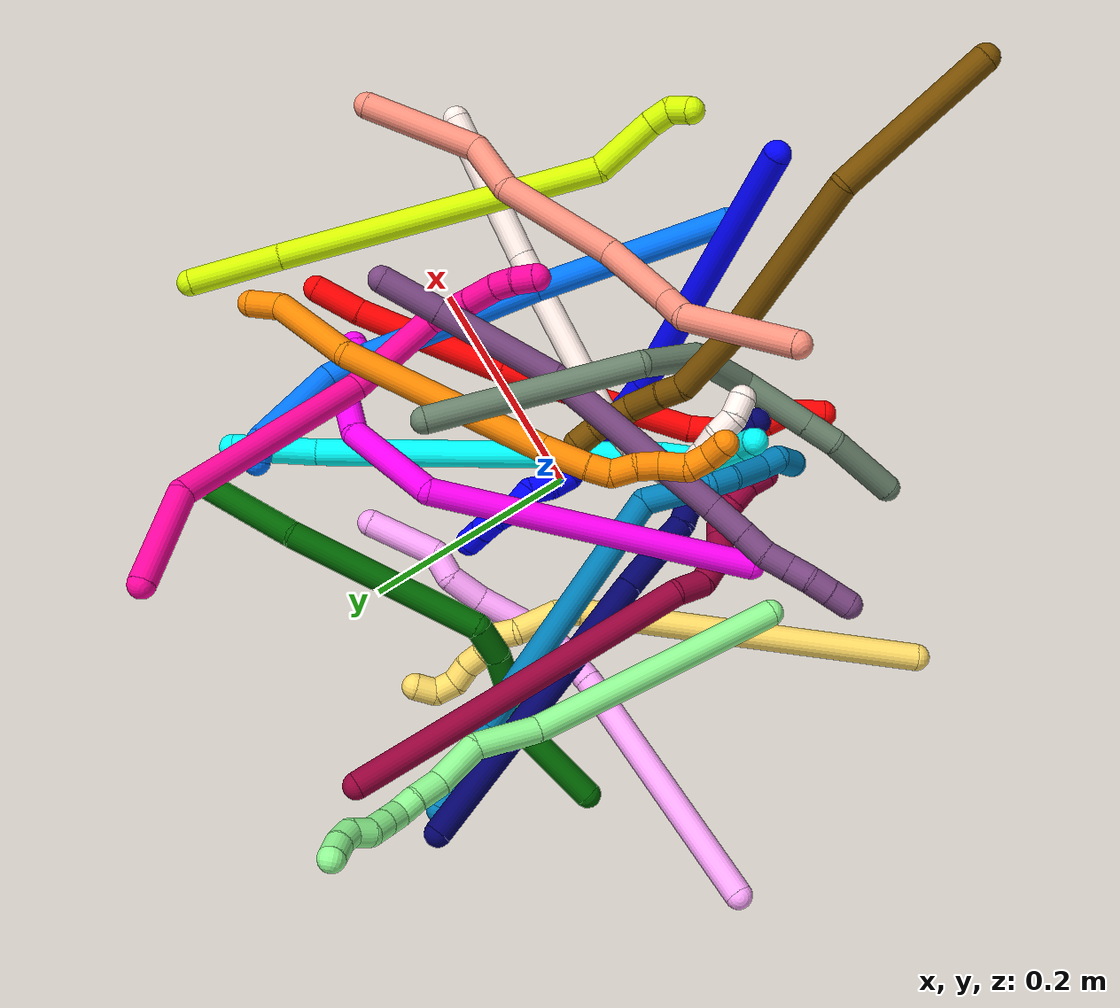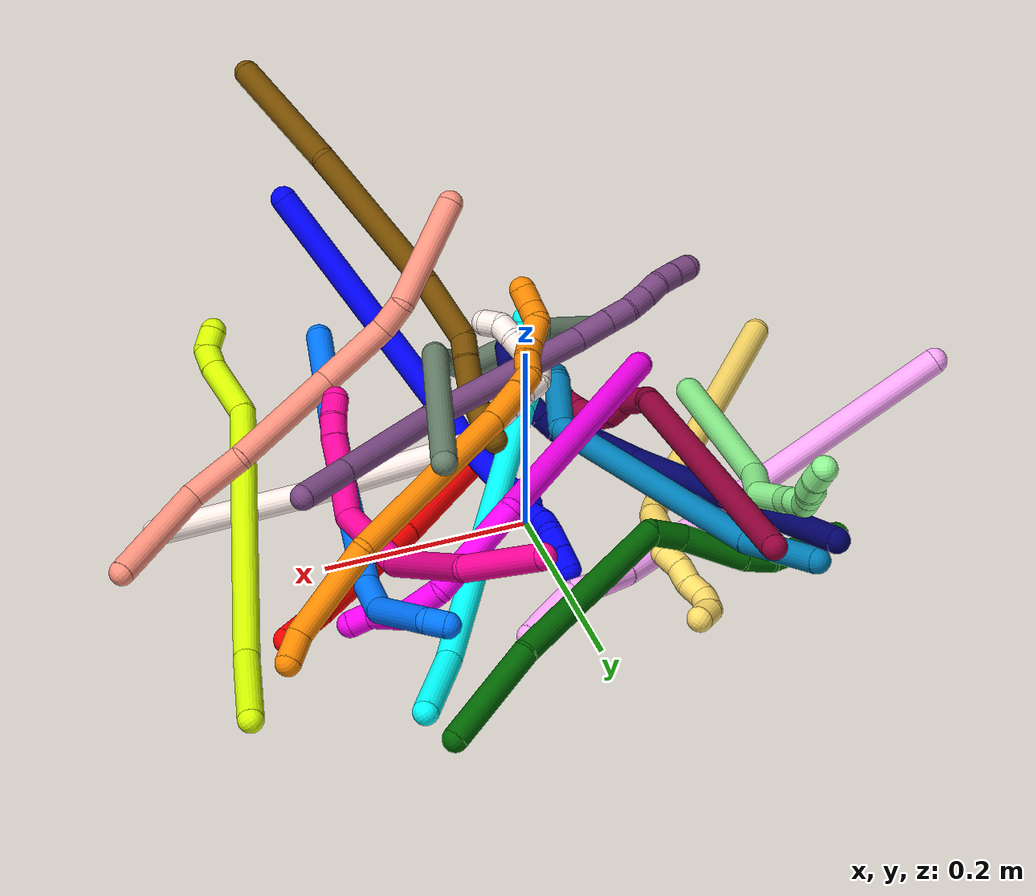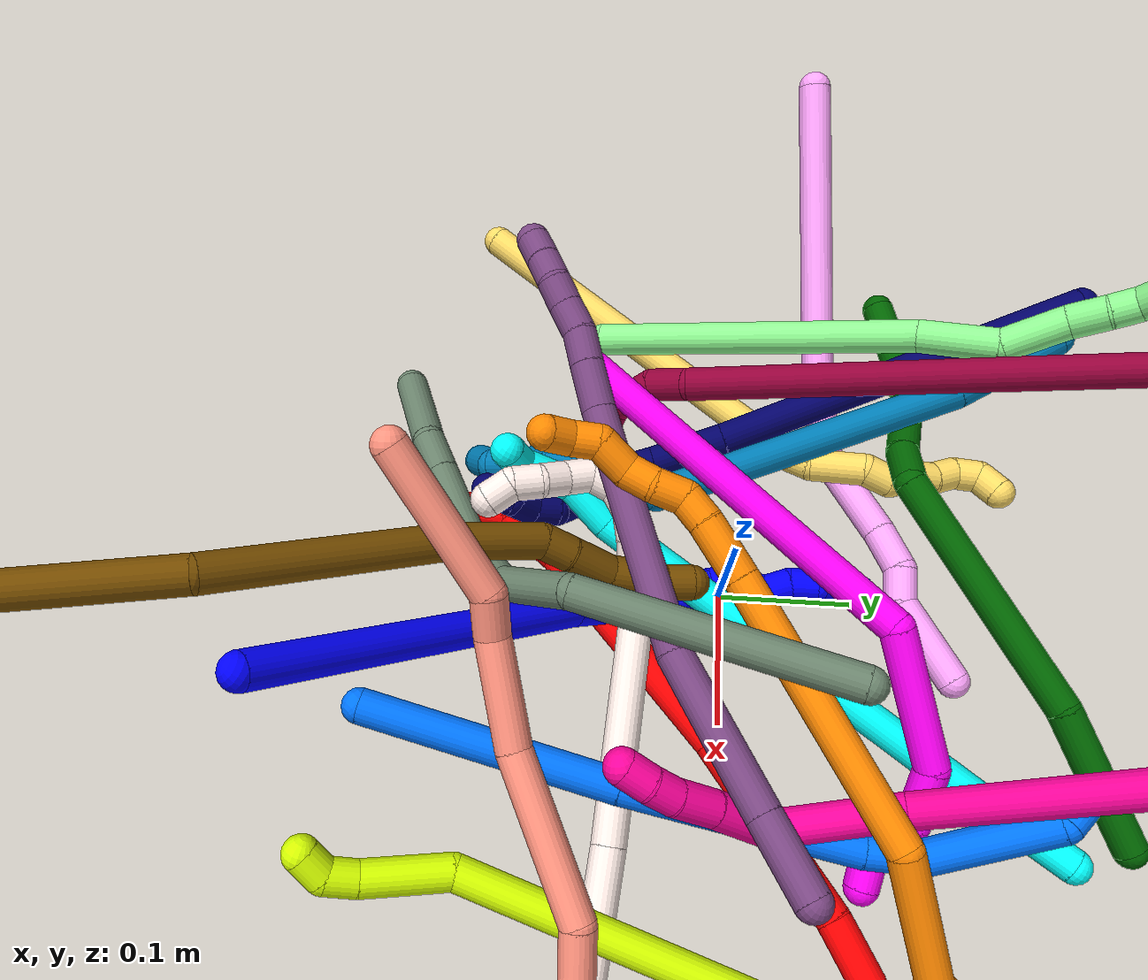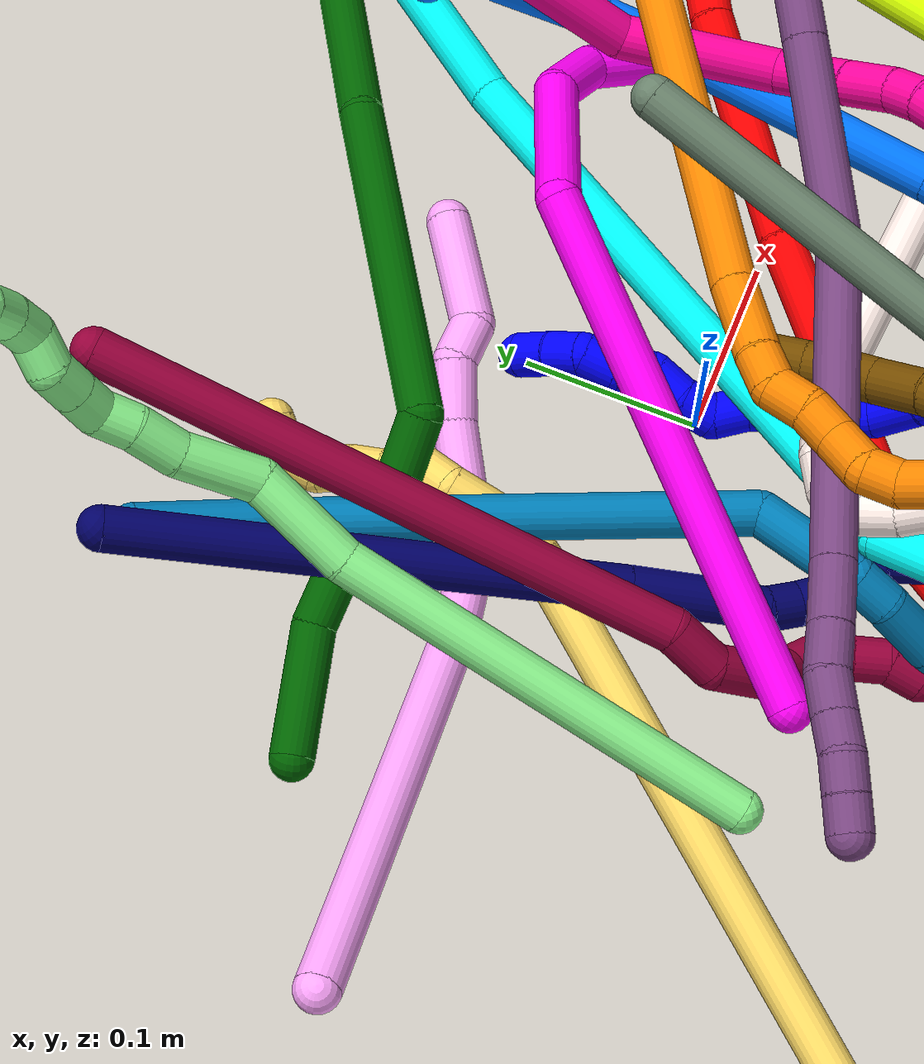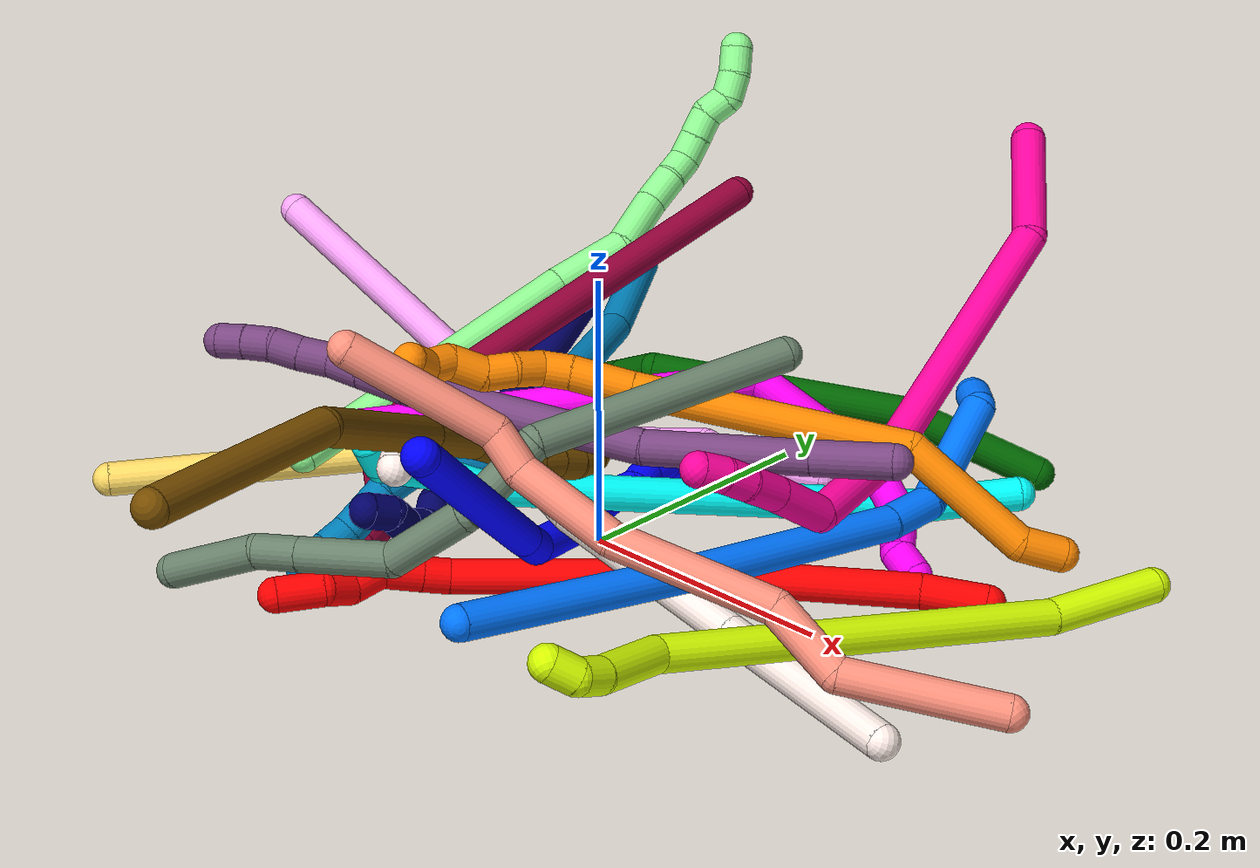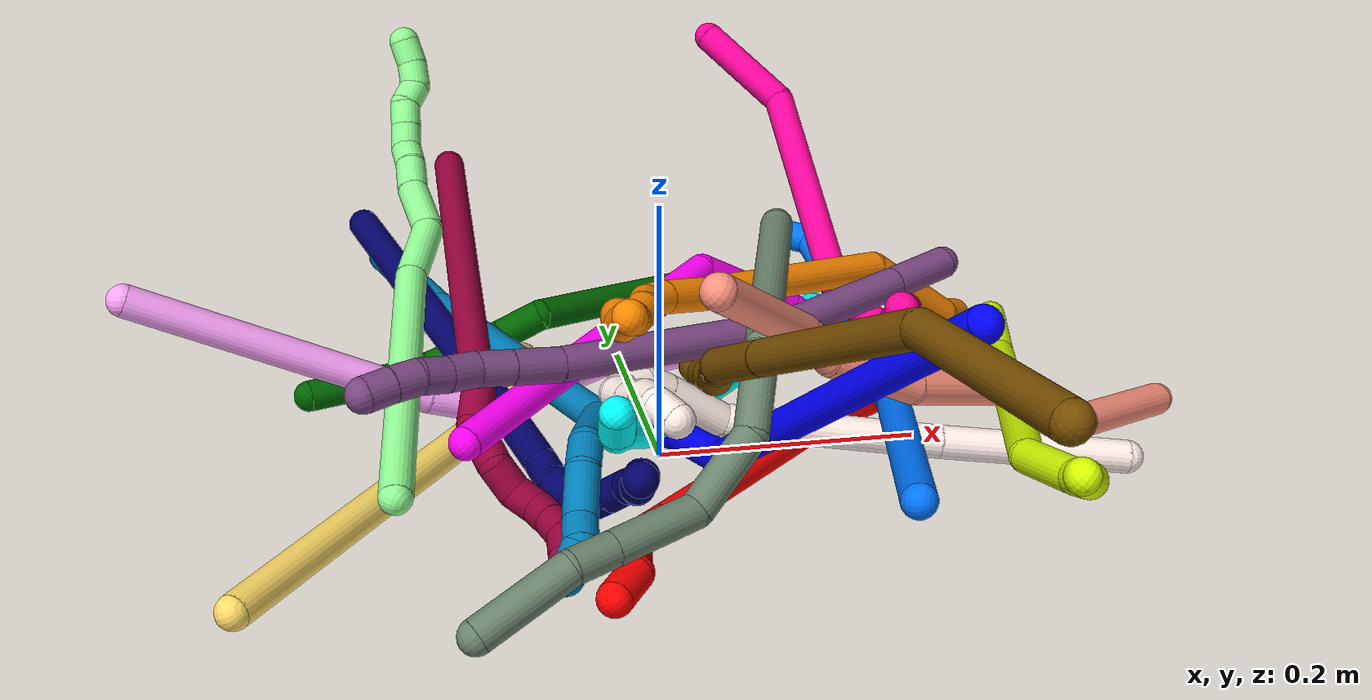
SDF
<sdf version="1.7">
 <world name="default">
  <plugin name="TubeGeneratorPlugin" filename="libtube_generator_plugin.so"/>
  <model name="photoneo_s_sensor">
   <static>1</static>
   <pose>0 0 2 1.57079 1.57079 3.14159</pose>
   <link name="link">
    <inertial><mass>0.1</mass></inertial>
    <sensor name="sensor" type="depth">
     <update_rate>30</update_rate>
     <camera>
      <horizontal_fov>1.22</horizontal_fov>
      <image><width>1920</width><height>1200</height><format>B8G8R8</format></image>
      <clip><near>0.1</near><far>4</far></clip>
      <depth_camera><output>points</output></depth_camera>
     </camera>
     <plugin name="camera_plugin" filename="libgazebo_ros_depth_camera.so">
      <baseline>0.2</baseline>
      <alwaysOn>1</alwaysOn>
      <updateRate>0.0</updateRate>
      <cameraName>camera_ir</cameraName>
      <imageTopicName>/camera/color/image_raw</imageTopicName>
      <cameraInfoTopicName>/camera/color/camera_info</cameraInfoTopicName>
      <depthImageTopicName>/camera/depth/image_raw</depthImageTopicName>
      <depthImageCameraInfoTopicName>/camera/depth/camera_info</depthImageCameraInfoTopicName>
      <pointCloudTopicName>/camera/depth/points</pointCloudTopicName>
      <frameName>fr_optical</frameName>
      <pointCloudCutoff>0.1</pointCloudCutoff>
      <pointCloudCutoffMax>2.0</pointCloudCutoffMax>
      <distortionK1>0</distortionK1>
      <distortionK2>0</distortionK2>
      <distortionK3>0</distortionK3>
      <distortionT1>0</distortionT1>
      <distortionT2>0</distortionT2>
      <CxPrime>0</CxPrime>
      <Cx>0</Cx>
      <Cy>0</Cy>
      <focalLength>0</focalLength>
      <hackBaseline>0</hackBaseline>
     </plugin>
    </sensor>
   </link>
  </model>
  <gravity>0 0 -9.8</gravity>
  <magnetic_field>6e-06 2.3e-05 -4.2e-05</magnetic_field>
  <atmosphere type="adiabatic"/>
  <physics name="default_physics" default="0" type="ode">
   <max_step_size>0.003</max_step_size>
   <real_time_factor>1</real_time_factor>
   <real_time_update_rate>1000</real_time_update_rate>
   <max_contacts>10000</max_contacts>
   <ode>
    <solver>
     <type>quick</type>
     <iters>100</iters>
     <sor>1.3</sor>
     <use_dynamic_moi_rescaling>0</use_dynamic_moi_rescaling>
    </solver>
    <constraints>
     <contact_max_correcting_vel>0</contact_max_correcting_vel>
     <contact_surface_layer>0.001</contact_surface_layer>
     <cfm>0</cfm>
     <erp>0.2</erp>
    </constraints>
   </ode>
  </physics>
  <scene><ambient>0.4 0.4 0.4 1</ambient><background>0.7 0.7 0.7 1</background><shadows>0</shadows></scene>
  <audio><device>default</device></audio>
  <spherical_coordinates>
   <surface_model>EARTH_WGS84</surface_model>
   <latitude_deg>0</latitude_deg>
   <longitude_deg>0</longitude_deg>
   <elevation>0</elevation>
   <heading_deg>0</heading_deg>
  </spherical_coordinates>
  <model name="bin">
   <static>1</static>
   <link name="bottom">
    <collision name="collision-bottom">
     <pose>0 0 -0.01 0 -0 0</pose>
     <geometry><box><size>0.8 0.6 0.02</size></box></geometry>
     <surface>
      <friction><ode><mu>100</mu><mu2>100</mu2></ode></friction>
      <contact><collide_bitmask>65535</collide_bitmask></contact>
     </surface>
    </collision>
   </link>
   <link name="west_wall">
    <collision name="collision-west_wall">
     <pose>-0.41 0 0.1 0 -0 0</pose>
     <geometry><box><size>0.02 0.6 0.2</size></box></geometry>
     <surface>
      <friction><ode><mu>100</mu><mu2>100</mu2></ode></friction>
      <contact><collide_bitmask>65535</collide_bitmask></contact>
     </surface>
    </collision>
   </link>
   <link name="east_wall">
    <collision name="collision-east_wall">
     <pose>0.41 0 0.1 0 -0 0</pose>
     <geometry><box><size>0.02 0.6 0.2</size></box></geometry>
     <surface>
      <friction><ode><mu>100</mu><mu2>100</mu2></ode></friction>
      <contact><collide_bitmask>65535</collide_bitmask></contact>
     </surface>
    </collision>
   </link>
   <link name="south_wall">
    <collision name="collision-south_wall">
     <pose>0 -0.31 0.1 0 -0 0</pose>
     <geometry><box><size>0.8 0.02 0.2</size></box></geometry>
     <surface>
      <friction><ode><mu>100</mu><mu2>100</mu2></ode></friction>
      <contact><collide_bitmask>65535</collide_bitmask></contact>
     </surface>
    </collision>
   </link>
   <link name="north_wall">
    <collision name="collision-north_wall">
     <pose>0 0.31 0.1 0 -0 0</pose>
     <geometry><box><size>0.8 0.02 0.2</size></box></geometry>
     <surface>
      <friction><ode><mu>100</mu><mu2>100</mu2></ode></friction>
      <contact><collide_bitmask>65535</collide_bitmask></contact>
     </surface>
    </collision>
   </link>
  </model>
  <model name="1">
   <static>0</static>
   <link name="1">
    <collision name="collision-cylinder-e_1_1_4">
     <pose>-0.068429 0.007891 -0.111738 -3.07109 -0.548385 2.89214</pose>
     <geometry><cylinder><radius>0.0125</radius><length>0.262528</length></cylinder></geometry>
     <surface>
      <friction><ode><mu>1.16</mu><mu2>1.16</mu2><slip1>0</slip1><slip2>0</slip2></ode></friction>
      <contact><ode><kp>1e+06</kp><kd>1</kd><max_vel>0</max_vel><min_depth>0.001</min_depth></ode></contact>
     </surface>
    </collision>
    <visual name="visual-cylinder-e_1_1_4">
     <pose>-0.068429 0.007891 -0.111738 -3.07109 -0.548385 2.89214</pose>
     <geometry><cylinder><radius>0.0125</radius><length>0.262528</length></cylinder></geometry>
     <material><ambient>0 0 1 1</ambient></material>
    </visual>
    <collision name="collision-cylinder-e_2_4_5">
     <pose>-0.143253 0.016708 -0.235962 -3.06757 -0.472267 2.83623</pose>
     <geometry><cylinder><radius>0.0125</radius><length>0.028117</length></cylinder></geometry>
     <surface>
      <friction><ode><mu>1.16</mu><mu2>1.16</mu2><slip1>0</slip1><slip2>0</slip2></ode></friction>
      <contact><ode><kp>1e+06</kp><kd>1</kd><max_vel>0</max_vel><min_depth>0.001</min_depth></ode></contact>
     </surface>
    </collision>
    <visual name="visual-cylinder-e_2_4_5">
     <pose>-0.143253 0.016708 -0.235962 -3.06757 -0.472267 2.83623</pose>
     <geometry><cylinder><radius>0.0125</radius><length>0.028117</length></cylinder></geometry>
     <material><ambient>0 0 1 1</ambient></material>
    </visual>
    <collision name="collision-cylinder-e_3_5_6">
     <pose>-0.16231 0.036611 -0.273787 -2.49877 -0.380443 1.04863</pose>
     <geometry><cylinder><radius>0.0125</radius><length>0.068192</length></cylinder></geometry>
     <surface>
      <friction><ode><mu>1.16</mu><mu2>1.16</mu2><slip1>0</slip1><slip2>0</slip2></ode></friction>
      <contact><ode><kp>1e+06</kp><kd>1</kd><max_vel>0</max_vel><min_depth>0.001</min_depth></ode></contact>
     </surface>
    </collision>
    <visual name="visual-cylinder-e_3_5_6">
     <pose>-0.16231 0.036611 -0.273787 -2.49877 -0.380443 1.04863</pose>
     <geometry><cylinder><radius>0.0125</radius><length>0.068192</length></cylinder></geometry>
     <material><ambient>0 0 1 1</ambient></material>
    </visual>
    <collision name="collision-cylinder-e_4_6_7">
     <pose>-0.181521 0.060637 -0.305167 -2.44547 -0.69398 1.56745</pose>
     <geometry><cylinder><radius>0.0125</radius><length>0.020483</length></cylinder></geometry>
     <surface>
      <friction><ode><mu>1.16</mu><mu2>1.16</mu2><slip1>0</slip1><slip2>0</slip2></ode></friction>
      <contact><ode><kp>1e+06</kp><kd>1</kd><max_vel>0</max_vel><min_depth>0.001</min_depth></ode></contact>
     </surface>
    </collision>
    <visual name="visual-cylinder-e_4_6_7">
     <pose>-0.181521 0.060637 -0.305167 -2.44547 -0.69398 1.56745</pose>
     <geometry><cylinder><radius>0.0125</radius><length>0.020483</length></cylinder></geometry>
     <material><ambient>0 0 1 1</ambient></material>
    </visual>
    <collision name="collision-cylinder-e_5_7_8">
     <pose>-0.188179 0.074741 -0.315918 -2.05045 -0.010497 0.017292</pose>
     <geometry><cylinder><radius>0.0125</radius><length>0.020416</length></cylinder></geometry>
     <surface>
      <friction><ode><mu>1.16</mu><mu2>1.16</mu2><slip1>0</slip1><slip2>0</slip2></ode></friction>
      <contact><ode><kp>1e+06</kp><kd>1</kd><max_vel>0</max_vel><min_depth>0.001</min_depth></ode></contact>
     </surface>
    </collision>
    <visual name="visual-cylinder-e_5_7_8">
     <pose>-0.188179 0.074741 -0.315918 -2.05045 -0.010497 0.017292</pose>
     <geometry><cylinder><radius>0.0125</radius><length>0.020416</length></cylinder></geometry>
     <material><ambient>0 0 1 1</ambient></material>
    </visual>
    <collision name="collision-cylinder-e_6_8_9">
     <pose>-0.185958 0.091647 -0.326541 -2.21625 0.232559 -0.46008</pose>
     <geometry><cylinder><radius>0.0125</radius><length>0.0202</length></cylinder></geometry>
     <surface>
      <friction><ode><mu>1.16</mu><mu2>1.16</mu2><slip1>0</slip1><slip2>0</slip2></ode></friction>
      <contact><ode><kp>1e+06</kp><kd>1</kd><max_vel>0</max_vel><min_depth>0.001</min_depth></ode></contact>
     </surface>
    </collision>
    <visual name="visual-cylinder-e_6_8_9">
     <pose>-0.185958 0.091647 -0.326541 -2.21625 0.232559 -0.46008</pose>
     <geometry><cylinder><radius>0.0125</radius><length>0.0202</length></cylinder></geometry>
     <material><ambient>0 0 1 1</ambient></material>
    </visual>
    <collision name="collision-cylinder-e_7_9_10">
     <pose>-0.18765 0.107025 -0.337726 -2.18189 -0.412294 0.764156</pose>
     <geometry><cylinder><radius>0.0125</radius><length>0.020062</length></cylinder></geometry>
     <surface>
      <friction><ode><mu>1.16</mu><mu2>1.16</mu2><slip1>0</slip1><slip2>0</slip2></ode></friction>
      <contact><ode><kp>1e+06</kp><kd>1</kd><max_vel>0</max_vel><min_depth>0.001</min_depth></ode></contact>
     </surface>
    </collision>
    <visual name="visual-cylinder-e_7_9_10">
     <pose>-0.18765 0.107025 -0.337726 -2.18189 -0.412294 0.764156</pose>
     <geometry><cylinder><radius>0.0125</radius><length>0.020062</length></cylinder></geometry>
     <material><ambient>0 0 1 1</ambient></material>
    </visual>
    <collision name="collision-cylinder-e_8_10_11">
     <pose>-0.192232 0.122405 -0.349167 -2.23659 -0.056268 0.115645</pose>
     <geometry><cylinder><radius>0.0125</radius><length>0.020002</length></cylinder></geometry>
     <surface>
      <friction><ode><mu>1.16</mu><mu2>1.16</mu2><slip1>0</slip1><slip2>0</slip2></ode></friction>
      <contact><ode><kp>1e+06</kp><kd>1</kd><max_vel>0</max_vel><min_depth>0.001</min_depth></ode></contact>
     </surface>
    </collision>
    <visual name="visual-cylinder-e_8_10_11">
     <pose>-0.192232 0.122405 -0.349167 -2.23659 -0.056268 0.115645</pose>
     <geometry><cylinder><radius>0.0125</radius><length>0.020002</length></cylinder></geometry>
     <material><ambient>0 0 1 1</ambient></material>
    </visual>
    <collision name="collision-cylinder-e_9_11_12">
     <pose>-0.19549 0.133111 -0.364532 -2.84078 -0.272904 1.47224</pose>
     <geometry><cylinder><radius>0.0125</radius><length>0.02</length></cylinder></geometry>
     <surface>
      <friction><ode><mu>1.16</mu><mu2>1.16</mu2><slip1>0</slip1><slip2>0</slip2></ode></friction>
      <contact><ode><kp>1e+06</kp><kd>1</kd><max_vel>0</max_vel><min_depth>0.001</min_depth></ode></contact>
     </surface>
    </collision>
    <visual name="visual-cylinder-e_9_11_12">
     <pose>-0.19549 0.133111 -0.364532 -2.84078 -0.272904 1.47224</pose>
     <geometry><cylinder><radius>0.0125</radius><length>0.02</length></cylinder></geometry>
     <material><ambient>0 0 1 1</ambient></material>
    </visual>
    <collision name="collision-cylinder-e_10_12_2">
     <pose>-0.201109 0.137843 -0.383107 -2.9439 -0.296672 1.96979</pose>
     <geometry><cylinder><radius>0.0125</radius><length>0.02</length></cylinder></geometry>
     <surface>
      <friction><ode><mu>1.16</mu><mu2>1.16</mu2><slip1>0</slip1><slip2>0</slip2></ode></friction>
      <contact><ode><kp>1e+06</kp><kd>1</kd><max_vel>0</max_vel><min_depth>0.001</min_depth></ode></contact>
     </surface>
    </collision>
    <visual name="visual-cylinder-e_10_12_2">
     <pose>-0.201109 0.137843 -0.383107 -2.9439 -0.296672 1.96979</pose>
     <geometry><cylinder><radius>0.0125</radius><length>0.02</length></cylinder></geometry>
     <material><ambient>0 0 1 1</ambient></material>
    </visual>
    <collision name="collision-sphere-2">
     <pose>-0.204032 0.139721 -0.392484 0 -0 0</pose>
     <geometry><sphere><radius>0.0125</radius></sphere></geometry>
     <surface>
      <friction><ode><mu>1.16</mu><mu2>1.16</mu2><slip1>0</slip1><slip2>0</slip2></ode></friction>
      <contact><ode><kp>1e+06</kp><kd>1</kd><max_vel>0</max_vel><min_depth>0.001</min_depth></ode></contact>
     </surface>
    </collision>
    <visual name="visual-sphere-2">
     <pose>-0.204032 0.139721 -0.392484 0 -0 0</pose>
     <geometry><sphere><radius>0.0125</radius></sphere></geometry>
     <material><ambient>0 0 1 1</ambient></material>
    </visual>
    <collision name="collision-sphere-12">
     <pose>-0.198185 0.135964 -0.37373 0 -0 0</pose>
     <geometry><sphere><radius>0.0125</radius></sphere></geometry>
     <surface>
      <friction><ode><mu>1.16</mu><mu2>1.16</mu2><slip1>0</slip1><slip2>0</slip2></ode></friction>
      <contact><ode><kp>1e+06</kp><kd>1</kd><max_vel>0</max_vel><min_depth>0.001</min_depth></ode></contact>
     </surface>
    </collision>
    <visual name="visual-sphere-12">
     <pose>-0.198185 0.135964 -0.37373 0 -0 0</pose>
     <geometry><sphere><radius>0.0125</radius></sphere></geometry>
     <material><ambient>0 0 1 1</ambient></material>
    </visual>
    <collision name="collision-sphere-11">
     <pose>-0.192794 0.130258 -0.355335 0 -0 0</pose>
     <geometry><sphere><radius>0.0125</radius></sphere></geometry>
     <surface>
      <friction><ode><mu>1.16</mu><mu2>1.16</mu2><slip1>0</slip1><slip2>0</slip2></ode></friction>
      <contact><ode><kp>1e+06</kp><kd>1</kd><max_vel>0</max_vel><min_depth>0.001</min_depth></ode></contact>
     </surface>
    </collision>
    <visual name="visual-sphere-11">
     <pose>-0.192794 0.130258 -0.355335 0 -0 0</pose>
     <geometry><sphere><radius>0.0125</radius></sphere></geometry>
     <material><ambient>0 0 1 1</ambient></material>
    </visual>
    <collision name="collision-sphere-10">
     <pose>-0.19167 0.114552 -0.342999 0 -0 0</pose>
     <geometry><sphere><radius>0.0125</radius></sphere></geometry>
     <surface>
      <friction><ode><mu>1.16</mu><mu2>1.16</mu2><slip1>0</slip1><slip2>0</slip2></ode></friction>
      <contact><ode><kp>1e+06</kp><kd>1</kd><max_vel>0</max_vel><min_depth>0.001</min_depth></ode></contact>
     </surface>
    </collision>
    <visual name="visual-sphere-10">
     <pose>-0.19167 0.114552 -0.342999 0 -0 0</pose>
     <geometry><sphere><radius>0.0125</radius></sphere></geometry>
     <material><ambient>0 0 1 1</ambient></material>
    </visual>
    <collision name="collision-sphere-9">
     <pose>-0.183631 0.099498 -0.332453 0 -0 0</pose>
     <geometry><sphere><radius>0.0125</radius></sphere></geometry>
     <surface>
      <friction><ode><mu>1.16</mu><mu2>1.16</mu2><slip1>0</slip1><slip2>0</slip2></ode></friction>
      <contact><ode><kp>1e+06</kp><kd>1</kd><max_vel>0</max_vel><min_depth>0.001</min_depth></ode></contact>
     </surface>
    </collision>
    <visual name="visual-sphere-9">
     <pose>-0.183631 0.099498 -0.332453 0 -0 0</pose>
     <geometry><sphere><radius>0.0125</radius></sphere></geometry>
     <material><ambient>0 0 1 1</ambient></material>
    </visual>
    <collision name="collision-sphere-4">
     <pose>-0.136858 0.015782 -0.223476 0 -0 0</pose>
     <geometry><sphere><radius>0.0125</radius></sphere></geometry>
     <surface>
      <friction><ode><mu>1.16</mu><mu2>1.16</mu2><slip1>0</slip1><slip2>0</slip2></ode></friction>
      <contact><ode><kp>1e+06</kp><kd>1</kd><max_vel>0</max_vel><min_depth>0.001</min_depth></ode></contact>
     </surface>
    </collision>
    <visual name="visual-sphere-4">
     <pose>-0.136858 0.015782 -0.223476 0 -0 0</pose>
     <geometry><sphere><radius>0.0125</radius></sphere></geometry>
     <material><ambient>0 0 1 1</ambient></material>
    </visual>
    <collision name="collision-sphere-1">
     <geometry><sphere><radius>0.0125</radius></sphere></geometry>
     <surface>
      <friction><ode><mu>1.16</mu><mu2>1.16</mu2><slip1>0</slip1><slip2>0</slip2></ode></friction>
      <contact><ode><kp>1e+06</kp><kd>1</kd><max_vel>0</max_vel><min_depth>0.001</min_depth></ode></contact>
     </surface>
    </collision>
    <visual name="visual-sphere-1">
     <geometry><sphere><radius>0.0125</radius></sphere></geometry>
     <material><ambient>0 0 1 1</ambient></material>
    </visual>
    <collision name="collision-sphere-8">
     <pose>-0.188286 0.083797 -0.320629 0 -0 0</pose>
     <geometry><sphere><radius>0.0125</radius></sphere></geometry>
     <surface>
      <friction><ode><mu>1.16</mu><mu2>1.16</mu2><slip1>0</slip1><slip2>0</slip2></ode></friction>
      <contact><ode><kp>1e+06</kp><kd>1</kd><max_vel>0</max_vel><min_depth>0.001</min_depth></ode></contact>
     </surface>
    </collision>
    <visual name="visual-sphere-8">
     <pose>-0.188286 0.083797 -0.320629 0 -0 0</pose>
     <geometry><sphere><radius>0.0125</radius></sphere></geometry>
     <material><ambient>0 0 1 1</ambient></material>
    </visual>
    <collision name="collision-sphere-5">
     <pose>-0.149649 0.017633 -0.248447 0 -0 0</pose>
     <geometry><sphere><radius>0.0125</radius></sphere></geometry>
     <surface>
      <friction><ode><mu>1.16</mu><mu2>1.16</mu2><slip1>0</slip1><slip2>0</slip2></ode></friction>
      <contact><ode><kp>1e+06</kp><kd>1</kd><max_vel>0</max_vel><min_depth>0.001</min_depth></ode></contact>
     </surface>
    </collision>
    <visual name="visual-sphere-5">
     <pose>-0.149649 0.017633 -0.248447 0 -0 0</pose>
     <geometry><sphere><radius>0.0125</radius></sphere></geometry>
     <material><ambient>0 0 1 1</ambient></material>
    </visual>
    <collision name="collision-sphere-6">
     <pose>-0.174971 0.055589 -0.299126 0 -0 0</pose>
     <geometry><sphere><radius>0.0125</radius></sphere></geometry>
     <surface>
      <friction><ode><mu>1.16</mu><mu2>1.16</mu2><slip1>0</slip1><slip2>0</slip2></ode></friction>
      <contact><ode><kp>1e+06</kp><kd>1</kd><max_vel>0</max_vel><min_depth>0.001</min_depth></ode></contact>
     </surface>
    </collision>
    <visual name="visual-sphere-6">
     <pose>-0.174971 0.055589 -0.299126 0 -0 0</pose>
     <geometry><sphere><radius>0.0125</radius></sphere></geometry>
     <material><ambient>0 0 1 1</ambient></material>
    </visual>
    <collision name="collision-sphere-7">
     <pose>-0.188072 0.065686 -0.311208 0 -0 0</pose>
     <geometry><sphere><radius>0.0125</radius></sphere></geometry>
     <surface>
      <friction><ode><mu>1.16</mu><mu2>1.16</mu2><slip1>0</slip1><slip2>0</slip2></ode></friction>
      <contact><ode><kp>1e+06</kp><kd>1</kd><max_vel>0</max_vel><min_depth>0.001</min_depth></ode></contact>
     </surface>
    </collision>
    <visual name="visual-sphere-7">
     <pose>-0.188072 0.065686 -0.311208 0 -0 0</pose>
     <geometry><sphere><radius>0.0125</radius></sphere></geometry>
     <material><ambient>0 0 1 1</ambient></material>
    </visual>
    <inertial>
     <pose>-0.119837 0.039343 -0.205296 0 -0 0</pose>
     <mass>0.5</mass>
     <inertia>
      <ixx>-0.000907</ixx>
      <ixy>0</ixy>
      <ixz>0</ixz>
      <iyy>0.001836</iyy>
      <iyz>0</iyz>
      <izz>0.000661</izz>
     </inertia>
    </inertial>
   </link>
   <pose>0.138408 -0.294429 0.213442 0.801152 -0.105021 -0.109209</pose>
  </model>
  <model name="2">
   <static>0</static>
   <link name="2">
    <collision name="collision-cylinder-e_1_1_4">
     <pose>-0.019655 -0.006708 0.009765 0.601879 -1.02836 -0.347101</pose>
     <geometry><cylinder><radius>0.0125</radius><length>0.0459</length></cylinder></geometry>
     <surface>
      <friction><ode><mu>1.16</mu><mu2>1.16</mu2><slip1>0</slip1><slip2>0</slip2></ode></friction>
      <contact><ode><kp>1e+06</kp><kd>1</kd><max_vel>0</max_vel><min_depth>0.001</min_depth></ode></contact>
     </surface>
    </collision>
    <visual name="visual-cylinder-e_1_1_4">
     <pose>-0.019655 -0.006708 0.009765 0.601879 -1.02836 -0.347101</pose>
     <geometry><cylinder><radius>0.0125</radius><length>0.0459</length></cylinder></geometry>
     <material><ambient>1 0 0 1</ambient></material>
    </visual>
    <collision name="collision-cylinder-e_2_4_5">
     <pose>-0.10122 -0.039114 0.042359 0.844472 -1.06395 -0.517007</pose>
     <geometry><cylinder><radius>0.0125</radius><length>0.141624</length></cylinder></geometry>
     <surface>
      <friction><ode><mu>1.16</mu><mu2>1.16</mu2><slip1>0</slip1><slip2>0</slip2></ode></friction>
      <contact><ode><kp>1e+06</kp><kd>1</kd><max_vel>0</max_vel><min_depth>0.001</min_depth></ode></contact>
     </surface>
    </collision>
    <visual name="visual-cylinder-e_2_4_5">
     <pose>-0.10122 -0.039114 0.042359 0.844472 -1.06395 -0.517007</pose>
     <geometry><cylinder><radius>0.0125</radius><length>0.141624</length></cylinder></geometry>
     <material><ambient>1 0 0 1</ambient></material>
    </visual>
    <collision name="collision-cylinder-e_3_5_6">
     <pose>-0.243137 -0.102795 0.08781 1.03361 -1.06599 -0.647012</pose>
     <geometry><cylinder><radius>0.0125</radius><length>0.182817</length></cylinder></geometry>
     <surface>
      <friction><ode><mu>1.16</mu><mu2>1.16</mu2><slip1>0</slip1><slip2>0</slip2></ode></friction>
      <contact><ode><kp>1e+06</kp><kd>1</kd><max_vel>0</max_vel><min_depth>0.001</min_depth></ode></contact>
     </surface>
    </collision>
    <visual name="visual-cylinder-e_3_5_6">
     <pose>-0.243137 -0.102795 0.08781 1.03361 -1.06599 -0.647012</pose>
     <geometry><cylinder><radius>0.0125</radius><length>0.182817</length></cylinder></geometry>
     <material><ambient>1 0 0 1</ambient></material>
    </visual>
    <collision name="collision-cylinder-e_4_6_7">
     <pose>-0.330281 -0.147382 0.113091 1.18816 -0.786643 -0.546548</pose>
     <geometry><cylinder><radius>0.0125</radius><length>0.020164</length></cylinder></geometry>
     <surface>
      <friction><ode><mu>1.16</mu><mu2>1.16</mu2><slip1>0</slip1><slip2>0</slip2></ode></friction>
      <contact><ode><kp>1e+06</kp><kd>1</kd><max_vel>0</max_vel><min_depth>0.001</min_depth></ode></contact>
     </surface>
    </collision>
    <visual name="visual-cylinder-e_4_6_7">
     <pose>-0.330281 -0.147382 0.113091 1.18816 -0.786643 -0.546548</pose>
     <geometry><cylinder><radius>0.0125</radius><length>0.020164</length></cylinder></geometry>
     <material><ambient>1 0 0 1</ambient></material>
    </visual>
    <collision name="collision-cylinder-e_5_7_8">
     <pose>-0.347173 -0.163748 0.119657 1.19001 -0.747891 -0.5192</pose>
     <geometry><cylinder><radius>0.0125</radius><length>0.028684</length></cylinder></geometry>
     <surface>
      <friction><ode><mu>1.16</mu><mu2>1.16</mu2><slip1>0</slip1><slip2>0</slip2></ode></friction>
      <contact><ode><kp>1e+06</kp><kd>1</kd><max_vel>0</max_vel><min_depth>0.001</min_depth></ode></contact>
     </surface>
    </collision>
    <visual name="visual-cylinder-e_5_7_8">
     <pose>-0.347173 -0.163748 0.119657 1.19001 -0.747891 -0.5192</pose>
     <geometry><cylinder><radius>0.0125</radius><length>0.028684</length></cylinder></geometry>
     <material><ambient>1 0 0 1</ambient></material>
    </visual>
    <collision name="collision-cylinder-e_6_8_9">
     <pose>-0.365011 -0.182327 0.119679 1.98587 -0.698085 -1.01807</pose>
     <geometry><cylinder><radius>0.0125</radius><length>0.025156</length></cylinder></geometry>
     <surface>
      <friction><ode><mu>1.16</mu><mu2>1.16</mu2><slip1>0</slip1><slip2>0</slip2></ode></friction>
      <contact><ode><kp>1e+06</kp><kd>1</kd><max_vel>0</max_vel><min_depth>0.001</min_depth></ode></contact>
     </surface>
    </collision>
    <visual name="visual-cylinder-e_6_8_9">
     <pose>-0.365011 -0.182327 0.119679 1.98587 -0.698085 -1.01807</pose>
     <geometry><cylinder><radius>0.0125</radius><length>0.025156</length></cylinder></geometry>
     <material><ambient>1 0 0 1</ambient></material>
    </visual>
    <collision name="collision-cylinder-e_7_9_10">
     <pose>-0.376886 -0.201711 0.115977 1.55338 -0.344378 -0.338546</pose>
     <geometry><cylinder><radius>0.0125</radius><length>0.022454</length></cylinder></geometry>
     <surface>
      <friction><ode><mu>1.16</mu><mu2>1.16</mu2><slip1>0</slip1><slip2>0</slip2></ode></friction>
      <contact><ode><kp>1e+06</kp><kd>1</kd><max_vel>0</max_vel><min_depth>0.001</min_depth></ode></contact>
     </surface>
    </collision>
    <visual name="visual-cylinder-e_7_9_10">
     <pose>-0.376886 -0.201711 0.115977 1.55338 -0.344378 -0.338546</pose>
     <geometry><cylinder><radius>0.0125</radius><length>0.022454</length></cylinder></geometry>
     <material><ambient>1 0 0 1</ambient></material>
    </visual>
    <collision name="collision-cylinder-e_8_10_2">
     <pose>-0.393822 -0.222337 0.117424 1.44597 -0.913763 -0.818507</pose>
     <geometry><cylinder><radius>0.0125</radius><length>0.033202</length></cylinder></geometry>
     <surface>
      <friction><ode><mu>1.16</mu><mu2>1.16</mu2><slip1>0</slip1><slip2>0</slip2></ode></friction>
      <contact><ode><kp>1e+06</kp><kd>1</kd><max_vel>0</max_vel><min_depth>0.001</min_depth></ode></contact>
     </surface>
    </collision>
    <visual name="visual-cylinder-e_8_10_2">
     <pose>-0.393822 -0.222337 0.117424 1.44597 -0.913763 -0.818507</pose>
     <geometry><cylinder><radius>0.0125</radius><length>0.033202</length></cylinder></geometry>
     <material><ambient>1 0 0 1</ambient></material>
    </visual>
    <collision name="collision-sphere-2">
     <pose>-0.406967 -0.232398 0.118686 0 -0 0</pose>
     <geometry><sphere><radius>0.0125</radius></sphere></geometry>
     <surface>
      <friction><ode><mu>1.16</mu><mu2>1.16</mu2><slip1>0</slip1><slip2>0</slip2></ode></friction>
      <contact><ode><kp>1e+06</kp><kd>1</kd><max_vel>0</max_vel><min_depth>0.001</min_depth></ode></contact>
     </surface>
    </collision>
    <visual name="visual-sphere-2">
     <pose>-0.406967 -0.232398 0.118686 0 -0 0</pose>
     <geometry><sphere><radius>0.0125</radius></sphere></geometry>
     <material><ambient>1 0 0 1</ambient></material>
    </visual>
    <collision name="collision-sphere-10">
     <pose>-0.380677 -0.212277 0.116161 0 -0 0</pose>
     <geometry><sphere><radius>0.0125</radius></sphere></geometry>
     <surface>
      <friction><ode><mu>1.16</mu><mu2>1.16</mu2><slip1>0</slip1><slip2>0</slip2></ode></friction>
      <contact><ode><kp>1e+06</kp><kd>1</kd><max_vel>0</max_vel><min_depth>0.001</min_depth></ode></contact>
     </surface>
    </collision>
    <visual name="visual-sphere-10">
     <pose>-0.380677 -0.212277 0.116161 0 -0 0</pose>
     <geometry><sphere><radius>0.0125</radius></sphere></geometry>
     <material><ambient>1 0 0 1</ambient></material>
    </visual>
    <collision name="collision-sphere-9">
     <pose>-0.373096 -0.191144 0.115793 0 -0 0</pose>
     <geometry><sphere><radius>0.0125</radius></sphere></geometry>
     <surface>
      <friction><ode><mu>1.16</mu><mu2>1.16</mu2><slip1>0</slip1><slip2>0</slip2></ode></friction>
      <contact><ode><kp>1e+06</kp><kd>1</kd><max_vel>0</max_vel><min_depth>0.001</min_depth></ode></contact>
     </surface>
    </collision>
    <visual name="visual-sphere-9">
     <pose>-0.373096 -0.191144 0.115793 0 -0 0</pose>
     <geometry><sphere><radius>0.0125</radius></sphere></geometry>
     <material><ambient>1 0 0 1</ambient></material>
    </visual>
    <collision name="collision-sphere-4">
     <pose>-0.039311 -0.013416 0.019531 0 -0 0</pose>
     <geometry><sphere><radius>0.0125</radius></sphere></geometry>
     <surface>
      <friction><ode><mu>1.16</mu><mu2>1.16</mu2><slip1>0</slip1><slip2>0</slip2></ode></friction>
      <contact><ode><kp>1e+06</kp><kd>1</kd><max_vel>0</max_vel><min_depth>0.001</min_depth></ode></contact>
     </surface>
    </collision>
    <visual name="visual-sphere-4">
     <pose>-0.039311 -0.013416 0.019531 0 -0 0</pose>
     <geometry><sphere><radius>0.0125</radius></sphere></geometry>
     <material><ambient>1 0 0 1</ambient></material>
    </visual>
    <collision name="collision-sphere-1">
     <geometry><sphere><radius>0.0125</radius></sphere></geometry>
     <surface>
      <friction><ode><mu>1.16</mu><mu2>1.16</mu2><slip1>0</slip1><slip2>0</slip2></ode></friction>
      <contact><ode><kp>1e+06</kp><kd>1</kd><max_vel>0</max_vel><min_depth>0.001</min_depth></ode></contact>
     </surface>
    </collision>
    <visual name="visual-sphere-1">
     <geometry><sphere><radius>0.0125</radius></sphere></geometry>
     <material><ambient>1 0 0 1</ambient></material>
    </visual>
    <collision name="collision-sphere-8">
     <pose>-0.356927 -0.173509 0.123564 0 -0 0</pose>
     <geometry><sphere><radius>0.0125</radius></sphere></geometry>
     <surface>
      <friction><ode><mu>1.16</mu><mu2>1.16</mu2><slip1>0</slip1><slip2>0</slip2></ode></friction>
      <contact><ode><kp>1e+06</kp><kd>1</kd><max_vel>0</max_vel><min_depth>0.001</min_depth></ode></contact>
     </surface>
    </collision>
    <visual name="visual-sphere-8">
     <pose>-0.356927 -0.173509 0.123564 0 -0 0</pose>
     <geometry><sphere><radius>0.0125</radius></sphere></geometry>
     <material><ambient>1 0 0 1</ambient></material>
    </visual>
    <collision name="collision-sphere-5">
     <pose>-0.16313 -0.064813 0.065188 0 -0 0</pose>
     <geometry><sphere><radius>0.0125</radius></sphere></geometry>
     <surface>
      <friction><ode><mu>1.16</mu><mu2>1.16</mu2><slip1>0</slip1><slip2>0</slip2></ode></friction>
      <contact><ode><kp>1e+06</kp><kd>1</kd><max_vel>0</max_vel><min_depth>0.001</min_depth></ode></contact>
     </surface>
    </collision>
    <visual name="visual-sphere-5">
     <pose>-0.16313 -0.064813 0.065188 0 -0 0</pose>
     <geometry><sphere><radius>0.0125</radius></sphere></geometry>
     <material><ambient>1 0 0 1</ambient></material>
    </visual>
    <collision name="collision-sphere-6">
     <pose>-0.323143 -0.140776 0.110432 0 -0 0</pose>
     <geometry><sphere><radius>0.0125</radius></sphere></geometry>
     <surface>
      <friction><ode><mu>1.16</mu><mu2>1.16</mu2><slip1>0</slip1><slip2>0</slip2></ode></friction>
      <contact><ode><kp>1e+06</kp><kd>1</kd><max_vel>0</max_vel><min_depth>0.001</min_depth></ode></contact>
     </surface>
    </collision>
    <visual name="visual-sphere-6">
     <pose>-0.323143 -0.140776 0.110432 0 -0 0</pose>
     <geometry><sphere><radius>0.0125</radius></sphere></geometry>
     <material><ambient>1 0 0 1</ambient></material>
    </visual>
    <collision name="collision-sphere-7">
     <pose>-0.337419 -0.153987 0.115749 0 -0 0</pose>
     <geometry><sphere><radius>0.0125</radius></sphere></geometry>
     <surface>
      <friction><ode><mu>1.16</mu><mu2>1.16</mu2><slip1>0</slip1><slip2>0</slip2></ode></friction>
      <contact><ode><kp>1e+06</kp><kd>1</kd><max_vel>0</max_vel><min_depth>0.001</min_depth></ode></contact>
     </surface>
    </collision>
    <visual name="visual-sphere-7">
     <pose>-0.337419 -0.153987 0.115749 0 -0 0</pose>
     <geometry><sphere><radius>0.0125</radius></sphere></geometry>
     <material><ambient>1 0 0 1</ambient></material>
    </visual>
    <inertial>
     <pose>-0.214051 -0.097613 0.075453 0 -0 0</pose>
     <mass>0.5</mass>
     <inertia>
      <ixx>6.6e-05</ixx>
      <ixy>0</ixy>
      <ixz>0</ixz>
      <iyy>0.000445</iyy>
      <iyz>0</iyz>
      <izz>0.001004</izz>
     </inertia>
    </inertial>
   </link>
   <pose>0.270781 0.100546 0.012218 -0.523349 -0.476601 0.479194</pose>
  </model>
  <model name="3">
   <static>0</static>
   <link name="3">
    <collision name="collision-cylinder-e_1_1_4">
     <pose>-0.022077 -0.032262 -0.004088 1.69684 -0.596408 -0.67117</pose>
     <geometry><cylinder><radius>0.0125</radius><length>0.07861</length></cylinder></geometry>
     <surface>
      <friction><ode><mu>1.16</mu><mu2>1.16</mu2><slip1>0</slip1><slip2>0</slip2></ode></friction>
      <contact><ode><kp>1e+06</kp><kd>1</kd><max_vel>0</max_vel><min_depth>0.001</min_depth></ode></contact>
     </surface>
    </collision>
    <visual name="visual-cylinder-e_1_1_4">
     <pose>-0.022077 -0.032262 -0.004088 1.69684 -0.596408 -0.67117</pose>
     <geometry><cylinder><radius>0.0125</radius><length>0.07861</length></cylinder></geometry>
     <material><ambient>0.003922 1 0.996078 1</ambient></material>
    </visual>
    <collision name="collision-cylinder-e_2_4_5">
     <pose>-0.111099 -0.210928 -0.00857 1.57349 -0.428872 -0.429992</pose>
     <geometry><cylinder><radius>0.0125</radius><length>0.321971</length></cylinder></geometry>
     <surface>
      <friction><ode><mu>1.16</mu><mu2>1.16</mu2><slip1>0</slip1><slip2>0</slip2></ode></friction>
      <contact><ode><kp>1e+06</kp><kd>1</kd><max_vel>0</max_vel><min_depth>0.001</min_depth></ode></contact>
     </surface>
    </collision>
    <visual name="visual-cylinder-e_2_4_5">
     <pose>-0.111099 -0.210928 -0.00857 1.57349 -0.428872 -0.429992</pose>
     <geometry><cylinder><radius>0.0125</radius><length>0.321971</length></cylinder></geometry>
     <material><ambient>0.003922 1 0.996078 1</ambient></material>
    </visual>
    <collision name="collision-cylinder-e_3_5_6">
     <pose>-0.184427 -0.374574 -0.004468 1.31573 -0.344021 -0.266879</pose>
     <geometry><cylinder><radius>0.0125</radius><length>0.037852</length></cylinder></geometry>
     <surface>
      <friction><ode><mu>1.16</mu><mu2>1.16</mu2><slip1>0</slip1><slip2>0</slip2></ode></friction>
      <contact><ode><kp>1e+06</kp><kd>1</kd><max_vel>0</max_vel><min_depth>0.001</min_depth></ode></contact>
     </surface>
    </collision>
    <visual name="visual-cylinder-e_3_5_6">
     <pose>-0.184427 -0.374574 -0.004468 1.31573 -0.344021 -0.266879</pose>
     <geometry><cylinder><radius>0.0125</radius><length>0.037852</length></cylinder></geometry>
     <material><ambient>0.003922 1 0.996078 1</ambient></material>
    </visual>
    <collision name="collision-cylinder-e_4_6_7">
     <pose>-0.191055 -0.411975 -0.001724 1.65745 -0.012093 -0.013189</pose>
     <geometry><cylinder><radius>0.0125</radius><length>0.040475</length></cylinder></geometry>
     <surface>
      <friction><ode><mu>1.16</mu><mu2>1.16</mu2><slip1>0</slip1><slip2>0</slip2></ode></friction>
      <contact><ode><kp>1e+06</kp><kd>1</kd><max_vel>0</max_vel><min_depth>0.001</min_depth></ode></contact>
     </surface>
    </collision>
    <visual name="visual-cylinder-e_4_6_7">
     <pose>-0.191055 -0.411975 -0.001724 1.65745 -0.012093 -0.013189</pose>
     <geometry><cylinder><radius>0.0125</radius><length>0.040475</length></cylinder></geometry>
     <material><ambient>0.003922 1 0.996078 1</ambient></material>
    </visual>
    <collision name="collision-cylinder-e_5_7_2">
     <pose>-0.186788 -0.440553 0.000997 1.08238 0.442105 0.268516</pose>
     <geometry><cylinder><radius>0.0125</radius><length>0.021091</length></cylinder></geometry>
     <surface>
      <friction><ode><mu>1.16</mu><mu2>1.16</mu2><slip1>0</slip1><slip2>0</slip2></ode></friction>
      <contact><ode><kp>1e+06</kp><kd>1</kd><max_vel>0</max_vel><min_depth>0.001</min_depth></ode></contact>
     </surface>
    </collision>
    <visual name="visual-cylinder-e_5_7_2">
     <pose>-0.186788 -0.440553 0.000997 1.08238 0.442105 0.268516</pose>
     <geometry><cylinder><radius>0.0125</radius><length>0.021091</length></cylinder></geometry>
     <material><ambient>0.003922 1 0.996078 1</ambient></material>
    </visual>
    <collision name="collision-sphere-2">
     <pose>-0.182276 -0.44897 0.00547 0 -0 0</pose>
     <geometry><sphere><radius>0.0125</radius></sphere></geometry>
     <surface>
      <friction><ode><mu>1.16</mu><mu2>1.16</mu2><slip1>0</slip1><slip2>0</slip2></ode></friction>
      <contact><ode><kp>1e+06</kp><kd>1</kd><max_vel>0</max_vel><min_depth>0.001</min_depth></ode></contact>
     </surface>
    </collision>
    <visual name="visual-sphere-2">
     <pose>-0.182276 -0.44897 0.00547 0 -0 0</pose>
     <geometry><sphere><radius>0.0125</radius></sphere></geometry>
     <material><ambient>0.003922 1 0.996078 1</ambient></material>
    </visual>
    <collision name="collision-sphere-7">
     <pose>-0.1913 -0.432135 -0.003476 0 -0 0</pose>
     <geometry><sphere><radius>0.0125</radius></sphere></geometry>
     <surface>
      <friction><ode><mu>1.16</mu><mu2>1.16</mu2><slip1>0</slip1><slip2>0</slip2></ode></friction>
      <contact><ode><kp>1e+06</kp><kd>1</kd><max_vel>0</max_vel><min_depth>0.001</min_depth></ode></contact>
     </surface>
    </collision>
    <visual name="visual-sphere-7">
     <pose>-0.1913 -0.432135 -0.003476 0 -0 0</pose>
     <geometry><sphere><radius>0.0125</radius></sphere></geometry>
     <material><ambient>0.003922 1 0.996078 1</ambient></material>
    </visual>
    <collision name="collision-sphere-6">
     <pose>-0.19081 -0.391815 2.7e-05 0 -0 0</pose>
     <geometry><sphere><radius>0.0125</radius></sphere></geometry>
     <surface>
      <friction><ode><mu>1.16</mu><mu2>1.16</mu2><slip1>0</slip1><slip2>0</slip2></ode></friction>
      <contact><ode><kp>1e+06</kp><kd>1</kd><max_vel>0</max_vel><min_depth>0.001</min_depth></ode></contact>
     </surface>
    </collision>
    <visual name="visual-sphere-6">
     <pose>-0.19081 -0.391815 2.7e-05 0 -0 0</pose>
     <geometry><sphere><radius>0.0125</radius></sphere></geometry>
     <material><ambient>0.003922 1 0.996078 1</ambient></material>
    </visual>
    <collision name="collision-sphere-5">
     <pose>-0.178044 -0.357334 -0.008964 0 -0 0</pose>
     <geometry><sphere><radius>0.0125</radius></sphere></geometry>
     <surface>
      <friction><ode><mu>1.16</mu><mu2>1.16</mu2><slip1>0</slip1><slip2>0</slip2></ode></friction>
      <contact><ode><kp>1e+06</kp><kd>1</kd><max_vel>0</max_vel><min_depth>0.001</min_depth></ode></contact>
     </surface>
    </collision>
    <visual name="visual-sphere-5">
     <pose>-0.178044 -0.357334 -0.008964 0 -0 0</pose>
     <geometry><sphere><radius>0.0125</radius></sphere></geometry>
     <material><ambient>0.003922 1 0.996078 1</ambient></material>
    </visual>
    <collision name="collision-sphere-1">
     <geometry><sphere><radius>0.0125</radius></sphere></geometry>
     <surface>
      <friction><ode><mu>1.16</mu><mu2>1.16</mu2><slip1>0</slip1><slip2>0</slip2></ode></friction>
      <contact><ode><kp>1e+06</kp><kd>1</kd><max_vel>0</max_vel><min_depth>0.001</min_depth></ode></contact>
     </surface>
    </collision>
    <visual name="visual-sphere-1">
     <geometry><sphere><radius>0.0125</radius></sphere></geometry>
     <material><ambient>0.003922 1 0.996078 1</ambient></material>
    </visual>
    <collision name="collision-sphere-4">
     <pose>-0.044153 -0.064523 -0.008176 0 -0 0</pose>
     <geometry><sphere><radius>0.0125</radius></sphere></geometry>
     <surface>
      <friction><ode><mu>1.16</mu><mu2>1.16</mu2><slip1>0</slip1><slip2>0</slip2></ode></friction>
      <contact><ode><kp>1e+06</kp><kd>1</kd><max_vel>0</max_vel><min_depth>0.001</min_depth></ode></contact>
     </surface>
    </collision>
    <visual name="visual-sphere-4">
     <pose>-0.044153 -0.064523 -0.008176 0 -0 0</pose>
     <geometry><sphere><radius>0.0125</radius></sphere></geometry>
     <material><ambient>0.003922 1 0.996078 1</ambient></material>
    </visual>
    <inertial>
     <pose>-0.112319 -0.221188 -0.006597 0 -0 0</pose>
     <mass>0.5</mass>
     <inertia>
      <ixx>0.001255</ixx>
      <ixy>0</ixy>
      <ixz>0</ixz>
      <iyy>-0.000627</iyy>
      <iyz>0</iyz>
      <izz>0.003779</izz>
     </inertia>
    </inertial>
   </link>
   <pose>0.185727 0.243817 0.015055 -0.579364 -0.620935 0.125806</pose>
  </model>
  <model name="4">
   <static>0</static>
   <link name="4">
    <collision name="collision-cylinder-e_1_1_4">
     <pose>0.074689 0.077405 0.055965 -0.94479 0.663632 -0.348551</pose>
     <geometry><cylinder><radius>0.0125</radius><length>0.242504</length></cylinder></geometry>
     <surface>
      <friction><ode><mu>1.16</mu><mu2>1.16</mu2><slip1>0</slip1><slip2>0</slip2></ode></friction>
      <contact><ode><kp>1e+06</kp><kd>1</kd><max_vel>0</max_vel><min_depth>0.001</min_depth></ode></contact>
     </surface>
    </collision>
    <visual name="visual-cylinder-e_1_1_4">
     <pose>0.074689 0.077405 0.055965 -0.94479 0.663632 -0.348551</pose>
     <geometry><cylinder><radius>0.0125</radius><length>0.242504</length></cylinder></geometry>
     <material><ambient>1 0.65098 0.996078 1</ambient></material>
    </visual>
    <collision name="collision-cylinder-e_2_4_5">
     <pose>0.169036 0.171226 0.1219 -1.02501 0.797028 -0.465226</pose>
     <geometry><cylinder><radius>0.0125</radius><length>0.054966</length></cylinder></geometry>
     <surface>
      <friction><ode><mu>1.16</mu><mu2>1.16</mu2><slip1>0</slip1><slip2>0</slip2></ode></friction>
      <contact><ode><kp>1e+06</kp><kd>1</kd><max_vel>0</max_vel><min_depth>0.001</min_depth></ode></contact>
     </surface>
    </collision>
    <visual name="visual-cylinder-e_2_4_5">
     <pose>0.169036 0.171226 0.1219 -1.02501 0.797028 -0.465226</pose>
     <geometry><cylinder><radius>0.0125</radius><length>0.054966</length></cylinder></geometry>
     <material><ambient>1 0.65098 0.996078 1</ambient></material>
    </visual>
    <collision name="collision-cylinder-e_3_5_6">
     <pose>0.223466 0.200692 0.130414 -1.68186 1.20971 -1.31571</pose>
     <geometry><cylinder><radius>0.0125</radius><length>0.074337</length></cylinder></geometry>
     <surface>
      <friction><ode><mu>1.16</mu><mu2>1.16</mu2><slip1>0</slip1><slip2>0</slip2></ode></friction>
      <contact><ode><kp>1e+06</kp><kd>1</kd><max_vel>0</max_vel><min_depth>0.001</min_depth></ode></contact>
     </surface>
    </collision>
    <visual name="visual-cylinder-e_3_5_6">
     <pose>0.223466 0.200692 0.130414 -1.68186 1.20971 -1.31571</pose>
     <geometry><cylinder><radius>0.0125</radius><length>0.074337</length></cylinder></geometry>
     <material><ambient>1 0.65098 0.996078 1</ambient></material>
    </visual>
    <collision name="collision-cylinder-e_4_6_7">
     <pose>0.27349 0.221938 0.126818 -1.82628 1.06387 -1.30224</pose>
     <geometry><cylinder><radius>0.0125</radius><length>0.034894</length></cylinder></geometry>
     <surface>
      <friction><ode><mu>1.16</mu><mu2>1.16</mu2><slip1>0</slip1><slip2>0</slip2></ode></friction>
      <contact><ode><kp>1e+06</kp><kd>1</kd><max_vel>0</max_vel><min_depth>0.001</min_depth></ode></contact>
     </surface>
    </collision>
    <visual name="visual-cylinder-e_4_6_7">
     <pose>0.27349 0.221938 0.126818 -1.82628 1.06387 -1.30224</pose>
     <geometry><cylinder><radius>0.0125</radius><length>0.034894</length></cylinder></geometry>
     <material><ambient>1 0.65098 0.996078 1</ambient></material>
    </visual>
    <collision name="collision-cylinder-e_5_7_8">
     <pose>0.296792 0.240238 0.127063 -1.33891 0.659407 -0.528918</pose>
     <geometry><cylinder><radius>0.0125</radius><length>0.026275</length></cylinder></geometry>
     <surface>
      <friction><ode><mu>1.16</mu><mu2>1.16</mu2><slip1>0</slip1><slip2>0</slip2></ode></friction>
      <contact><ode><kp>1e+06</kp><kd>1</kd><max_vel>0</max_vel><min_depth>0.001</min_depth></ode></contact>
     </surface>
    </collision>
    <visual name="visual-cylinder-e_5_7_8">
     <pose>0.296792 0.240238 0.127063 -1.33891 0.659407 -0.528918</pose>
     <geometry><cylinder><radius>0.0125</radius><length>0.026275</length></cylinder></geometry>
     <material><ambient>1 0.65098 0.996078 1</ambient></material>
    </visual>
    <collision name="collision-cylinder-e_6_8_2">
     <pose>0.336635 0.259761 0.134297 -1.09538 1.24922 -0.828502</pose>
     <geometry><cylinder><radius>0.0125</radius><length>0.067024</length></cylinder></geometry>
     <surface>
      <friction><ode><mu>1.16</mu><mu2>1.16</mu2><slip1>0</slip1><slip2>0</slip2></ode></friction>
      <contact><ode><kp>1e+06</kp><kd>1</kd><max_vel>0</max_vel><min_depth>0.001</min_depth></ode></contact>
     </surface>
    </collision>
    <visual name="visual-cylinder-e_6_8_2">
     <pose>0.336635 0.259761 0.134297 -1.09538 1.24922 -0.828502</pose>
     <geometry><cylinder><radius>0.0125</radius><length>0.067024</length></cylinder></geometry>
     <material><ambient>1 0.65098 0.996078 1</ambient></material>
    </visual>
    <collision name="collision-sphere-2">
     <pose>0.368429 0.269179 0.139146 0 -0 0</pose>
     <geometry><sphere><radius>0.0125</radius></sphere></geometry>
     <surface>
      <friction><ode><mu>1.16</mu><mu2>1.16</mu2><slip1>0</slip1><slip2>0</slip2></ode></friction>
      <contact><ode><kp>1e+06</kp><kd>1</kd><max_vel>0</max_vel><min_depth>0.001</min_depth></ode></contact>
     </surface>
    </collision>
    <visual name="visual-sphere-2">
     <pose>0.368429 0.269179 0.139146 0 -0 0</pose>
     <geometry><sphere><radius>0.0125</radius></sphere></geometry>
     <material><ambient>1 0.65098 0.996078 1</ambient></material>
    </visual>
    <collision name="collision-sphere-4">
     <pose>0.149378 0.15481 0.11193 0 -0 0</pose>
     <geometry><sphere><radius>0.0125</radius></sphere></geometry>
     <surface>
      <friction><ode><mu>1.16</mu><mu2>1.16</mu2><slip1>0</slip1><slip2>0</slip2></ode></friction>
      <contact><ode><kp>1e+06</kp><kd>1</kd><max_vel>0</max_vel><min_depth>0.001</min_depth></ode></contact>
     </surface>
    </collision>
    <visual name="visual-sphere-4">
     <pose>0.149378 0.15481 0.11193 0 -0 0</pose>
     <geometry><sphere><radius>0.0125</radius></sphere></geometry>
     <material><ambient>1 0.65098 0.996078 1</ambient></material>
    </visual>
    <collision name="collision-sphere-1">
     <geometry><sphere><radius>0.0125</radius></sphere></geometry>
     <surface>
      <friction><ode><mu>1.16</mu><mu2>1.16</mu2><slip1>0</slip1><slip2>0</slip2></ode></friction>
      <contact><ode><kp>1e+06</kp><kd>1</kd><max_vel>0</max_vel><min_depth>0.001</min_depth></ode></contact>
     </surface>
    </collision>
    <visual name="visual-sphere-1">
     <geometry><sphere><radius>0.0125</radius></sphere></geometry>
     <material><ambient>1 0.65098 0.996078 1</ambient></material>
    </visual>
    <collision name="collision-sphere-8">
     <pose>0.30484 0.250344 0.129449 0 -0 0</pose>
     <geometry><sphere><radius>0.0125</radius></sphere></geometry>
     <surface>
      <friction><ode><mu>1.16</mu><mu2>1.16</mu2><slip1>0</slip1><slip2>0</slip2></ode></friction>
      <contact><ode><kp>1e+06</kp><kd>1</kd><max_vel>0</max_vel><min_depth>0.001</min_depth></ode></contact>
     </surface>
    </collision>
    <visual name="visual-sphere-8">
     <pose>0.30484 0.250344 0.129449 0 -0 0</pose>
     <geometry><sphere><radius>0.0125</radius></sphere></geometry>
     <material><ambient>1 0.65098 0.996078 1</ambient></material>
    </visual>
    <collision name="collision-sphere-5">
     <pose>0.188694 0.187642 0.131869 0 -0 0</pose>
     <geometry><sphere><radius>0.0125</radius></sphere></geometry>
     <surface>
      <friction><ode><mu>1.16</mu><mu2>1.16</mu2><slip1>0</slip1><slip2>0</slip2></ode></friction>
      <contact><ode><kp>1e+06</kp><kd>1</kd><max_vel>0</max_vel><min_depth>0.001</min_depth></ode></contact>
     </surface>
    </collision>
    <visual name="visual-sphere-5">
     <pose>0.188694 0.187642 0.131869 0 -0 0</pose>
     <geometry><sphere><radius>0.0125</radius></sphere></geometry>
     <material><ambient>1 0.65098 0.996078 1</ambient></material>
    </visual>
    <collision name="collision-sphere-6">
     <pose>0.258238 0.213742 0.128958 0 -0 0</pose>
     <geometry><sphere><radius>0.0125</radius></sphere></geometry>
     <surface>
      <friction><ode><mu>1.16</mu><mu2>1.16</mu2><slip1>0</slip1><slip2>0</slip2></ode></friction>
      <contact><ode><kp>1e+06</kp><kd>1</kd><max_vel>0</max_vel><min_depth>0.001</min_depth></ode></contact>
     </surface>
    </collision>
    <visual name="visual-sphere-6">
     <pose>0.258238 0.213742 0.128958 0 -0 0</pose>
     <geometry><sphere><radius>0.0125</radius></sphere></geometry>
     <material><ambient>1 0.65098 0.996078 1</ambient></material>
    </visual>
    <collision name="collision-sphere-7">
     <pose>0.288743 0.230133 0.124677 0 -0 0</pose>
     <geometry><sphere><radius>0.0125</radius></sphere></geometry>
     <surface>
      <friction><ode><mu>1.16</mu><mu2>1.16</mu2><slip1>0</slip1><slip2>0</slip2></ode></friction>
      <contact><ode><kp>1e+06</kp><kd>1</kd><max_vel>0</max_vel><min_depth>0.001</min_depth></ode></contact>
     </surface>
    </collision>
    <visual name="visual-sphere-7">
     <pose>0.288743 0.230133 0.124677 0 -0 0</pose>
     <geometry><sphere><radius>0.0125</radius></sphere></geometry>
     <material><ambient>1 0.65098 0.996078 1</ambient></material>
    </visual>
    <inertial>
     <pose>0.167839 0.149136 0.093463 0 -0 0</pose>
     <mass>0.5</mass>
     <inertia>
      <ixx>0.000588</ixx>
      <ixy>0</ixy>
      <ixz>0</ixz>
      <iyy>0.00061</iyy>
      <iyz>0</iyz>
      <izz>-0.001605</izz>
     </inertia>
    </inertial>
   </link>
   <pose>-0.388311 0.057595 0.132475 3.11533 -0.030932 0.881464</pose>
  </model>
  <model name="5">
   <static>0</static>
   <link name="5">
    <collision name="collision-cylinder-e_1_1_4">
     <pose>0.115959 0.107833 -0.002566 -1.59459 0.821549 -0.839115</pose>
     <geometry><cylinder><radius>0.0125</radius><length>0.31674</length></cylinder></geometry>
     <surface>
      <friction><ode><mu>1.16</mu><mu2>1.16</mu2><slip1>0</slip1><slip2>0</slip2></ode></friction>
      <contact><ode><kp>1e+06</kp><kd>1</kd><max_vel>0</max_vel><min_depth>0.001</min_depth></ode></contact>
     </surface>
    </collision>
    <visual name="visual-cylinder-e_1_1_4">
     <pose>0.115959 0.107833 -0.002566 -1.59459 0.821549 -0.839115</pose>
     <geometry><cylinder><radius>0.0125</radius><length>0.31674</length></cylinder></geometry>
     <material><ambient>1 0.858824 0.4 1</ambient></material>
    </visual>
    <collision name="collision-cylinder-e_2_4_5">
     <pose>0.237757 0.224307 -0.006322 -1.70753 0.589937 -0.670675</pose>
     <geometry><cylinder><radius>0.0125</radius><length>0.020993</length></cylinder></geometry>
     <surface>
      <friction><ode><mu>1.16</mu><mu2>1.16</mu2><slip1>0</slip1><slip2>0</slip2></ode></friction>
      <contact><ode><kp>1e+06</kp><kd>1</kd><max_vel>0</max_vel><min_depth>0.001</min_depth></ode></contact>
     </surface>
    </collision>
    <visual name="visual-cylinder-e_2_4_5">
     <pose>0.237757 0.224307 -0.006322 -1.70753 0.589937 -0.670675</pose>
     <geometry><cylinder><radius>0.0125</radius><length>0.020993</length></cylinder></geometry>
     <material><ambient>1 0.858824 0.4 1</ambient></material>
    </visual>
    <collision name="collision-cylinder-e_3_5_6">
     <pose>0.251209 0.249857 -0.016065 -2.03913 0.381995 -0.609412</pose>
     <geometry><cylinder><radius>0.0125</radius><length>0.040843</length></cylinder></geometry>
     <surface>
      <friction><ode><mu>1.16</mu><mu2>1.16</mu2><slip1>0</slip1><slip2>0</slip2></ode></friction>
      <contact><ode><kp>1e+06</kp><kd>1</kd><max_vel>0</max_vel><min_depth>0.001</min_depth></ode></contact>
     </surface>
    </collision>
    <visual name="visual-cylinder-e_3_5_6">
     <pose>0.251209 0.249857 -0.016065 -2.03913 0.381995 -0.609412</pose>
     <geometry><cylinder><radius>0.0125</radius><length>0.040843</length></cylinder></geometry>
     <material><ambient>1 0.858824 0.4 1</ambient></material>
    </visual>
    <collision name="collision-cylinder-e_4_6_7">
     <pose>0.266428 0.272384 -0.029382 -2.27418 0.801517 -1.48193</pose>
     <geometry><cylinder><radius>0.0125</radius><length>0.021177</length></cylinder></geometry>
     <surface>
      <friction><ode><mu>1.16</mu><mu2>1.16</mu2><slip1>0</slip1><slip2>0</slip2></ode></friction>
      <contact><ode><kp>1e+06</kp><kd>1</kd><max_vel>0</max_vel><min_depth>0.001</min_depth></ode></contact>
     </surface>
    </collision>
    <visual name="visual-cylinder-e_4_6_7">
     <pose>0.266428 0.272384 -0.029382 -2.27418 0.801517 -1.48193</pose>
     <geometry><cylinder><radius>0.0125</radius><length>0.021177</length></cylinder></geometry>
     <material><ambient>1 0.858824 0.4 1</ambient></material>
    </visual>
    <collision name="collision-cylinder-e_5_7_8">
     <pose>0.276132 0.28153 -0.043372 -2.77625 0.209261 -1.03382</pose>
     <geometry><cylinder><radius>0.0125</radius><length>0.020195</length></cylinder></geometry>
     <surface>
      <friction><ode><mu>1.16</mu><mu2>1.16</mu2><slip1>0</slip1><slip2>0</slip2></ode></friction>
      <contact><ode><kp>1e+06</kp><kd>1</kd><max_vel>0</max_vel><min_depth>0.001</min_depth></ode></contact>
     </surface>
    </collision>
    <visual name="visual-cylinder-e_5_7_8">
     <pose>0.276132 0.28153 -0.043372 -2.77625 0.209261 -1.03382</pose>
     <geometry><cylinder><radius>0.0125</radius><length>0.020195</length></cylinder></geometry>
     <material><ambient>1 0.858824 0.4 1</ambient></material>
    </visual>
    <collision name="collision-cylinder-e_6_8_9">
     <pose>0.283143 0.289087 -0.060352 -2.66255 0.51215 -1.64037</pose>
     <geometry><cylinder><radius>0.0125</radius><length>0.020049</length></cylinder></geometry>
     <surface>
      <friction><ode><mu>1.16</mu><mu2>1.16</mu2><slip1>0</slip1><slip2>0</slip2></ode></friction>
      <contact><ode><kp>1e+06</kp><kd>1</kd><max_vel>0</max_vel><min_depth>0.001</min_depth></ode></contact>
     </surface>
    </collision>
    <visual name="visual-cylinder-e_6_8_9">
     <pose>0.283143 0.289087 -0.060352 -2.66255 0.51215 -1.64037</pose>
     <geometry><cylinder><radius>0.0125</radius><length>0.020049</length></cylinder></geometry>
     <material><ambient>1 0.858824 0.4 1</ambient></material>
    </visual>
    <collision name="collision-cylinder-e_7_9_10">
     <pose>0.29004 0.297253 -0.076991 -2.70571 0.199784 -0.849972</pose>
     <geometry><cylinder><radius>0.0125</radius><length>0.020001</length></cylinder></geometry>
     <surface>
      <friction><ode><mu>1.16</mu><mu2>1.16</mu2><slip1>0</slip1><slip2>0</slip2></ode></friction>
      <contact><ode><kp>1e+06</kp><kd>1</kd><max_vel>0</max_vel><min_depth>0.001</min_depth></ode></contact>
     </surface>
    </collision>
    <visual name="visual-cylinder-e_7_9_10">
     <pose>0.29004 0.297253 -0.076991 -2.70571 0.199784 -0.849972</pose>
     <geometry><cylinder><radius>0.0125</radius><length>0.020001</length></cylinder></geometry>
     <material><ambient>1 0.858824 0.4 1</ambient></material>
    </visual>
    <collision name="collision-cylinder-e_8_10_11">
     <pose>0.296589 0.308491 -0.091241 -2.21787 0.473916 -0.903399</pose>
     <geometry><cylinder><radius>0.0125</radius><length>0.020002</length></cylinder></geometry>
     <surface>
      <friction><ode><mu>1.16</mu><mu2>1.16</mu2><slip1>0</slip1><slip2>0</slip2></ode></friction>
      <contact><ode><kp>1e+06</kp><kd>1</kd><max_vel>0</max_vel><min_depth>0.001</min_depth></ode></contact>
     </surface>
    </collision>
    <visual name="visual-cylinder-e_8_10_11">
     <pose>0.296589 0.308491 -0.091241 -2.21787 0.473916 -0.903399</pose>
     <geometry><cylinder><radius>0.0125</radius><length>0.020002</length></cylinder></geometry>
     <material><ambient>1 0.858824 0.4 1</ambient></material>
    </visual>
    <collision name="collision-cylinder-e_9_11_2">
     <pose>0.30794 0.322738 -0.094914 -1.33836 0.746043 -0.600337</pose>
     <geometry><cylinder><radius>0.0125</radius><length>0.020001</length></cylinder></geometry>
     <surface>
      <friction><ode><mu>1.16</mu><mu2>1.16</mu2><slip1>0</slip1><slip2>0</slip2></ode></friction>
      <contact><ode><kp>1e+06</kp><kd>1</kd><max_vel>0</max_vel><min_depth>0.001</min_depth></ode></contact>
     </surface>
    </collision>
    <visual name="visual-cylinder-e_9_11_2">
     <pose>0.30794 0.322738 -0.094914 -1.33836 0.746043 -0.600337</pose>
     <geometry><cylinder><radius>0.0125</radius><length>0.020001</length></cylinder></geometry>
     <material><ambient>1 0.858824 0.4 1</ambient></material>
    </visual>
    <collision name="collision-sphere-2">
     <pose>0.314728 0.329884 -0.093222 0 -0 0</pose>
     <geometry><sphere><radius>0.0125</radius></sphere></geometry>
     <surface>
      <friction><ode><mu>1.16</mu><mu2>1.16</mu2><slip1>0</slip1><slip2>0</slip2></ode></friction>
      <contact><ode><kp>1e+06</kp><kd>1</kd><max_vel>0</max_vel><min_depth>0.001</min_depth></ode></contact>
     </surface>
    </collision>
    <visual name="visual-sphere-2">
     <pose>0.314728 0.329884 -0.093222 0 -0 0</pose>
     <geometry><sphere><radius>0.0125</radius></sphere></geometry>
     <material><ambient>1 0.858824 0.4 1</ambient></material>
    </visual>
    <collision name="collision-sphere-11">
     <pose>0.301153 0.315591 -0.096606 0 -0 0</pose>
     <geometry><sphere><radius>0.0125</radius></sphere></geometry>
     <surface>
      <friction><ode><mu>1.16</mu><mu2>1.16</mu2><slip1>0</slip1><slip2>0</slip2></ode></friction>
      <contact><ode><kp>1e+06</kp><kd>1</kd><max_vel>0</max_vel><min_depth>0.001</min_depth></ode></contact>
     </surface>
    </collision>
    <visual name="visual-sphere-11">
     <pose>0.301153 0.315591 -0.096606 0 -0 0</pose>
     <geometry><sphere><radius>0.0125</radius></sphere></geometry>
     <material><ambient>1 0.858824 0.4 1</ambient></material>
    </visual>
    <collision name="collision-sphere-10">
     <pose>0.292025 0.301391 -0.085877 0 -0 0</pose>
     <geometry><sphere><radius>0.0125</radius></sphere></geometry>
     <surface>
      <friction><ode><mu>1.16</mu><mu2>1.16</mu2><slip1>0</slip1><slip2>0</slip2></ode></friction>
      <contact><ode><kp>1e+06</kp><kd>1</kd><max_vel>0</max_vel><min_depth>0.001</min_depth></ode></contact>
     </surface>
    </collision>
    <visual name="visual-sphere-10">
     <pose>0.292025 0.301391 -0.085877 0 -0 0</pose>
     <geometry><sphere><radius>0.0125</radius></sphere></geometry>
     <material><ambient>1 0.858824 0.4 1</ambient></material>
    </visual>
    <collision name="collision-sphere-9">
     <pose>0.288055 0.293115 -0.068106 0 -0 0</pose>
     <geometry><sphere><radius>0.0125</radius></sphere></geometry>
     <surface>
      <friction><ode><mu>1.16</mu><mu2>1.16</mu2><slip1>0</slip1><slip2>0</slip2></ode></friction>
      <contact><ode><kp>1e+06</kp><kd>1</kd><max_vel>0</max_vel><min_depth>0.001</min_depth></ode></contact>
     </surface>
    </collision>
    <visual name="visual-sphere-9">
     <pose>0.288055 0.293115 -0.068106 0 -0 0</pose>
     <geometry><sphere><radius>0.0125</radius></sphere></geometry>
     <material><ambient>1 0.858824 0.4 1</ambient></material>
    </visual>
    <collision name="collision-sphere-4">
     <pose>0.231917 0.215666 -0.005133 0 -0 0</pose>
     <geometry><sphere><radius>0.0125</radius></sphere></geometry>
     <surface>
      <friction><ode><mu>1.16</mu><mu2>1.16</mu2><slip1>0</slip1><slip2>0</slip2></ode></friction>
      <contact><ode><kp>1e+06</kp><kd>1</kd><max_vel>0</max_vel><min_depth>0.001</min_depth></ode></contact>
     </surface>
    </collision>
    <visual name="visual-sphere-4">
     <pose>0.231917 0.215666 -0.005133 0 -0 0</pose>
     <geometry><sphere><radius>0.0125</radius></sphere></geometry>
     <material><ambient>1 0.858824 0.4 1</ambient></material>
    </visual>
    <collision name="collision-sphere-1">
     <geometry><sphere><radius>0.0125</radius></sphere></geometry>
     <surface>
      <friction><ode><mu>1.16</mu><mu2>1.16</mu2><slip1>0</slip1><slip2>0</slip2></ode></friction>
      <contact><ode><kp>1e+06</kp><kd>1</kd><max_vel>0</max_vel><min_depth>0.001</min_depth></ode></contact>
     </surface>
    </collision>
    <visual name="visual-sphere-1">
     <geometry><sphere><radius>0.0125</radius></sphere></geometry>
     <material><ambient>1 0.858824 0.4 1</ambient></material>
    </visual>
    <collision name="collision-sphere-8">
     <pose>0.27823 0.285059 -0.052597 0 -0 0</pose>
     <geometry><sphere><radius>0.0125</radius></sphere></geometry>
     <surface>
      <friction><ode><mu>1.16</mu><mu2>1.16</mu2><slip1>0</slip1><slip2>0</slip2></ode></friction>
      <contact><ode><kp>1e+06</kp><kd>1</kd><max_vel>0</max_vel><min_depth>0.001</min_depth></ode></contact>
     </surface>
    </collision>
    <visual name="visual-sphere-8">
     <pose>0.27823 0.285059 -0.052597 0 -0 0</pose>
     <geometry><sphere><radius>0.0125</radius></sphere></geometry>
     <material><ambient>1 0.858824 0.4 1</ambient></material>
    </visual>
    <collision name="collision-sphere-5">
     <pose>0.243596 0.232948 -0.007511 0 -0 0</pose>
     <geometry><sphere><radius>0.0125</radius></sphere></geometry>
     <surface>
      <friction><ode><mu>1.16</mu><mu2>1.16</mu2><slip1>0</slip1><slip2>0</slip2></ode></friction>
      <contact><ode><kp>1e+06</kp><kd>1</kd><max_vel>0</max_vel><min_depth>0.001</min_depth></ode></contact>
     </surface>
    </collision>
    <visual name="visual-sphere-5">
     <pose>0.243596 0.232948 -0.007511 0 -0 0</pose>
     <geometry><sphere><radius>0.0125</radius></sphere></geometry>
     <material><ambient>1 0.858824 0.4 1</ambient></material>
    </visual>
    <collision name="collision-sphere-6">
     <pose>0.258821 0.266767 -0.024618 0 -0 0</pose>
     <geometry><sphere><radius>0.0125</radius></sphere></geometry>
     <surface>
      <friction><ode><mu>1.16</mu><mu2>1.16</mu2><slip1>0</slip1><slip2>0</slip2></ode></friction>
      <contact><ode><kp>1e+06</kp><kd>1</kd><max_vel>0</max_vel><min_depth>0.001</min_depth></ode></contact>
     </surface>
    </collision>
    <visual name="visual-sphere-6">
     <pose>0.258821 0.266767 -0.024618 0 -0 0</pose>
     <geometry><sphere><radius>0.0125</radius></sphere></geometry>
     <material><ambient>1 0.858824 0.4 1</ambient></material>
    </visual>
    <collision name="collision-sphere-7">
     <pose>0.274035 0.278001 -0.034146 0 -0 0</pose>
     <geometry><sphere><radius>0.0125</radius></sphere></geometry>
     <surface>
      <friction><ode><mu>1.16</mu><mu2>1.16</mu2><slip1>0</slip1><slip2>0</slip2></ode></friction>
      <contact><ode><kp>1e+06</kp><kd>1</kd><max_vel>0</max_vel><min_depth>0.001</min_depth></ode></contact>
     </surface>
    </collision>
    <visual name="visual-sphere-7">
     <pose>0.274035 0.278001 -0.034146 0 -0 0</pose>
     <geometry><sphere><radius>0.0125</radius></sphere></geometry>
     <material><ambient>1 0.858824 0.4 1</ambient></material>
    </visual>
    <inertial>
     <pose>0.173536 0.169778 -0.019146 0 -0 0</pose>
     <mass>0.5</mass>
     <inertia>
      <ixx>-0.000114</ixx>
      <ixy>0</ixy>
      <ixz>0</ixz>
      <iyy>7.3e-05</iyy>
      <iyz>0</iyz>
      <izz>-0.003786</izz>
     </inertia>
    </inertial>
   </link>
   <pose>-0.312127 -0.195087 0.011496 1.02958 0.611128 0.510028</pose>
  </model>
  <model name="6">
   <static>0</static>
   <link name="6">
    <collision name="collision-cylinder-e_1_1_4">
     <pose>-0.038028 -0.033335 -0.017371 2.05117 -0.791192 -1.20596</pose>
     <geometry><cylinder><radius>0.0125</radius><length>0.106941</length></cylinder></geometry>
     <surface>
      <friction><ode><mu>1.16</mu><mu2>1.16</mu2><slip1>0</slip1><slip2>0</slip2></ode></friction>
      <contact><ode><kp>1e+06</kp><kd>1</kd><max_vel>0</max_vel><min_depth>0.001</min_depth></ode></contact>
     </surface>
    </collision>
    <visual name="visual-cylinder-e_1_1_4">
     <pose>-0.038028 -0.033335 -0.017371 2.05117 -0.791192 -1.20596</pose>
     <geometry><cylinder><radius>0.0125</radius><length>0.106941</length></cylinder></geometry>
     <material><ambient>0 0.392157 0.003922 1</ambient></material>
    </visual>
    <collision name="collision-cylinder-e_2_4_5">
     <pose>-0.129798 -0.125209 -0.086896 2.2986 -0.600904 -1.20934</pose>
     <geometry><cylinder><radius>0.0125</radius><length>0.190106</length></cylinder></geometry>
     <surface>
      <friction><ode><mu>1.16</mu><mu2>1.16</mu2><slip1>0</slip1><slip2>0</slip2></ode></friction>
      <contact><ode><kp>1e+06</kp><kd>1</kd><max_vel>0</max_vel><min_depth>0.001</min_depth></ode></contact>
     </surface>
    </collision>
    <visual name="visual-cylinder-e_2_4_5">
     <pose>-0.129798 -0.125209 -0.086896 2.2986 -0.600904 -1.20934</pose>
     <geometry><cylinder><radius>0.0125</radius><length>0.190106</length></cylinder></geometry>
     <material><ambient>0 0.392157 0.003922 1</ambient></material>
    </visual>
    <collision name="collision-cylinder-e_3_5_6">
     <pose>-0.190902 -0.183366 -0.155004 -3.11773 -0.432268 3.03302</pose>
     <geometry><cylinder><radius>0.0125</radius><length>0.035147</length></cylinder></geometry>
     <surface>
      <friction><ode><mu>1.16</mu><mu2>1.16</mu2><slip1>0</slip1><slip2>0</slip2></ode></friction>
      <contact><ode><kp>1e+06</kp><kd>1</kd><max_vel>0</max_vel><min_depth>0.001</min_depth></ode></contact>
     </surface>
    </collision>
    <visual name="visual-cylinder-e_3_5_6">
     <pose>-0.190902 -0.183366 -0.155004 -3.11773 -0.432268 3.03302</pose>
     <geometry><cylinder><radius>0.0125</radius><length>0.035147</length></cylinder></geometry>
     <material><ambient>0 0.392157 0.003922 1</ambient></material>
    </visual>
    <collision name="collision-cylinder-e_4_6_7">
     <pose>-0.212619 -0.174834 -0.199572 -2.86408 -0.449519 2.04489</pose>
     <geometry><cylinder><radius>0.0125</radius><length>0.066071</length></cylinder></geometry>
     <surface>
      <friction><ode><mu>1.16</mu><mu2>1.16</mu2><slip1>0</slip1><slip2>0</slip2></ode></friction>
      <contact><ode><kp>1e+06</kp><kd>1</kd><max_vel>0</max_vel><min_depth>0.001</min_depth></ode></contact>
     </surface>
    </collision>
    <visual name="visual-cylinder-e_4_6_7">
     <pose>-0.212619 -0.174834 -0.199572 -2.86408 -0.449519 2.04489</pose>
     <geometry><cylinder><radius>0.0125</radius><length>0.066071</length></cylinder></geometry>
     <material><ambient>0 0.392157 0.003922 1</ambient></material>
    </visual>
    <collision name="collision-cylinder-e_5_7_8">
     <pose>-0.234825 -0.166201 -0.239784 -3.10007 -0.594698 3.00628</pose>
     <geometry><cylinder><radius>0.0125</radius><length>0.028026</length></cylinder></geometry>
     <surface>
      <friction><ode><mu>1.16</mu><mu2>1.16</mu2><slip1>0</slip1><slip2>0</slip2></ode></friction>
      <contact><ode><kp>1e+06</kp><kd>1</kd><max_vel>0</max_vel><min_depth>0.001</min_depth></ode></contact>
     </surface>
    </collision>
    <visual name="visual-cylinder-e_5_7_8">
     <pose>-0.234825 -0.166201 -0.239784 -3.10007 -0.594698 3.00628</pose>
     <geometry><cylinder><radius>0.0125</radius><length>0.028026</length></cylinder></geometry>
     <material><ambient>0 0.392157 0.003922 1</ambient></material>
    </visual>
    <collision name="collision-cylinder-e_6_8_2">
     <pose>-0.266498 -0.176774 -0.277238 2.73759 -0.702838 -2.12278</pose>
     <geometry><cylinder><radius>0.0125</radius><length>0.073709</length></cylinder></geometry>
     <surface>
      <friction><ode><mu>1.16</mu><mu2>1.16</mu2><slip1>0</slip1><slip2>0</slip2></ode></friction>
      <contact><ode><kp>1e+06</kp><kd>1</kd><max_vel>0</max_vel><min_depth>0.001</min_depth></ode></contact>
     </surface>
    </collision>
    <visual name="visual-cylinder-e_6_8_2">
     <pose>-0.266498 -0.176774 -0.277238 2.73759 -0.702838 -2.12278</pose>
     <geometry><cylinder><radius>0.0125</radius><length>0.073709</length></cylinder></geometry>
     <material><ambient>0 0.392157 0.003922 1</ambient></material>
    </visual>
    <collision name="collision-sphere-2">
     <pose>-0.29032 -0.187828 -0.303095 0 -0 0</pose>
     <geometry><sphere><radius>0.0125</radius></sphere></geometry>
     <surface>
      <friction><ode><mu>1.16</mu><mu2>1.16</mu2><slip1>0</slip1><slip2>0</slip2></ode></friction>
      <contact><ode><kp>1e+06</kp><kd>1</kd><max_vel>0</max_vel><min_depth>0.001</min_depth></ode></contact>
     </surface>
    </collision>
    <visual name="visual-sphere-2">
     <pose>-0.29032 -0.187828 -0.303095 0 -0 0</pose>
     <geometry><sphere><radius>0.0125</radius></sphere></geometry>
     <material><ambient>0 0.392157 0.003922 1</ambient></material>
    </visual>
    <collision name="collision-sphere-4">
     <pose>-0.076056 -0.066671 -0.034741 0 -0 0</pose>
     <geometry><sphere><radius>0.0125</radius></sphere></geometry>
     <surface>
      <friction><ode><mu>1.16</mu><mu2>1.16</mu2><slip1>0</slip1><slip2>0</slip2></ode></friction>
      <contact><ode><kp>1e+06</kp><kd>1</kd><max_vel>0</max_vel><min_depth>0.001</min_depth></ode></contact>
     </surface>
    </collision>
    <visual name="visual-sphere-4">
     <pose>-0.076056 -0.066671 -0.034741 0 -0 0</pose>
     <geometry><sphere><radius>0.0125</radius></sphere></geometry>
     <material><ambient>0 0.392157 0.003922 1</ambient></material>
    </visual>
    <collision name="collision-sphere-1">
     <geometry><sphere><radius>0.0125</radius></sphere></geometry>
     <surface>
      <friction><ode><mu>1.16</mu><mu2>1.16</mu2><slip1>0</slip1><slip2>0</slip2></ode></friction>
      <contact><ode><kp>1e+06</kp><kd>1</kd><max_vel>0</max_vel><min_depth>0.001</min_depth></ode></contact>
     </surface>
    </collision>
    <visual name="visual-sphere-1">
     <geometry><sphere><radius>0.0125</radius></sphere></geometry>
     <material><ambient>0 0.392157 0.003922 1</ambient></material>
    </visual>
    <collision name="collision-sphere-8">
     <pose>-0.242675 -0.165719 -0.251382 0 -0 0</pose>
     <geometry><sphere><radius>0.0125</radius></sphere></geometry>
     <surface>
      <friction><ode><mu>1.16</mu><mu2>1.16</mu2><slip1>0</slip1><slip2>0</slip2></ode></friction>
      <contact><ode><kp>1e+06</kp><kd>1</kd><max_vel>0</max_vel><min_depth>0.001</min_depth></ode></contact>
     </surface>
    </collision>
    <visual name="visual-sphere-8">
     <pose>-0.242675 -0.165719 -0.251382 0 -0 0</pose>
     <geometry><sphere><radius>0.0125</radius></sphere></geometry>
     <material><ambient>0 0.392157 0.003922 1</ambient></material>
    </visual>
    <collision name="collision-sphere-5">
     <pose>-0.18354 -0.183747 -0.139052 0 -0 0</pose>
     <geometry><sphere><radius>0.0125</radius></sphere></geometry>
     <surface>
      <friction><ode><mu>1.16</mu><mu2>1.16</mu2><slip1>0</slip1><slip2>0</slip2></ode></friction>
      <contact><ode><kp>1e+06</kp><kd>1</kd><max_vel>0</max_vel><min_depth>0.001</min_depth></ode></contact>
     </surface>
    </collision>
    <visual name="visual-sphere-5">
     <pose>-0.18354 -0.183747 -0.139052 0 -0 0</pose>
     <geometry><sphere><radius>0.0125</radius></sphere></geometry>
     <material><ambient>0 0.392157 0.003922 1</ambient></material>
    </visual>
    <collision name="collision-sphere-6">
     <pose>-0.198264 -0.182986 -0.170957 0 -0 0</pose>
     <geometry><sphere><radius>0.0125</radius></sphere></geometry>
     <surface>
      <friction><ode><mu>1.16</mu><mu2>1.16</mu2><slip1>0</slip1><slip2>0</slip2></ode></friction>
      <contact><ode><kp>1e+06</kp><kd>1</kd><max_vel>0</max_vel><min_depth>0.001</min_depth></ode></contact>
     </surface>
    </collision>
    <visual name="visual-sphere-6">
     <pose>-0.198264 -0.182986 -0.170957 0 -0 0</pose>
     <geometry><sphere><radius>0.0125</radius></sphere></geometry>
     <material><ambient>0 0.392157 0.003922 1</ambient></material>
    </visual>
    <collision name="collision-sphere-7">
     <pose>-0.226974 -0.166683 -0.228187 0 -0 0</pose>
     <geometry><sphere><radius>0.0125</radius></sphere></geometry>
     <surface>
      <friction><ode><mu>1.16</mu><mu2>1.16</mu2><slip1>0</slip1><slip2>0</slip2></ode></friction>
      <contact><ode><kp>1e+06</kp><kd>1</kd><max_vel>0</max_vel><min_depth>0.001</min_depth></ode></contact>
     </surface>
    </collision>
    <visual name="visual-sphere-7">
     <pose>-0.226974 -0.166683 -0.228187 0 -0 0</pose>
     <geometry><sphere><radius>0.0125</radius></sphere></geometry>
     <material><ambient>0 0.392157 0.003922 1</ambient></material>
    </visual>
    <inertial>
     <pose>-0.151448 -0.126104 -0.128332 0 -0 0</pose>
     <mass>0.5</mass>
     <inertia>
      <ixx>-0.000378</ixx>
      <ixy>0</ixy>
      <ixz>0</ixz>
      <iyy>-0.000348</iyy>
      <iyz>0</iyz>
      <izz>0.000846</izz>
     </inertia>
    </inertial>
   </link>
   <pose>0.17216 0.285301 0.012336 -0.33429 0.660507 -0.305425</pose>
  </model>
  <model name="7">
   <static>0</static>
   <link name="7">
    <collision name="collision-cylinder-e_1_1_4">
     <pose>0.05725 -0.05577 -0.116828 2.69621 0.416375 1.50138</pose>
     <geometry><cylinder><radius>0.0125</radius><length>0.283101</length></cylinder></geometry>
     <surface>
      <friction><ode><mu>1.16</mu><mu2>1.16</mu2><slip1>0</slip1><slip2>0</slip2></ode></friction>
      <contact><ode><kp>1e+06</kp><kd>1</kd><max_vel>0</max_vel><min_depth>0.001</min_depth></ode></contact>
     </surface>
    </collision>
    <visual name="visual-cylinder-e_1_1_4">
     <pose>0.05725 -0.05577 -0.116828 2.69621 0.416375 1.50138</pose>
     <geometry><cylinder><radius>0.0125</radius><length>0.283101</length></cylinder></geometry>
     <material><ambient>0.003922 0 0.403922 1</ambient></material>
    </visual>
    <collision name="collision-cylinder-e_2_4_5">
     <pose>0.124844 -0.123163 -0.256998 2.6796 0.377647 1.36465</pose>
     <geometry><cylinder><radius>0.0125</radius><length>0.056105</length></cylinder></geometry>
     <surface>
      <friction><ode><mu>1.16</mu><mu2>1.16</mu2><slip1>0</slip1><slip2>0</slip2></ode></friction>
      <contact><ode><kp>1e+06</kp><kd>1</kd><max_vel>0</max_vel><min_depth>0.001</min_depth></ode></contact>
     </surface>
    </collision>
    <visual name="visual-cylinder-e_2_4_5">
     <pose>0.124844 -0.123163 -0.256998 2.6796 0.377647 1.36465</pose>
     <geometry><cylinder><radius>0.0125</radius><length>0.056105</length></cylinder></geometry>
     <material><ambient>0.003922 0 0.403922 1</ambient></material>
    </visual>
    <collision name="collision-cylinder-e_3_5_6">
     <pose>0.138445 -0.139064 -0.289193 2.69143 0.319867 1.22752</pose>
     <geometry><cylinder><radius>0.0125</radius><length>0.020717</length></cylinder></geometry>
     <surface>
      <friction><ode><mu>1.16</mu><mu2>1.16</mu2><slip1>0</slip1><slip2>0</slip2></ode></friction>
      <contact><ode><kp>1e+06</kp><kd>1</kd><max_vel>0</max_vel><min_depth>0.001</min_depth></ode></contact>
     </surface>
    </collision>
    <visual name="visual-cylinder-e_3_5_6">
     <pose>0.138445 -0.139064 -0.289193 2.69143 0.319867 1.22752</pose>
     <geometry><cylinder><radius>0.0125</radius><length>0.020717</length></cylinder></geometry>
     <material><ambient>0.003922 0 0.403922 1</ambient></material>
    </visual>
    <collision name="collision-cylinder-e_4_6_7">
     <pose>0.148319 -0.145993 -0.305114 2.7828 0.719785 2.24339</pose>
     <geometry><cylinder><radius>0.0125</radius><length>0.020076</length></cylinder></geometry>
     <surface>
      <friction><ode><mu>1.16</mu><mu2>1.16</mu2><slip1>0</slip1><slip2>0</slip2></ode></friction>
      <contact><ode><kp>1e+06</kp><kd>1</kd><max_vel>0</max_vel><min_depth>0.001</min_depth></ode></contact>
     </surface>
    </collision>
    <visual name="visual-cylinder-e_4_6_7">
     <pose>0.148319 -0.145993 -0.305114 2.7828 0.719785 2.24339</pose>
     <geometry><cylinder><radius>0.0125</radius><length>0.020076</length></cylinder></geometry>
     <material><ambient>0.003922 0 0.403922 1</ambient></material>
    </visual>
    <collision name="collision-cylinder-e_5_7_8">
     <pose>0.16066 -0.154928 -0.31745 2.26849 0.609314 1.18605</pose>
     <geometry><cylinder><radius>0.0125</radius><length>0.020001</length></cylinder></geometry>
     <surface>
      <friction><ode><mu>1.16</mu><mu2>1.16</mu2><slip1>0</slip1><slip2>0</slip2></ode></friction>
      <contact><ode><kp>1e+06</kp><kd>1</kd><max_vel>0</max_vel><min_depth>0.001</min_depth></ode></contact>
     </surface>
    </collision>
    <visual name="visual-cylinder-e_5_7_8">
     <pose>0.16066 -0.154928 -0.31745 2.26849 0.609314 1.18605</pose>
     <geometry><cylinder><radius>0.0125</radius><length>0.020001</length></cylinder></geometry>
     <material><ambient>0.003922 0 0.403922 1</ambient></material>
    </visual>
    <collision name="collision-cylinder-e_6_8_9">
     <pose>0.171007 -0.170067 -0.323184 1.62338 0.480707 0.505605</pose>
     <geometry><cylinder><radius>0.0125</radius><length>0.02</length></cylinder></geometry>
     <surface>
      <friction><ode><mu>1.16</mu><mu2>1.16</mu2><slip1>0</slip1><slip2>0</slip2></ode></friction>
      <contact><ode><kp>1e+06</kp><kd>1</kd><max_vel>0</max_vel><min_depth>0.001</min_depth></ode></contact>
     </surface>
    </collision>
    <visual name="visual-cylinder-e_6_8_9">
     <pose>0.171007 -0.170067 -0.323184 1.62338 0.480707 0.505605</pose>
     <geometry><cylinder><radius>0.0125</radius><length>0.02</length></cylinder></geometry>
     <material><ambient>0.003922 0 0.403922 1</ambient></material>
    </visual>
    <collision name="collision-cylinder-e_7_9_10">
     <pose>0.179976 -0.187921 -0.324018 1.61165 0.449453 0.467538</pose>
     <geometry><cylinder><radius>0.0125</radius><length>0.02</length></cylinder></geometry>
     <surface>
      <friction><ode><mu>1.16</mu><mu2>1.16</mu2><slip1>0</slip1><slip2>0</slip2></ode></friction>
      <contact><ode><kp>1e+06</kp><kd>1</kd><max_vel>0</max_vel><min_depth>0.001</min_depth></ode></contact>
     </surface>
    </collision>
    <visual name="visual-cylinder-e_7_9_10">
     <pose>0.179976 -0.187921 -0.324018 1.61165 0.449453 0.467538</pose>
     <geometry><cylinder><radius>0.0125</radius><length>0.02</length></cylinder></geometry>
     <material><ambient>0.003922 0 0.403922 1</ambient></material>
    </visual>
    <collision name="collision-cylinder-e_8_10_11">
     <pose>0.185414 -0.205663 -0.329116 2.06672 0.109567 0.18352</pose>
     <geometry><cylinder><radius>0.0125</radius><length>0.02</length></cylinder></geometry>
     <surface>
      <friction><ode><mu>1.16</mu><mu2>1.16</mu2><slip1>0</slip1><slip2>0</slip2></ode></friction>
      <contact><ode><kp>1e+06</kp><kd>1</kd><max_vel>0</max_vel><min_depth>0.001</min_depth></ode></contact>
     </surface>
    </collision>
    <visual name="visual-cylinder-e_8_10_11">
     <pose>0.185414 -0.205663 -0.329116 2.06672 0.109567 0.18352</pose>
     <geometry><cylinder><radius>0.0125</radius><length>0.02</length></cylinder></geometry>
     <material><ambient>0.003922 0 0.403922 1</ambient></material>
    </visual>
    <collision name="collision-cylinder-e_9_11_12">
     <pose>0.18553 -0.224295 -0.33496 1.68301 -0.097867 -0.109493</pose>
     <geometry><cylinder><radius>0.0125</radius><length>0.02</length></cylinder></geometry>
     <surface>
      <friction><ode><mu>1.16</mu><mu2>1.16</mu2><slip1>0</slip1><slip2>0</slip2></ode></friction>
      <contact><ode><kp>1e+06</kp><kd>1</kd><max_vel>0</max_vel><min_depth>0.001</min_depth></ode></contact>
     </surface>
    </collision>
    <visual name="visual-cylinder-e_9_11_12">
     <pose>0.18553 -0.224295 -0.33496 1.68301 -0.097867 -0.109493</pose>
     <geometry><cylinder><radius>0.0125</radius><length>0.02</length></cylinder></geometry>
     <material><ambient>0.003922 0 0.403922 1</ambient></material>
    </visual>
    <collision name="collision-cylinder-e_10_12_2">
     <pose>0.182075 -0.242117 -0.341636 2.18221 -0.250482 -0.474894</pose>
     <geometry><cylinder><radius>0.0125</radius><length>0.02</length></cylinder></geometry>
     <surface>
      <friction><ode><mu>1.16</mu><mu2>1.16</mu2><slip1>0</slip1><slip2>0</slip2></ode></friction>
      <contact><ode><kp>1e+06</kp><kd>1</kd><max_vel>0</max_vel><min_depth>0.001</min_depth></ode></contact>
     </surface>
    </collision>
    <visual name="visual-cylinder-e_10_12_2">
     <pose>0.182075 -0.242117 -0.341636 2.18221 -0.250482 -0.474894</pose>
     <geometry><cylinder><radius>0.0125</radius><length>0.02</length></cylinder></geometry>
     <material><ambient>0.003922 0 0.403922 1</ambient></material>
    </visual>
    <collision name="collision-sphere-2">
     <pose>0.179596 -0.25005 -0.347197 0 -0 0</pose>
     <geometry><sphere><radius>0.0125</radius></sphere></geometry>
     <surface>
      <friction><ode><mu>1.16</mu><mu2>1.16</mu2><slip1>0</slip1><slip2>0</slip2></ode></friction>
      <contact><ode><kp>1e+06</kp><kd>1</kd><max_vel>0</max_vel><min_depth>0.001</min_depth></ode></contact>
     </surface>
    </collision>
    <visual name="visual-sphere-2">
     <pose>0.179596 -0.25005 -0.347197 0 -0 0</pose>
     <geometry><sphere><radius>0.0125</radius></sphere></geometry>
     <material><ambient>0.003922 0 0.403922 1</ambient></material>
    </visual>
    <collision name="collision-sphere-12">
     <pose>0.184553 -0.234185 -0.336075 0 -0 0</pose>
     <geometry><sphere><radius>0.0125</radius></sphere></geometry>
     <surface>
      <friction><ode><mu>1.16</mu><mu2>1.16</mu2><slip1>0</slip1><slip2>0</slip2></ode></friction>
      <contact><ode><kp>1e+06</kp><kd>1</kd><max_vel>0</max_vel><min_depth>0.001</min_depth></ode></contact>
     </surface>
    </collision>
    <visual name="visual-sphere-12">
     <pose>0.184553 -0.234185 -0.336075 0 -0 0</pose>
     <geometry><sphere><radius>0.0125</radius></sphere></geometry>
     <material><ambient>0.003922 0 0.403922 1</ambient></material>
    </visual>
    <collision name="collision-sphere-11">
     <pose>0.186508 -0.214405 -0.333846 0 -0 0</pose>
     <geometry><sphere><radius>0.0125</radius></sphere></geometry>
     <surface>
      <friction><ode><mu>1.16</mu><mu2>1.16</mu2><slip1>0</slip1><slip2>0</slip2></ode></friction>
      <contact><ode><kp>1e+06</kp><kd>1</kd><max_vel>0</max_vel><min_depth>0.001</min_depth></ode></contact>
     </surface>
    </collision>
    <visual name="visual-sphere-11">
     <pose>0.186508 -0.214405 -0.333846 0 -0 0</pose>
     <geometry><sphere><radius>0.0125</radius></sphere></geometry>
     <material><ambient>0.003922 0 0.403922 1</ambient></material>
    </visual>
    <collision name="collision-sphere-10">
     <pose>0.184321 -0.19692 -0.324386 0 -0 0</pose>
     <geometry><sphere><radius>0.0125</radius></sphere></geometry>
     <surface>
      <friction><ode><mu>1.16</mu><mu2>1.16</mu2><slip1>0</slip1><slip2>0</slip2></ode></friction>
      <contact><ode><kp>1e+06</kp><kd>1</kd><max_vel>0</max_vel><min_depth>0.001</min_depth></ode></contact>
     </surface>
    </collision>
    <visual name="visual-sphere-10">
     <pose>0.184321 -0.19692 -0.324386 0 -0 0</pose>
     <geometry><sphere><radius>0.0125</radius></sphere></geometry>
     <material><ambient>0.003922 0 0.403922 1</ambient></material>
    </visual>
    <collision name="collision-sphere-9">
     <pose>0.175631 -0.178922 -0.32365 0 -0 0</pose>
     <geometry><sphere><radius>0.0125</radius></sphere></geometry>
     <surface>
      <friction><ode><mu>1.16</mu><mu2>1.16</mu2><slip1>0</slip1><slip2>0</slip2></ode></friction>
      <contact><ode><kp>1e+06</kp><kd>1</kd><max_vel>0</max_vel><min_depth>0.001</min_depth></ode></contact>
     </surface>
    </collision>
    <visual name="visual-sphere-9">
     <pose>0.175631 -0.178922 -0.32365 0 -0 0</pose>
     <geometry><sphere><radius>0.0125</radius></sphere></geometry>
     <material><ambient>0.003922 0 0.403922 1</ambient></material>
    </visual>
    <collision name="collision-sphere-4">
     <pose>0.1145 -0.11154 -0.233655 0 -0 0</pose>
     <geometry><sphere><radius>0.0125</radius></sphere></geometry>
     <surface>
      <friction><ode><mu>1.16</mu><mu2>1.16</mu2><slip1>0</slip1><slip2>0</slip2></ode></friction>
      <contact><ode><kp>1e+06</kp><kd>1</kd><max_vel>0</max_vel><min_depth>0.001</min_depth></ode></contact>
     </surface>
    </collision>
    <visual name="visual-sphere-4">
     <pose>0.1145 -0.11154 -0.233655 0 -0 0</pose>
     <geometry><sphere><radius>0.0125</radius></sphere></geometry>
     <material><ambient>0.003922 0 0.403922 1</ambient></material>
    </visual>
    <collision name="collision-sphere-1">
     <geometry><sphere><radius>0.0125</radius></sphere></geometry>
     <surface>
      <friction><ode><mu>1.16</mu><mu2>1.16</mu2><slip1>0</slip1><slip2>0</slip2></ode></friction>
      <contact><ode><kp>1e+06</kp><kd>1</kd><max_vel>0</max_vel><min_depth>0.001</min_depth></ode></contact>
     </surface>
    </collision>
    <visual name="visual-sphere-1">
     <geometry><sphere><radius>0.0125</radius></sphere></geometry>
     <material><ambient>0.003922 0 0.403922 1</ambient></material>
    </visual>
    <collision name="collision-sphere-8">
     <pose>0.166383 -0.161213 -0.322718 0 -0 0</pose>
     <geometry><sphere><radius>0.0125</radius></sphere></geometry>
     <surface>
      <friction><ode><mu>1.16</mu><mu2>1.16</mu2><slip1>0</slip1><slip2>0</slip2></ode></friction>
      <contact><ode><kp>1e+06</kp><kd>1</kd><max_vel>0</max_vel><min_depth>0.001</min_depth></ode></contact>
     </surface>
    </collision>
    <visual name="visual-sphere-8">
     <pose>0.166383 -0.161213 -0.322718 0 -0 0</pose>
     <geometry><sphere><radius>0.0125</radius></sphere></geometry>
     <material><ambient>0.003922 0 0.403922 1</ambient></material>
    </visual>
    <collision name="collision-sphere-5">
     <pose>0.135188 -0.134786 -0.28034 0 -0 0</pose>
     <geometry><sphere><radius>0.0125</radius></sphere></geometry>
     <surface>
      <friction><ode><mu>1.16</mu><mu2>1.16</mu2><slip1>0</slip1><slip2>0</slip2></ode></friction>
      <contact><ode><kp>1e+06</kp><kd>1</kd><max_vel>0</max_vel><min_depth>0.001</min_depth></ode></contact>
     </surface>
    </collision>
    <visual name="visual-sphere-5">
     <pose>0.135188 -0.134786 -0.28034 0 -0 0</pose>
     <geometry><sphere><radius>0.0125</radius></sphere></geometry>
     <material><ambient>0.003922 0 0.403922 1</ambient></material>
    </visual>
    <collision name="collision-sphere-6">
     <pose>0.141702 -0.143343 -0.298046 0 -0 0</pose>
     <geometry><sphere><radius>0.0125</radius></sphere></geometry>
     <surface>
      <friction><ode><mu>1.16</mu><mu2>1.16</mu2><slip1>0</slip1><slip2>0</slip2></ode></friction>
      <contact><ode><kp>1e+06</kp><kd>1</kd><max_vel>0</max_vel><min_depth>0.001</min_depth></ode></contact>
     </surface>
    </collision>
    <visual name="visual-sphere-6">
     <pose>0.141702 -0.143343 -0.298046 0 -0 0</pose>
     <geometry><sphere><radius>0.0125</radius></sphere></geometry>
     <material><ambient>0.003922 0 0.403922 1</ambient></material>
    </visual>
    <collision name="collision-sphere-7">
     <pose>0.154937 -0.148644 -0.312181 0 -0 0</pose>
     <geometry><sphere><radius>0.0125</radius></sphere></geometry>
     <surface>
      <friction><ode><mu>1.16</mu><mu2>1.16</mu2><slip1>0</slip1><slip2>0</slip2></ode></friction>
      <contact><ode><kp>1e+06</kp><kd>1</kd><max_vel>0</max_vel><min_depth>0.001</min_depth></ode></contact>
     </surface>
    </collision>
    <visual name="visual-sphere-7">
     <pose>0.154937 -0.148644 -0.312181 0 -0 0</pose>
     <geometry><sphere><radius>0.0125</radius></sphere></geometry>
     <material><ambient>0.003922 0 0.403922 1</ambient></material>
    </visual>
    <inertial>
     <pose>0.100702 -0.104421 -0.198034 0 -0 0</pose>
     <mass>0.5</mass>
     <inertia>
      <ixx>0.001899</ixx>
      <ixy>0</ixy>
      <ixz>0</ixz>
      <iyy>0.001946</iyy>
      <iyz>0</iyz>
      <izz>-4.1e-05</izz>
     </inertia>
    </inertial>
   </link>
   <pose>-0.207622 0.255254 0.113687 -0.939134 0.218856 -0.03137</pose>
  </model>
  <model name="8">
   <static>0</static>
   <link name="8">
    <collision name="collision-cylinder-e_1_1_4">
     <pose>-0.027391 -0.06868 -0.148016 2.70715 -0.166314 -0.722191</pose>
     <geometry><cylinder><radius>0.0125</radius><length>0.330914</length></cylinder></geometry>
     <surface>
      <friction><ode><mu>1.16</mu><mu2>1.16</mu2><slip1>0</slip1><slip2>0</slip2></ode></friction>
      <contact><ode><kp>1e+06</kp><kd>1</kd><max_vel>0</max_vel><min_depth>0.001</min_depth></ode></contact>
     </surface>
    </collision>
    <visual name="visual-cylinder-e_1_1_4">
     <pose>-0.027391 -0.06868 -0.148016 2.70715 -0.166314 -0.722191</pose>
     <geometry><cylinder><radius>0.0125</radius><length>0.330914</length></cylinder></geometry>
     <material><ambient>0.584314 0 0.227451 1</ambient></material>
    </visual>
    <collision name="collision-cylinder-e_2_4_5">
     <pose>-0.057906 -0.138242 -0.310696 3.08157 -0.209483 -2.5853</pose>
     <geometry><cylinder><radius>0.0125</radius><length>0.030037</length></cylinder></geometry>
     <surface>
      <friction><ode><mu>1.16</mu><mu2>1.16</mu2><slip1>0</slip1><slip2>0</slip2></ode></friction>
      <contact><ode><kp>1e+06</kp><kd>1</kd><max_vel>0</max_vel><min_depth>0.001</min_depth></ode></contact>
     </surface>
    </collision>
    <visual name="visual-cylinder-e_2_4_5">
     <pose>-0.057906 -0.138242 -0.310696 3.08157 -0.209483 -2.5853</pose>
     <geometry><cylinder><radius>0.0125</radius><length>0.030037</length></cylinder></geometry>
     <material><ambient>0.584314 0 0.227451 1</ambient></material>
    </visual>
    <collision name="collision-cylinder-e_3_5_6">
     <pose>-0.055715 -0.142911 -0.341961 2.91725 0.30251 1.8687</pose>
     <geometry><cylinder><radius>0.0125</radius><length>0.035675</length></cylinder></geometry>
     <surface>
      <friction><ode><mu>1.16</mu><mu2>1.16</mu2><slip1>0</slip1><slip2>0</slip2></ode></friction>
      <contact><ode><kp>1e+06</kp><kd>1</kd><max_vel>0</max_vel><min_depth>0.001</min_depth></ode></contact>
     </surface>
    </collision>
    <visual name="visual-cylinder-e_3_5_6">
     <pose>-0.055715 -0.142911 -0.341961 2.91725 0.30251 1.8687</pose>
     <geometry><cylinder><radius>0.0125</radius><length>0.035675</length></cylinder></geometry>
     <material><ambient>0.584314 0 0.227451 1</ambient></material>
    </visual>
    <collision name="collision-cylinder-e_4_6_7">
     <pose>-0.042489 -0.145341 -0.366978 -2.98155 0.748102 -2.73856</pose>
     <geometry><cylinder><radius>0.0125</radius><length>0.023262</length></cylinder></geometry>
     <surface>
      <friction><ode><mu>1.16</mu><mu2>1.16</mu2><slip1>0</slip1><slip2>0</slip2></ode></friction>
      <contact><ode><kp>1e+06</kp><kd>1</kd><max_vel>0</max_vel><min_depth>0.001</min_depth></ode></contact>
     </surface>
    </collision>
    <visual name="visual-cylinder-e_4_6_7">
     <pose>-0.042489 -0.145341 -0.366978 -2.98155 0.748102 -2.73856</pose>
     <geometry><cylinder><radius>0.0125</radius><length>0.023262</length></cylinder></geometry>
     <material><ambient>0.584314 0 0.227451 1</ambient></material>
    </visual>
    <collision name="collision-cylinder-e_5_7_8">
     <pose>-0.027705 -0.147273 -0.381923 2.67467 0.754402 2.06039</pose>
     <geometry><cylinder><radius>0.0125</radius><length>0.020066</length></cylinder></geometry>
     <surface>
      <friction><ode><mu>1.16</mu><mu2>1.16</mu2><slip1>0</slip1><slip2>0</slip2></ode></friction>
      <contact><ode><kp>1e+06</kp><kd>1</kd><max_vel>0</max_vel><min_depth>0.001</min_depth></ode></contact>
     </surface>
    </collision>
    <visual name="visual-cylinder-e_5_7_8">
     <pose>-0.027705 -0.147273 -0.381923 2.67467 0.754402 2.06039</pose>
     <geometry><cylinder><radius>0.0125</radius><length>0.020066</length></cylinder></geometry>
     <material><ambient>0.584314 0 0.227451 1</ambient></material>
    </visual>
    <collision name="collision-cylinder-e_6_8_9">
     <pose>-0.01922 -0.157047 -0.395912 2.42624 0.16187 0.427417</pose>
     <geometry><cylinder><radius>0.0125</radius><length>0.020031</length></cylinder></geometry>
     <surface>
      <friction><ode><mu>1.16</mu><mu2>1.16</mu2><slip1>0</slip1><slip2>0</slip2></ode></friction>
      <contact><ode><kp>1e+06</kp><kd>1</kd><max_vel>0</max_vel><min_depth>0.001</min_depth></ode></contact>
     </surface>
    </collision>
    <visual name="visual-cylinder-e_6_8_9">
     <pose>-0.01922 -0.157047 -0.395912 2.42624 0.16187 0.427417</pose>
     <geometry><cylinder><radius>0.0125</radius><length>0.020031</length></cylinder></geometry>
     <material><ambient>0.584314 0 0.227451 1</ambient></material>
    </visual>
    <collision name="collision-cylinder-e_7_9_10">
     <pose>-0.016648 -0.169732 -0.411161 2.46906 0.095912 0.272897</pose>
     <geometry><cylinder><radius>0.0125</radius><length>0.020003</length></cylinder></geometry>
     <surface>
      <friction><ode><mu>1.16</mu><mu2>1.16</mu2><slip1>0</slip1><slip2>0</slip2></ode></friction>
      <contact><ode><kp>1e+06</kp><kd>1</kd><max_vel>0</max_vel><min_depth>0.001</min_depth></ode></contact>
     </surface>
    </collision>
    <visual name="visual-cylinder-e_7_9_10">
     <pose>-0.016648 -0.169732 -0.411161 2.46906 0.095912 0.272897</pose>
     <geometry><cylinder><radius>0.0125</radius><length>0.020003</length></cylinder></geometry>
     <material><ambient>0.584314 0 0.227451 1</ambient></material>
    </visual>
    <collision name="collision-cylinder-e_8_10_2">
     <pose>-0.017304 -0.179267 -0.428244 2.79734 -0.161951 -0.873496</pose>
     <geometry><cylinder><radius>0.0125</radius><length>0.020012</length></cylinder></geometry>
     <surface>
      <friction><ode><mu>1.16</mu><mu2>1.16</mu2><slip1>0</slip1><slip2>0</slip2></ode></friction>
      <contact><ode><kp>1e+06</kp><kd>1</kd><max_vel>0</max_vel><min_depth>0.001</min_depth></ode></contact>
     </surface>
    </collision>
    <visual name="visual-cylinder-e_8_10_2">
     <pose>-0.017304 -0.179267 -0.428244 2.79734 -0.161951 -0.873496</pose>
     <geometry><cylinder><radius>0.0125</radius><length>0.020012</length></cylinder></geometry>
     <material><ambient>0.584314 0 0.227451 1</ambient></material>
    </visual>
    <collision name="collision-sphere-2">
     <pose>-0.018917 -0.182599 -0.43754 0 -0 0</pose>
     <geometry><sphere><radius>0.0125</radius></sphere></geometry>
     <surface>
      <friction><ode><mu>1.16</mu><mu2>1.16</mu2><slip1>0</slip1><slip2>0</slip2></ode></friction>
      <contact><ode><kp>1e+06</kp><kd>1</kd><max_vel>0</max_vel><min_depth>0.001</min_depth></ode></contact>
     </surface>
    </collision>
    <visual name="visual-sphere-2">
     <pose>-0.018917 -0.182599 -0.43754 0 -0 0</pose>
     <geometry><sphere><radius>0.0125</radius></sphere></geometry>
     <material><ambient>0.584314 0 0.227451 1</ambient></material>
    </visual>
    <collision name="collision-sphere-10">
     <pose>-0.01569 -0.175934 -0.418949 0 -0 0</pose>
     <geometry><sphere><radius>0.0125</radius></sphere></geometry>
     <surface>
      <friction><ode><mu>1.16</mu><mu2>1.16</mu2><slip1>0</slip1><slip2>0</slip2></ode></friction>
      <contact><ode><kp>1e+06</kp><kd>1</kd><max_vel>0</max_vel><min_depth>0.001</min_depth></ode></contact>
     </surface>
    </collision>
    <visual name="visual-sphere-10">
     <pose>-0.01569 -0.175934 -0.418949 0 -0 0</pose>
     <geometry><sphere><radius>0.0125</radius></sphere></geometry>
     <material><ambient>0.584314 0 0.227451 1</ambient></material>
    </visual>
    <collision name="collision-sphere-9">
     <pose>-0.017606 -0.16353 -0.403374 0 -0 0</pose>
     <geometry><sphere><radius>0.0125</radius></sphere></geometry>
     <surface>
      <friction><ode><mu>1.16</mu><mu2>1.16</mu2><slip1>0</slip1><slip2>0</slip2></ode></friction>
      <contact><ode><kp>1e+06</kp><kd>1</kd><max_vel>0</max_vel><min_depth>0.001</min_depth></ode></contact>
     </surface>
    </collision>
    <visual name="visual-sphere-9">
     <pose>-0.017606 -0.16353 -0.403374 0 -0 0</pose>
     <geometry><sphere><radius>0.0125</radius></sphere></geometry>
     <material><ambient>0.584314 0 0.227451 1</ambient></material>
    </visual>
    <collision name="collision-sphere-4">
     <pose>-0.054782 -0.137361 -0.296032 0 -0 0</pose>
     <geometry><sphere><radius>0.0125</radius></sphere></geometry>
     <surface>
      <friction><ode><mu>1.16</mu><mu2>1.16</mu2><slip1>0</slip1><slip2>0</slip2></ode></friction>
      <contact><ode><kp>1e+06</kp><kd>1</kd><max_vel>0</max_vel><min_depth>0.001</min_depth></ode></contact>
     </surface>
    </collision>
    <visual name="visual-sphere-4">
     <pose>-0.054782 -0.137361 -0.296032 0 -0 0</pose>
     <geometry><sphere><radius>0.0125</radius></sphere></geometry>
     <material><ambient>0.584314 0 0.227451 1</ambient></material>
    </visual>
    <collision name="collision-sphere-1">
     <geometry><sphere><radius>0.0125</radius></sphere></geometry>
     <surface>
      <friction><ode><mu>1.16</mu><mu2>1.16</mu2><slip1>0</slip1><slip2>0</slip2></ode></friction>
      <contact><ode><kp>1e+06</kp><kd>1</kd><max_vel>0</max_vel><min_depth>0.001</min_depth></ode></contact>
     </surface>
    </collision>
    <visual name="visual-sphere-1">
     <geometry><sphere><radius>0.0125</radius></sphere></geometry>
     <material><ambient>0.584314 0 0.227451 1</ambient></material>
    </visual>
    <collision name="collision-sphere-8">
     <pose>-0.020834 -0.150564 -0.388451 0 -0 0</pose>
     <geometry><sphere><radius>0.0125</radius></sphere></geometry>
     <surface>
      <friction><ode><mu>1.16</mu><mu2>1.16</mu2><slip1>0</slip1><slip2>0</slip2></ode></friction>
      <contact><ode><kp>1e+06</kp><kd>1</kd><max_vel>0</max_vel><min_depth>0.001</min_depth></ode></contact>
     </surface>
    </collision>
    <visual name="visual-sphere-8">
     <pose>-0.020834 -0.150564 -0.388451 0 -0 0</pose>
     <geometry><sphere><radius>0.0125</radius></sphere></geometry>
     <material><ambient>0.584314 0 0.227451 1</ambient></material>
    </visual>
    <collision name="collision-sphere-5">
     <pose>-0.061029 -0.139123 -0.32536 0 -0 0</pose>
     <geometry><sphere><radius>0.0125</radius></sphere></geometry>
     <surface>
      <friction><ode><mu>1.16</mu><mu2>1.16</mu2><slip1>0</slip1><slip2>0</slip2></ode></friction>
      <contact><ode><kp>1e+06</kp><kd>1</kd><max_vel>0</max_vel><min_depth>0.001</min_depth></ode></contact>
     </surface>
    </collision>
    <visual name="visual-sphere-5">
     <pose>-0.061029 -0.139123 -0.32536 0 -0 0</pose>
     <geometry><sphere><radius>0.0125</radius></sphere></geometry>
     <material><ambient>0.584314 0 0.227451 1</ambient></material>
    </visual>
    <collision name="collision-sphere-6">
     <pose>-0.050401 -0.146699 -0.358561 0 -0 0</pose>
     <geometry><sphere><radius>0.0125</radius></sphere></geometry>
     <surface>
      <friction><ode><mu>1.16</mu><mu2>1.16</mu2><slip1>0</slip1><slip2>0</slip2></ode></friction>
      <contact><ode><kp>1e+06</kp><kd>1</kd><max_vel>0</max_vel><min_depth>0.001</min_depth></ode></contact>
     </surface>
    </collision>
    <visual name="visual-sphere-6">
     <pose>-0.050401 -0.146699 -0.358561 0 -0 0</pose>
     <geometry><sphere><radius>0.0125</radius></sphere></geometry>
     <material><ambient>0.584314 0 0.227451 1</ambient></material>
    </visual>
    <collision name="collision-sphere-7">
     <pose>-0.034577 -0.143982 -0.375394 0 -0 0</pose>
     <geometry><sphere><radius>0.0125</radius></sphere></geometry>
     <surface>
      <friction><ode><mu>1.16</mu><mu2>1.16</mu2><slip1>0</slip1><slip2>0</slip2></ode></friction>
      <contact><ode><kp>1e+06</kp><kd>1</kd><max_vel>0</max_vel><min_depth>0.001</min_depth></ode></contact>
     </surface>
    </collision>
    <visual name="visual-sphere-7">
     <pose>-0.034577 -0.143982 -0.375394 0 -0 0</pose>
     <geometry><sphere><radius>0.0125</radius></sphere></geometry>
     <material><ambient>0.584314 0 0.227451 1</ambient></material>
    </visual>
    <inertial>
     <pose>-0.030799 -0.096885 -0.222875 0 -0 0</pose>
     <mass>0.5</mass>
     <inertia>
      <ixx>0.000266</ixx>
      <ixy>0</ixy>
      <ixz>0</ixz>
      <iyy>-0.003908</iyy>
      <iyz>0</iyz>
      <izz>0.001727</izz>
     </inertia>
    </inertial>
   </link>
   <pose>-0.131459 0.288157 0.151771 -0.838522 0.356495 0.241954</pose>
  </model>
  <model name="9">
   <static>0</static>
   <link name="9">
    <collision name="collision-cylinder-e_1_1_4">
     <pose>-0.000991 -0.003642 -0.042746 3.05661 -0.023096 -0.530426</pose>
     <geometry><cylinder><radius>0.0125</radius><length>0.085825</length></cylinder></geometry>
     <surface>
      <friction><ode><mu>1.16</mu><mu2>1.16</mu2><slip1>0</slip1><slip2>0</slip2></ode></friction>
      <contact><ode><kp>1e+06</kp><kd>1</kd><max_vel>0</max_vel><min_depth>0.001</min_depth></ode></contact>
     </surface>
    </collision>
    <visual name="visual-cylinder-e_1_1_4">
     <pose>-0.000991 -0.003642 -0.042746 3.05661 -0.023096 -0.530426</pose>
     <geometry><cylinder><radius>0.0125</radius><length>0.085825</length></cylinder></geometry>
     <material><ambient>0 0.490196 0.709804 1</ambient></material>
    </visual>
    <collision name="collision-cylinder-e_2_4_5">
     <pose>0.015972 -0.037447 -0.204038 2.89243 0.145738 1.05552</pose>
     <geometry><cylinder><radius>0.0125</radius><length>0.247265</length></cylinder></geometry>
     <surface>
      <friction><ode><mu>1.16</mu><mu2>1.16</mu2><slip1>0</slip1><slip2>0</slip2></ode></friction>
      <contact><ode><kp>1e+06</kp><kd>1</kd><max_vel>0</max_vel><min_depth>0.001</min_depth></ode></contact>
     </surface>
    </collision>
    <visual name="visual-cylinder-e_2_4_5">
     <pose>0.015972 -0.037447 -0.204038 2.89243 0.145738 1.05552</pose>
     <geometry><cylinder><radius>0.0125</radius><length>0.247265</length></cylinder></geometry>
     <material><ambient>0 0.490196 0.709804 1</ambient></material>
    </visual>
    <collision name="collision-cylinder-e_3_5_6">
     <pose>0.034562 -0.093062 -0.340275 2.17828 0.020509 0.039231</pose>
     <geometry><cylinder><radius>0.0125</radius><length>0.062007</length></cylinder></geometry>
     <surface>
      <friction><ode><mu>1.16</mu><mu2>1.16</mu2><slip1>0</slip1><slip2>0</slip2></ode></friction>
      <contact><ode><kp>1e+06</kp><kd>1</kd><max_vel>0</max_vel><min_depth>0.001</min_depth></ode></contact>
     </surface>
    </collision>
    <visual name="visual-cylinder-e_3_5_6">
     <pose>0.034562 -0.093062 -0.340275 2.17828 0.020509 0.039231</pose>
     <geometry><cylinder><radius>0.0125</radius><length>0.062007</length></cylinder></geometry>
     <material><ambient>0 0.490196 0.709804 1</ambient></material>
    </visual>
    <collision name="collision-cylinder-e_4_6_7">
     <pose>0.030276 -0.124986 -0.365819 2.45209 -0.450504 -1.13594</pose>
     <geometry><cylinder><radius>0.0125</radius><length>0.022606</length></cylinder></geometry>
     <surface>
      <friction><ode><mu>1.16</mu><mu2>1.16</mu2><slip1>0</slip1><slip2>0</slip2></ode></friction>
      <contact><ode><kp>1e+06</kp><kd>1</kd><max_vel>0</max_vel><min_depth>0.001</min_depth></ode></contact>
     </surface>
    </collision>
    <visual name="visual-cylinder-e_4_6_7">
     <pose>0.030276 -0.124986 -0.365819 2.45209 -0.450504 -1.13594</pose>
     <geometry><cylinder><radius>0.0125</radius><length>0.022606</length></cylinder></geometry>
     <material><ambient>0 0.490196 0.709804 1</ambient></material>
    </visual>
    <collision name="collision-cylinder-e_5_7_8">
     <pose>0.013332 -0.138762 -0.386502 2.62415 -0.683404 -1.86213</pose>
     <geometry><cylinder><radius>0.0125</radius><length>0.038081</length></cylinder></geometry>
     <surface>
      <friction><ode><mu>1.16</mu><mu2>1.16</mu2><slip1>0</slip1><slip2>0</slip2></ode></friction>
      <contact><ode><kp>1e+06</kp><kd>1</kd><max_vel>0</max_vel><min_depth>0.001</min_depth></ode></contact>
     </surface>
    </collision>
    <visual name="visual-cylinder-e_5_7_8">
     <pose>0.013332 -0.138762 -0.386502 2.62415 -0.683404 -1.86213</pose>
     <geometry><cylinder><radius>0.0125</radius><length>0.038081</length></cylinder></geometry>
     <material><ambient>0 0.490196 0.709804 1</ambient></material>
    </visual>
    <collision name="collision-cylinder-e_6_8_9">
     <pose>-0.002725 -0.151045 -0.407049 2.56847 -0.413964 -1.2383</pose>
     <geometry><cylinder><radius>0.0125</radius><length>0.020059</length></cylinder></geometry>
     <surface>
      <friction><ode><mu>1.16</mu><mu2>1.16</mu2><slip1>0</slip1><slip2>0</slip2></ode></friction>
      <contact><ode><kp>1e+06</kp><kd>1</kd><max_vel>0</max_vel><min_depth>0.001</min_depth></ode></contact>
     </surface>
    </collision>
    <visual name="visual-cylinder-e_6_8_9">
     <pose>-0.002725 -0.151045 -0.407049 2.56847 -0.413964 -1.2383</pose>
     <geometry><cylinder><radius>0.0125</radius><length>0.020059</length></cylinder></geometry>
     <material><ambient>0 0.490196 0.709804 1</ambient></material>
    </visual>
    <collision name="collision-cylinder-e_7_9_2">
     <pose>-0.017295 -0.160724 -0.418342 2.22156 -1.05979 -1.73745</pose>
     <geometry><cylinder><radius>0.0125</radius><length>0.024156</length></cylinder></geometry>
     <surface>
      <friction><ode><mu>1.16</mu><mu2>1.16</mu2><slip1>0</slip1><slip2>0</slip2></ode></friction>
      <contact><ode><kp>1e+06</kp><kd>1</kd><max_vel>0</max_vel><min_depth>0.001</min_depth></ode></contact>
     </surface>
    </collision>
    <visual name="visual-cylinder-e_7_9_2">
     <pose>-0.017295 -0.160724 -0.418342 2.22156 -1.05979 -1.73745</pose>
     <geometry><cylinder><radius>0.0125</radius><length>0.024156</length></cylinder></geometry>
     <material><ambient>0 0.490196 0.709804 1</ambient></material>
    </visual>
    <collision name="collision-sphere-2">
     <pose>-0.02783 -0.165423 -0.42192 0 -0 0</pose>
     <geometry><sphere><radius>0.0125</radius></sphere></geometry>
     <surface>
      <friction><ode><mu>1.16</mu><mu2>1.16</mu2><slip1>0</slip1><slip2>0</slip2></ode></friction>
      <contact><ode><kp>1e+06</kp><kd>1</kd><max_vel>0</max_vel><min_depth>0.001</min_depth></ode></contact>
     </surface>
    </collision>
    <visual name="visual-sphere-2">
     <pose>-0.02783 -0.165423 -0.42192 0 -0 0</pose>
     <geometry><sphere><radius>0.0125</radius></sphere></geometry>
     <material><ambient>0 0.490196 0.709804 1</ambient></material>
    </visual>
    <collision name="collision-sphere-9">
     <pose>-0.00676 -0.156024 -0.414764 0 -0 0</pose>
     <geometry><sphere><radius>0.0125</radius></sphere></geometry>
     <surface>
      <friction><ode><mu>1.16</mu><mu2>1.16</mu2><slip1>0</slip1><slip2>0</slip2></ode></friction>
      <contact><ode><kp>1e+06</kp><kd>1</kd><max_vel>0</max_vel><min_depth>0.001</min_depth></ode></contact>
     </surface>
    </collision>
    <visual name="visual-sphere-9">
     <pose>-0.00676 -0.156024 -0.414764 0 -0 0</pose>
     <geometry><sphere><radius>0.0125</radius></sphere></geometry>
     <material><ambient>0 0.490196 0.709804 1</ambient></material>
    </visual>
    <collision name="collision-sphere-4">
     <pose>-0.001982 -0.007283 -0.085493 0 -0 0</pose>
     <geometry><sphere><radius>0.0125</radius></sphere></geometry>
     <surface>
      <friction><ode><mu>1.16</mu><mu2>1.16</mu2><slip1>0</slip1><slip2>0</slip2></ode></friction>
      <contact><ode><kp>1e+06</kp><kd>1</kd><max_vel>0</max_vel><min_depth>0.001</min_depth></ode></contact>
     </surface>
    </collision>
    <visual name="visual-sphere-4">
     <pose>-0.001982 -0.007283 -0.085493 0 -0 0</pose>
     <geometry><sphere><radius>0.0125</radius></sphere></geometry>
     <material><ambient>0 0.490196 0.709804 1</ambient></material>
    </visual>
    <collision name="collision-sphere-1">
     <geometry><sphere><radius>0.0125</radius></sphere></geometry>
     <surface>
      <friction><ode><mu>1.16</mu><mu2>1.16</mu2><slip1>0</slip1><slip2>0</slip2></ode></friction>
      <contact><ode><kp>1e+06</kp><kd>1</kd><max_vel>0</max_vel><min_depth>0.001</min_depth></ode></contact>
     </surface>
    </collision>
    <visual name="visual-sphere-1">
     <geometry><sphere><radius>0.0125</radius></sphere></geometry>
     <material><ambient>0 0.490196 0.709804 1</ambient></material>
    </visual>
    <collision name="collision-sphere-8">
     <pose>0.001309 -0.146066 -0.399334 0 -0 0</pose>
     <geometry><sphere><radius>0.0125</radius></sphere></geometry>
     <surface>
      <friction><ode><mu>1.16</mu><mu2>1.16</mu2><slip1>0</slip1><slip2>0</slip2></ode></friction>
      <contact><ode><kp>1e+06</kp><kd>1</kd><max_vel>0</max_vel><min_depth>0.001</min_depth></ode></contact>
     </surface>
    </collision>
    <visual name="visual-sphere-8">
     <pose>0.001309 -0.146066 -0.399334 0 -0 0</pose>
     <geometry><sphere><radius>0.0125</radius></sphere></geometry>
     <material><ambient>0 0.490196 0.709804 1</ambient></material>
    </visual>
    <collision name="collision-sphere-5">
     <pose>0.033926 -0.067611 -0.322582 0 -0 0</pose>
     <geometry><sphere><radius>0.0125</radius></sphere></geometry>
     <surface>
      <friction><ode><mu>1.16</mu><mu2>1.16</mu2><slip1>0</slip1><slip2>0</slip2></ode></friction>
      <contact><ode><kp>1e+06</kp><kd>1</kd><max_vel>0</max_vel><min_depth>0.001</min_depth></ode></contact>
     </surface>
    </collision>
    <visual name="visual-sphere-5">
     <pose>0.033926 -0.067611 -0.322582 0 -0 0</pose>
     <geometry><sphere><radius>0.0125</radius></sphere></geometry>
     <material><ambient>0 0.490196 0.709804 1</ambient></material>
    </visual>
    <collision name="collision-sphere-6">
     <pose>0.035198 -0.118513 -0.357968 0 -0 0</pose>
     <geometry><sphere><radius>0.0125</radius></sphere></geometry>
     <surface>
      <friction><ode><mu>1.16</mu><mu2>1.16</mu2><slip1>0</slip1><slip2>0</slip2></ode></friction>
      <contact><ode><kp>1e+06</kp><kd>1</kd><max_vel>0</max_vel><min_depth>0.001</min_depth></ode></contact>
     </surface>
    </collision>
    <visual name="visual-sphere-6">
     <pose>0.035198 -0.118513 -0.357968 0 -0 0</pose>
     <geometry><sphere><radius>0.0125</radius></sphere></geometry>
     <material><ambient>0 0.490196 0.709804 1</ambient></material>
    </visual>
    <collision name="collision-sphere-7">
     <pose>0.025355 -0.131459 -0.37367 0 -0 0</pose>
     <geometry><sphere><radius>0.0125</radius></sphere></geometry>
     <surface>
      <friction><ode><mu>1.16</mu><mu2>1.16</mu2><slip1>0</slip1><slip2>0</slip2></ode></friction>
      <contact><ode><kp>1e+06</kp><kd>1</kd><max_vel>0</max_vel><min_depth>0.001</min_depth></ode></contact>
     </surface>
    </collision>
    <visual name="visual-sphere-7">
     <pose>0.025355 -0.131459 -0.37367 0 -0 0</pose>
     <geometry><sphere><radius>0.0125</radius></sphere></geometry>
     <material><ambient>0 0.490196 0.709804 1</ambient></material>
    </visual>
    <inertial>
     <pose>0.013454 -0.060729 -0.232956 0 -0 0</pose>
     <mass>0.5</mass>
     <inertia>
      <ixx>0.001744</ixx>
      <ixy>0</ixy>
      <ixz>0</ixz>
      <iyy>0.000422</iyy>
      <iyz>0</iyz>
      <izz>0.000128</izz>
     </inertia>
    </inertial>
   </link>
   <pose>-0.193057 0.246075 0.087198 -0.919165 -1.15409 -0.018612</pose>
  </model>
  <model name="10">
   <static>0</static>
   <link name="10">
    <collision name="collision-cylinder-e_1_1_4">
     <pose>0.082256 0.110829 0.056595 -1.09866 0.584064 -0.364006</pose>
     <geometry><cylinder><radius>0.0125</radius><length>0.298343</length></cylinder></geometry>
     <surface>
      <friction><ode><mu>1.16</mu><mu2>1.16</mu2><slip1>0</slip1><slip2>0</slip2></ode></friction>
      <contact><ode><kp>1e+06</kp><kd>1</kd><max_vel>0</max_vel><min_depth>0.001</min_depth></ode></contact>
     </surface>
    </collision>
    <visual name="visual-cylinder-e_1_1_4">
     <pose>0.082256 0.110829 0.056595 -1.09866 0.584064 -0.364006</pose>
     <geometry><cylinder><radius>0.0125</radius><length>0.298343</length></cylinder></geometry>
     <material><ambient>1 0 0.964706 1</ambient></material>
    </visual>
    <collision name="collision-cylinder-e_2_4_5">
     <pose>0.213014 0.230457 0.122052 -0.781812 1.31879 -0.618401</pose>
     <geometry><cylinder><radius>0.0125</radius><length>0.100168</length></cylinder></geometry>
     <surface>
      <friction><ode><mu>1.16</mu><mu2>1.16</mu2><slip1>0</slip1><slip2>0</slip2></ode></friction>
      <contact><ode><kp>1e+06</kp><kd>1</kd><max_vel>0</max_vel><min_depth>0.001</min_depth></ode></contact>
     </surface>
    </collision>
    <visual name="visual-cylinder-e_2_4_5">
     <pose>0.213014 0.230457 0.122052 -0.781812 1.31879 -0.618401</pose>
     <geometry><cylinder><radius>0.0125</radius><length>0.100168</length></cylinder></geometry>
     <material><ambient>1 0 0.964706 1</ambient></material>
    </visual>
    <collision name="collision-cylinder-e_3_5_6">
     <pose>0.281342 0.231797 0.135328 1.03645 1.15869 0.714118</pose>
     <geometry><cylinder><radius>0.0125</radius><length>0.043275</length></cylinder></geometry>
     <surface>
      <friction><ode><mu>1.16</mu><mu2>1.16</mu2><slip1>0</slip1><slip2>0</slip2></ode></friction>
      <contact><ode><kp>1e+06</kp><kd>1</kd><max_vel>0</max_vel><min_depth>0.001</min_depth></ode></contact>
     </surface>
    </collision>
    <visual name="visual-cylinder-e_3_5_6">
     <pose>0.281342 0.231797 0.135328 1.03645 1.15869 0.714118</pose>
     <geometry><cylinder><radius>0.0125</radius><length>0.043275</length></cylinder></geometry>
     <material><ambient>1 0 0.964706 1</ambient></material>
    </visual>
    <collision name="collision-cylinder-e_4_6_7">
     <pose>0.310271 0.210114 0.147169 1.08956 0.516007 0.317114</pose>
     <geometry><cylinder><radius>0.0125</radius><length>0.036897</length></cylinder></geometry>
     <surface>
      <friction><ode><mu>1.16</mu><mu2>1.16</mu2><slip1>0</slip1><slip2>0</slip2></ode></friction>
      <contact><ode><kp>1e+06</kp><kd>1</kd><max_vel>0</max_vel><min_depth>0.001</min_depth></ode></contact>
     </surface>
    </collision>
    <visual name="visual-cylinder-e_4_6_7">
     <pose>0.310271 0.210114 0.147169 1.08956 0.516007 0.317114</pose>
     <geometry><cylinder><radius>0.0125</radius><length>0.036897</length></cylinder></geometry>
     <material><ambient>1 0 0.964706 1</ambient></material>
    </visual>
    <collision name="collision-cylinder-e_5_7_2">
     <pose>0.328575 0.192964 0.159109 0.575391 1.04182 0.336355</pose>
     <geometry><cylinder><radius>0.0125</radius><length>0.021318</length></cylinder></geometry>
     <surface>
      <friction><ode><mu>1.16</mu><mu2>1.16</mu2><slip1>0</slip1><slip2>0</slip2></ode></friction>
      <contact><ode><kp>1e+06</kp><kd>1</kd><max_vel>0</max_vel><min_depth>0.001</min_depth></ode></contact>
     </surface>
    </collision>
    <visual name="visual-cylinder-e_5_7_2">
     <pose>0.328575 0.192964 0.159109 0.575391 1.04182 0.336355</pose>
     <geometry><cylinder><radius>0.0125</radius><length>0.021318</length></cylinder></geometry>
     <material><ambient>1 0 0.964706 1</ambient></material>
    </visual>
    <collision name="collision-sphere-2">
     <pose>0.337777 0.190036 0.163622 0 -0 0</pose>
     <geometry><sphere><radius>0.0125</radius></sphere></geometry>
     <surface>
      <friction><ode><mu>1.16</mu><mu2>1.16</mu2><slip1>0</slip1><slip2>0</slip2></ode></friction>
      <contact><ode><kp>1e+06</kp><kd>1</kd><max_vel>0</max_vel><min_depth>0.001</min_depth></ode></contact>
     </surface>
    </collision>
    <visual name="visual-sphere-2">
     <pose>0.337777 0.190036 0.163622 0 -0 0</pose>
     <geometry><sphere><radius>0.0125</radius></sphere></geometry>
     <material><ambient>1 0 0.964706 1</ambient></material>
    </visual>
    <collision name="collision-sphere-7">
     <pose>0.319373 0.195891 0.154597 0 -0 0</pose>
     <geometry><sphere><radius>0.0125</radius></sphere></geometry>
     <surface>
      <friction><ode><mu>1.16</mu><mu2>1.16</mu2><slip1>0</slip1><slip2>0</slip2></ode></friction>
      <contact><ode><kp>1e+06</kp><kd>1</kd><max_vel>0</max_vel><min_depth>0.001</min_depth></ode></contact>
     </surface>
    </collision>
    <visual name="visual-sphere-7">
     <pose>0.319373 0.195891 0.154597 0 -0 0</pose>
     <geometry><sphere><radius>0.0125</radius></sphere></geometry>
     <material><ambient>1 0 0.964706 1</ambient></material>
    </visual>
    <collision name="collision-sphere-6">
     <pose>0.301168 0.224338 0.139742 0 -0 0</pose>
     <geometry><sphere><radius>0.0125</radius></sphere></geometry>
     <surface>
      <friction><ode><mu>1.16</mu><mu2>1.16</mu2><slip1>0</slip1><slip2>0</slip2></ode></friction>
      <contact><ode><kp>1e+06</kp><kd>1</kd><max_vel>0</max_vel><min_depth>0.001</min_depth></ode></contact>
     </surface>
    </collision>
    <visual name="visual-sphere-6">
     <pose>0.301168 0.224338 0.139742 0 -0 0</pose>
     <geometry><sphere><radius>0.0125</radius></sphere></geometry>
     <material><ambient>1 0 0.964706 1</ambient></material>
    </visual>
    <collision name="collision-sphere-5">
     <pose>0.261516 0.239255 0.130914 0 -0 0</pose>
     <geometry><sphere><radius>0.0125</radius></sphere></geometry>
     <surface>
      <friction><ode><mu>1.16</mu><mu2>1.16</mu2><slip1>0</slip1><slip2>0</slip2></ode></friction>
      <contact><ode><kp>1e+06</kp><kd>1</kd><max_vel>0</max_vel><min_depth>0.001</min_depth></ode></contact>
     </surface>
    </collision>
    <visual name="visual-sphere-5">
     <pose>0.261516 0.239255 0.130914 0 -0 0</pose>
     <geometry><sphere><radius>0.0125</radius></sphere></geometry>
     <material><ambient>1 0 0.964706 1</ambient></material>
    </visual>
    <collision name="collision-sphere-1">
     <geometry><sphere><radius>0.0125</radius></sphere></geometry>
     <surface>
      <friction><ode><mu>1.16</mu><mu2>1.16</mu2><slip1>0</slip1><slip2>0</slip2></ode></friction>
      <contact><ode><kp>1e+06</kp><kd>1</kd><max_vel>0</max_vel><min_depth>0.001</min_depth></ode></contact>
     </surface>
    </collision>
    <visual name="visual-sphere-1">
     <geometry><sphere><radius>0.0125</radius></sphere></geometry>
     <material><ambient>1 0 0.964706 1</ambient></material>
    </visual>
    <collision name="collision-sphere-4">
     <pose>0.164512 0.221658 0.11319 0 -0 0</pose>
     <geometry><sphere><radius>0.0125</radius></sphere></geometry>
     <surface>
      <friction><ode><mu>1.16</mu><mu2>1.16</mu2><slip1>0</slip1><slip2>0</slip2></ode></friction>
      <contact><ode><kp>1e+06</kp><kd>1</kd><max_vel>0</max_vel><min_depth>0.001</min_depth></ode></contact>
     </surface>
    </collision>
    <visual name="visual-sphere-4">
     <pose>0.164512 0.221658 0.11319 0 -0 0</pose>
     <geometry><sphere><radius>0.0125</radius></sphere></geometry>
     <material><ambient>1 0 0.964706 1</ambient></material>
    </visual>
    <inertial>
     <pose>0.15301 0.156093 0.087577 0 -0 0</pose>
     <mass>0.5</mass>
     <inertia>
      <ixx>0.001117</ixx>
      <ixy>0</ixy>
      <ixz>0</ixz>
      <iyy>0.000778</iyy>
      <iyz>0</iyz>
      <izz>-0.002971</izz>
     </inertia>
    </inertial>
   </link>
   <pose>-0.154223 -0.105548 0.073818 0.495099 0.758579 0.295075</pose>
  </model>
  <model name="11">
   <static>0</static>
   <link name="11">
    <collision name="collision-cylinder-e_1_1_4">
     <pose>-0.066112 -0.02285 0.016914 0.933591 -1.16469 -0.640845</pose>
     <geometry><cylinder><radius>0.0125</radius><length>0.143931</length></cylinder></geometry>
     <surface>
      <friction><ode><mu>1.16</mu><mu2>1.16</mu2><slip1>0</slip1><slip2>0</slip2></ode></friction>
      <contact><ode><kp>1e+06</kp><kd>1</kd><max_vel>0</max_vel><min_depth>0.001</min_depth></ode></contact>
     </surface>
    </collision>
    <visual name="visual-cylinder-e_1_1_4">
     <pose>-0.066112 -0.02285 0.016914 0.933591 -1.16469 -0.640845</pose>
     <geometry><cylinder><radius>0.0125</radius><length>0.143931</length></cylinder></geometry>
     <material><ambient>1 0.933333 0.909804 1</ambient></material>
    </visual>
    <collision name="collision-cylinder-e_2_4_5">
     <pose>-0.207039 -0.069991 0.056664 0.816233 -1.15158 -0.547306</pose>
     <geometry><cylinder><radius>0.0125</radius><length>0.163813</length></cylinder></geometry>
     <surface>
      <friction><ode><mu>1.16</mu><mu2>1.16</mu2><slip1>0</slip1><slip2>0</slip2></ode></friction>
      <contact><ode><kp>1e+06</kp><kd>1</kd><max_vel>0</max_vel><min_depth>0.001</min_depth></ode></contact>
     </surface>
    </collision>
    <visual name="visual-cylinder-e_2_4_5">
     <pose>-0.207039 -0.069991 0.056664 0.816233 -1.15158 -0.547306</pose>
     <geometry><cylinder><radius>0.0125</radius><length>0.163813</length></cylinder></geometry>
     <material><ambient>1 0.933333 0.909804 1</ambient></material>
    </visual>
    <collision name="collision-cylinder-e_3_5_6">
     <pose>-0.303362 -0.091957 0.094076 -0.158138 -0.969393 0.0834</pose>
     <geometry><cylinder><radius>0.0125</radius><length>0.052171</length></cylinder></geometry>
     <surface>
      <friction><ode><mu>1.16</mu><mu2>1.16</mu2><slip1>0</slip1><slip2>0</slip2></ode></friction>
      <contact><ode><kp>1e+06</kp><kd>1</kd><max_vel>0</max_vel><min_depth>0.001</min_depth></ode></contact>
     </surface>
    </collision>
    <visual name="visual-cylinder-e_3_5_6">
     <pose>-0.303362 -0.091957 0.094076 -0.158138 -0.969393 0.0834</pose>
     <geometry><cylinder><radius>0.0125</radius><length>0.052171</length></cylinder></geometry>
     <material><ambient>1 0.933333 0.909804 1</ambient></material>
    </visual>
    <collision name="collision-cylinder-e_4_6_7">
     <pose>-0.33274 -0.089739 0.114843 0.017259 -0.904092 -0.008381</pose>
     <geometry><cylinder><radius>0.0125</radius><length>0.020028</length></cylinder></geometry>
     <surface>
      <friction><ode><mu>1.16</mu><mu2>1.16</mu2><slip1>0</slip1><slip2>0</slip2></ode></friction>
      <contact><ode><kp>1e+06</kp><kd>1</kd><max_vel>0</max_vel><min_depth>0.001</min_depth></ode></contact>
     </surface>
    </collision>
    <visual name="visual-cylinder-e_4_6_7">
     <pose>-0.33274 -0.089739 0.114843 0.017259 -0.904092 -0.008381</pose>
     <geometry><cylinder><radius>0.0125</radius><length>0.020028</length></cylinder></geometry>
     <material><ambient>1 0.933333 0.909804 1</ambient></material>
    </visual>
    <collision name="collision-cylinder-e_5_7_8">
     <pose>-0.345832 -0.094733 0.128054 0.608224 -0.548205 -0.176039</pose>
     <geometry><cylinder><radius>0.0125</radius><length>0.020042</length></cylinder></geometry>
     <surface>
      <friction><ode><mu>1.16</mu><mu2>1.16</mu2><slip1>0</slip1><slip2>0</slip2></ode></friction>
      <contact><ode><kp>1e+06</kp><kd>1</kd><max_vel>0</max_vel><min_depth>0.001</min_depth></ode></contact>
     </surface>
    </collision>
    <visual name="visual-cylinder-e_5_7_8">
     <pose>-0.345832 -0.094733 0.128054 0.608224 -0.548205 -0.176039</pose>
     <geometry><cylinder><radius>0.0125</radius><length>0.020042</length></cylinder></geometry>
     <material><ambient>1 0.933333 0.909804 1</ambient></material>
    </visual>
    <collision name="collision-cylinder-e_6_8_9">
     <pose>-0.350838 -0.101608 0.144872 0.200117 0.021719 0.00218</pose>
     <geometry><cylinder><radius>0.0125</radius><length>0.020001</length></cylinder></geometry>
     <surface>
      <friction><ode><mu>1.16</mu><mu2>1.16</mu2><slip1>0</slip1><slip2>0</slip2></ode></friction>
      <contact><ode><kp>1e+06</kp><kd>1</kd><max_vel>0</max_vel><min_depth>0.001</min_depth></ode></contact>
     </surface>
    </collision>
    <visual name="visual-cylinder-e_6_8_9">
     <pose>-0.350838 -0.101608 0.144872 0.200117 0.021719 0.00218</pose>
     <geometry><cylinder><radius>0.0125</radius><length>0.020001</length></cylinder></geometry>
     <material><ambient>1 0.933333 0.909804 1</ambient></material>
    </visual>
    <collision name="collision-cylinder-e_7_9_10">
     <pose>-0.344804 -0.103008 0.162787 -0.072256 0.620536 -0.023176</pose>
     <geometry><cylinder><radius>0.0125</radius><length>0.020007</length></cylinder></geometry>
     <surface>
      <friction><ode><mu>1.16</mu><mu2>1.16</mu2><slip1>0</slip1><slip2>0</slip2></ode></friction>
      <contact><ode><kp>1e+06</kp><kd>1</kd><max_vel>0</max_vel><min_depth>0.001</min_depth></ode></contact>
     </surface>
    </collision>
    <visual name="visual-cylinder-e_7_9_10">
     <pose>-0.344804 -0.103008 0.162787 -0.072256 0.620536 -0.023176</pose>
     <geometry><cylinder><radius>0.0125</radius><length>0.020007</length></cylinder></geometry>
     <material><ambient>1 0.933333 0.909804 1</ambient></material>
    </visual>
    <collision name="collision-cylinder-e_8_10_11">
     <pose>-0.333777 -0.099164 0.178795 -0.391404 0.548034 -0.11133</pose>
     <geometry><cylinder><radius>0.0125</radius><length>0.020002</length></cylinder></geometry>
     <surface>
      <friction><ode><mu>1.16</mu><mu2>1.16</mu2><slip1>0</slip1><slip2>0</slip2></ode></friction>
      <contact><ode><kp>1e+06</kp><kd>1</kd><max_vel>0</max_vel><min_depth>0.001</min_depth></ode></contact>
     </surface>
    </collision>
    <visual name="visual-cylinder-e_8_10_11">
     <pose>-0.333777 -0.099164 0.178795 -0.391404 0.548034 -0.11133</pose>
     <geometry><cylinder><radius>0.0125</radius><length>0.020002</length></cylinder></geometry>
     <material><ambient>1 0.933333 0.909804 1</ambient></material>
    </visual>
    <collision name="collision-cylinder-e_9_11_12">
     <pose>-0.322913 -0.096151 0.194934 0.029572 0.600675 0.009159</pose>
     <geometry><cylinder><radius>0.0125</radius><length>0.020004</length></cylinder></geometry>
     <surface>
      <friction><ode><mu>1.16</mu><mu2>1.16</mu2><slip1>0</slip1><slip2>0</slip2></ode></friction>
      <contact><ode><kp>1e+06</kp><kd>1</kd><max_vel>0</max_vel><min_depth>0.001</min_depth></ode></contact>
     </surface>
    </collision>
    <visual name="visual-cylinder-e_9_11_12">
     <pose>-0.322913 -0.096151 0.194934 0.029572 0.600675 0.009159</pose>
     <geometry><cylinder><radius>0.0125</radius><length>0.020004</length></cylinder></geometry>
     <material><ambient>1 0.933333 0.909804 1</ambient></material>
    </visual>
    <collision name="collision-cylinder-e_10_12_2">
     <pose>-0.308467 -0.098187 0.207595 0.385572 1.07431 0.231485</pose>
     <geometry><cylinder><radius>0.0125</radius><length>0.02</length></cylinder></geometry>
     <surface>
      <friction><ode><mu>1.16</mu><mu2>1.16</mu2><slip1>0</slip1><slip2>0</slip2></ode></friction>
      <contact><ode><kp>1e+06</kp><kd>1</kd><max_vel>0</max_vel><min_depth>0.001</min_depth></ode></contact>
     </surface>
    </collision>
    <visual name="visual-cylinder-e_10_12_2">
     <pose>-0.308467 -0.098187 0.207595 0.385572 1.07431 0.231485</pose>
     <geometry><cylinder><radius>0.0125</radius><length>0.02</length></cylinder></geometry>
     <material><ambient>1 0.933333 0.909804 1</ambient></material>
    </visual>
    <collision name="collision-sphere-2">
     <pose>-0.299674 -0.099978 0.212008 0 -0 0</pose>
     <geometry><sphere><radius>0.0125</radius></sphere></geometry>
     <surface>
      <friction><ode><mu>1.16</mu><mu2>1.16</mu2><slip1>0</slip1><slip2>0</slip2></ode></friction>
      <contact><ode><kp>1e+06</kp><kd>1</kd><max_vel>0</max_vel><min_depth>0.001</min_depth></ode></contact>
     </surface>
    </collision>
    <visual name="visual-sphere-2">
     <pose>-0.299674 -0.099978 0.212008 0 -0 0</pose>
     <geometry><sphere><radius>0.0125</radius></sphere></geometry>
     <material><ambient>1 0.933333 0.909804 1</ambient></material>
    </visual>
    <collision name="collision-sphere-12">
     <pose>-0.31726 -0.096395 0.203181 0 -0 0</pose>
     <geometry><sphere><radius>0.0125</radius></sphere></geometry>
     <surface>
      <friction><ode><mu>1.16</mu><mu2>1.16</mu2><slip1>0</slip1><slip2>0</slip2></ode></friction>
      <contact><ode><kp>1e+06</kp><kd>1</kd><max_vel>0</max_vel><min_depth>0.001</min_depth></ode></contact>
     </surface>
    </collision>
    <visual name="visual-sphere-12">
     <pose>-0.31726 -0.096395 0.203181 0 -0 0</pose>
     <geometry><sphere><radius>0.0125</radius></sphere></geometry>
     <material><ambient>1 0.933333 0.909804 1</ambient></material>
    </visual>
    <collision name="collision-sphere-11">
     <pose>-0.328566 -0.095907 0.186686 0 -0 0</pose>
     <geometry><sphere><radius>0.0125</radius></sphere></geometry>
     <surface>
      <friction><ode><mu>1.16</mu><mu2>1.16</mu2><slip1>0</slip1><slip2>0</slip2></ode></friction>
      <contact><ode><kp>1e+06</kp><kd>1</kd><max_vel>0</max_vel><min_depth>0.001</min_depth></ode></contact>
     </surface>
    </collision>
    <visual name="visual-sphere-11">
     <pose>-0.328566 -0.095907 0.186686 0 -0 0</pose>
     <geometry><sphere><radius>0.0125</radius></sphere></geometry>
     <material><ambient>1 0.933333 0.909804 1</ambient></material>
    </visual>
    <collision name="collision-sphere-10">
     <pose>-0.338987 -0.10242 0.170904 0 -0 0</pose>
     <geometry><sphere><radius>0.0125</radius></sphere></geometry>
     <surface>
      <friction><ode><mu>1.16</mu><mu2>1.16</mu2><slip1>0</slip1><slip2>0</slip2></ode></friction>
      <contact><ode><kp>1e+06</kp><kd>1</kd><max_vel>0</max_vel><min_depth>0.001</min_depth></ode></contact>
     </surface>
    </collision>
    <visual name="visual-sphere-10">
     <pose>-0.338987 -0.10242 0.170904 0 -0 0</pose>
     <geometry><sphere><radius>0.0125</radius></sphere></geometry>
     <material><ambient>1 0.933333 0.909804 1</ambient></material>
    </visual>
    <collision name="collision-sphere-9">
     <pose>-0.350621 -0.103595 0.15467 0 -0 0</pose>
     <geometry><sphere><radius>0.0125</radius></sphere></geometry>
     <surface>
      <friction><ode><mu>1.16</mu><mu2>1.16</mu2><slip1>0</slip1><slip2>0</slip2></ode></friction>
      <contact><ode><kp>1e+06</kp><kd>1</kd><max_vel>0</max_vel><min_depth>0.001</min_depth></ode></contact>
     </surface>
    </collision>
    <visual name="visual-sphere-9">
     <pose>-0.350621 -0.103595 0.15467 0 -0 0</pose>
     <geometry><sphere><radius>0.0125</radius></sphere></geometry>
     <material><ambient>1 0.933333 0.909804 1</ambient></material>
    </visual>
    <collision name="collision-sphere-4">
     <pose>-0.132225 -0.0457 0.033828 0 -0 0</pose>
     <geometry><sphere><radius>0.0125</radius></sphere></geometry>
     <surface>
      <friction><ode><mu>1.16</mu><mu2>1.16</mu2><slip1>0</slip1><slip2>0</slip2></ode></friction>
      <contact><ode><kp>1e+06</kp><kd>1</kd><max_vel>0</max_vel><min_depth>0.001</min_depth></ode></contact>
     </surface>
    </collision>
    <visual name="visual-sphere-4">
     <pose>-0.132225 -0.0457 0.033828 0 -0 0</pose>
     <geometry><sphere><radius>0.0125</radius></sphere></geometry>
     <material><ambient>1 0.933333 0.909804 1</ambient></material>
    </visual>
    <collision name="collision-sphere-1">
     <geometry><sphere><radius>0.0125</radius></sphere></geometry>
     <surface>
      <friction><ode><mu>1.16</mu><mu2>1.16</mu2><slip1>0</slip1><slip2>0</slip2></ode></friction>
      <contact><ode><kp>1e+06</kp><kd>1</kd><max_vel>0</max_vel><min_depth>0.001</min_depth></ode></contact>
     </surface>
    </collision>
    <visual name="visual-sphere-1">
     <geometry><sphere><radius>0.0125</radius></sphere></geometry>
     <material><ambient>1 0.933333 0.909804 1</ambient></material>
    </visual>
    <collision name="collision-sphere-8">
     <pose>-0.351055 -0.09962 0.135073 0 -0 0</pose>
     <geometry><sphere><radius>0.0125</radius></sphere></geometry>
     <surface>
      <friction><ode><mu>1.16</mu><mu2>1.16</mu2><slip1>0</slip1><slip2>0</slip2></ode></friction>
      <contact><ode><kp>1e+06</kp><kd>1</kd><max_vel>0</max_vel><min_depth>0.001</min_depth></ode></contact>
     </surface>
    </collision>
    <visual name="visual-sphere-8">
     <pose>-0.351055 -0.09962 0.135073 0 -0 0</pose>
     <geometry><sphere><radius>0.0125</radius></sphere></geometry>
     <material><ambient>1 0.933333 0.909804 1</ambient></material>
    </visual>
    <collision name="collision-sphere-5">
     <pose>-0.281853 -0.094281 0.079501 0 -0 0</pose>
     <geometry><sphere><radius>0.0125</radius></sphere></geometry>
     <surface>
      <friction><ode><mu>1.16</mu><mu2>1.16</mu2><slip1>0</slip1><slip2>0</slip2></ode></friction>
      <contact><ode><kp>1e+06</kp><kd>1</kd><max_vel>0</max_vel><min_depth>0.001</min_depth></ode></contact>
     </surface>
    </collision>
    <visual name="visual-sphere-5">
     <pose>-0.281853 -0.094281 0.079501 0 -0 0</pose>
     <geometry><sphere><radius>0.0125</radius></sphere></geometry>
     <material><ambient>1 0.933333 0.909804 1</ambient></material>
    </visual>
    <collision name="collision-sphere-6">
     <pose>-0.32487 -0.089633 0.108652 0 -0 0</pose>
     <geometry><sphere><radius>0.0125</radius></sphere></geometry>
     <surface>
      <friction><ode><mu>1.16</mu><mu2>1.16</mu2><slip1>0</slip1><slip2>0</slip2></ode></friction>
      <contact><ode><kp>1e+06</kp><kd>1</kd><max_vel>0</max_vel><min_depth>0.001</min_depth></ode></contact>
     </surface>
    </collision>
    <visual name="visual-sphere-6">
     <pose>-0.32487 -0.089633 0.108652 0 -0 0</pose>
     <geometry><sphere><radius>0.0125</radius></sphere></geometry>
     <material><ambient>1 0.933333 0.909804 1</ambient></material>
    </visual>
    <collision name="collision-sphere-7">
     <pose>-0.34061 -0.089846 0.121035 0 -0 0</pose>
     <geometry><sphere><radius>0.0125</radius></sphere></geometry>
     <surface>
      <friction><ode><mu>1.16</mu><mu2>1.16</mu2><slip1>0</slip1><slip2>0</slip2></ode></friction>
      <contact><ode><kp>1e+06</kp><kd>1</kd><max_vel>0</max_vel><min_depth>0.001</min_depth></ode></contact>
     </surface>
    </collision>
    <visual name="visual-sphere-7">
     <pose>-0.34061 -0.089846 0.121035 0 -0 0</pose>
     <geometry><sphere><radius>0.0125</radius></sphere></geometry>
     <material><ambient>1 0.933333 0.909804 1</ambient></material>
    </visual>
    <inertial>
     <pose>-0.212148 -0.066423 0.078547 0 -0 0</pose>
     <mass>0.5</mass>
     <inertia>
      <ixx>6.4e-05</ixx>
      <ixy>0</ixy>
      <ixz>0</ixz>
      <iyy>0.000458</iyy>
      <iyz>0</iyz>
      <izz>0.000791</izz>
     </inertia>
    </inertial>
   </link>
   <pose>0.337215 -0.092223 0.012537 1.12914 0.331411 -0.468067</pose>
  </model>
  <model name="12">
   <static>0</static>
   <link name="12">
    <collision name="collision-cylinder-e_1_1_4">
     <pose>-0.023125 0.044342 -0.059171 -2.49848 -0.303114 0.859773</pose>
     <geometry><cylinder><radius>0.0125</radius><length>0.154947</length></cylinder></geometry>
     <surface>
      <friction><ode><mu>1.16</mu><mu2>1.16</mu2><slip1>0</slip1><slip2>0</slip2></ode></friction>
      <contact><ode><kp>1e+06</kp><kd>1</kd><max_vel>0</max_vel><min_depth>0.001</min_depth></ode></contact>
     </surface>
    </collision>
    <visual name="visual-cylinder-e_1_1_4">
     <pose>-0.023125 0.044342 -0.059171 -2.49848 -0.303114 0.859773</pose>
     <geometry><cylinder><radius>0.0125</radius><length>0.154947</length></cylinder></geometry>
     <material><ambient>0.466667 0.301961 0 1</ambient></material>
    </visual>
    <collision name="collision-cylinder-e_2_4_5">
     <pose>-0.066165 0.103665 -0.195515 -2.94985 -0.2481 1.82768</pose>
     <geometry><cylinder><radius>0.0125</radius><length>0.162194</length></cylinder></geometry>
     <surface>
      <friction><ode><mu>1.16</mu><mu2>1.16</mu2><slip1>0</slip1><slip2>0</slip2></ode></friction>
      <contact><ode><kp>1e+06</kp><kd>1</kd><max_vel>0</max_vel><min_depth>0.001</min_depth></ode></contact>
     </surface>
    </collision>
    <visual name="visual-cylinder-e_2_4_5">
     <pose>-0.066165 0.103665 -0.195515 -2.94985 -0.2481 1.82768</pose>
     <geometry><cylinder><radius>0.0125</radius><length>0.162194</length></cylinder></geometry>
     <material><ambient>0.466667 0.301961 0 1</ambient></material>
    </visual>
    <collision name="collision-cylinder-e_3_5_6">
     <pose>-0.091319 0.127245 -0.304463 -2.87731 -0.157834 1.07342</pose>
     <geometry><cylinder><radius>0.0125</radius><length>0.066664</length></cylinder></geometry>
     <surface>
      <friction><ode><mu>1.16</mu><mu2>1.16</mu2><slip1>0</slip1><slip2>0</slip2></ode></friction>
      <contact><ode><kp>1e+06</kp><kd>1</kd><max_vel>0</max_vel><min_depth>0.001</min_depth></ode></contact>
     </surface>
    </collision>
    <visual name="visual-cylinder-e_3_5_6">
     <pose>-0.091319 0.127245 -0.304463 -2.87731 -0.157834 1.07342</pose>
     <geometry><cylinder><radius>0.0125</radius><length>0.066664</length></cylinder></geometry>
     <material><ambient>0.466667 0.301961 0 1</ambient></material>
    </visual>
    <collision name="collision-cylinder-e_4_6_7">
     <pose>-0.094022 0.140622 -0.345771 -2.67696 0.233484 -0.920389</pose>
     <geometry><cylinder><radius>0.0125</radius><length>0.021922</length></cylinder></geometry>
     <surface>
      <friction><ode><mu>1.16</mu><mu2>1.16</mu2><slip1>0</slip1><slip2>0</slip2></ode></friction>
      <contact><ode><kp>1e+06</kp><kd>1</kd><max_vel>0</max_vel><min_depth>0.001</min_depth></ode></contact>
     </surface>
    </collision>
    <visual name="visual-cylinder-e_4_6_7">
     <pose>-0.094022 0.140622 -0.345771 -2.67696 0.233484 -0.920389</pose>
     <geometry><cylinder><radius>0.0125</radius><length>0.021922</length></cylinder></geometry>
     <material><ambient>0.466667 0.301961 0 1</ambient></material>
    </visual>
    <collision name="collision-cylinder-e_5_7_8">
     <pose>-0.087403 0.150557 -0.370891 -2.82213 0.243741 -1.30004</pose>
     <geometry><cylinder><radius>0.0125</radius><length>0.033835</length></cylinder></geometry>
     <surface>
      <friction><ode><mu>1.16</mu><mu2>1.16</mu2><slip1>0</slip1><slip2>0</slip2></ode></friction>
      <contact><ode><kp>1e+06</kp><kd>1</kd><max_vel>0</max_vel><min_depth>0.001</min_depth></ode></contact>
     </surface>
    </collision>
    <visual name="visual-cylinder-e_5_7_8">
     <pose>-0.087403 0.150557 -0.370891 -2.82213 0.243741 -1.30004</pose>
     <geometry><cylinder><radius>0.0125</radius><length>0.033835</length></cylinder></geometry>
     <material><ambient>0.466667 0.301961 0 1</ambient></material>
    </visual>
    <collision name="collision-cylinder-e_6_8_9">
     <pose>-0.08371 0.161127 -0.395126 -2.58225 -0.0382 0.132828</pose>
     <geometry><cylinder><radius>0.0125</radius><length>0.020422</length></cylinder></geometry>
     <surface>
      <friction><ode><mu>1.16</mu><mu2>1.16</mu2><slip1>0</slip1><slip2>0</slip2></ode></friction>
      <contact><ode><kp>1e+06</kp><kd>1</kd><max_vel>0</max_vel><min_depth>0.001</min_depth></ode></contact>
     </surface>
    </collision>
    <visual name="visual-cylinder-e_6_8_9">
     <pose>-0.08371 0.161127 -0.395126 -2.58225 -0.0382 0.132828</pose>
     <geometry><cylinder><radius>0.0125</radius><length>0.020422</length></cylinder></geometry>
     <material><ambient>0.466667 0.301961 0 1</ambient></material>
    </visual>
    <collision name="collision-cylinder-e_7_9_10">
     <pose>-0.084095 0.171283 -0.412579 -2.64757 0.000544 -0.002157</pose>
     <geometry><cylinder><radius>0.0125</radius><length>0.02</length></cylinder></geometry>
     <surface>
      <friction><ode><mu>1.16</mu><mu2>1.16</mu2><slip1>0</slip1><slip2>0</slip2></ode></friction>
      <contact><ode><kp>1e+06</kp><kd>1</kd><max_vel>0</max_vel><min_depth>0.001</min_depth></ode></contact>
     </surface>
    </collision>
    <visual name="visual-cylinder-e_7_9_10">
     <pose>-0.084095 0.171283 -0.412579 -2.64757 0.000544 -0.002157</pose>
     <geometry><cylinder><radius>0.0125</radius><length>0.02</length></cylinder></geometry>
     <material><ambient>0.466667 0.301961 0 1</ambient></material>
    </visual>
    <collision name="collision-cylinder-e_8_10_2">
     <pose>-0.086177 0.181562 -0.429454 -2.54027 -0.210118 0.655632</pose>
     <geometry><cylinder><radius>0.0125</radius><length>0.020016</length></cylinder></geometry>
     <surface>
      <friction><ode><mu>1.16</mu><mu2>1.16</mu2><slip1>0</slip1><slip2>0</slip2></ode></friction>
      <contact><ode><kp>1e+06</kp><kd>1</kd><max_vel>0</max_vel><min_depth>0.001</min_depth></ode></contact>
     </surface>
    </collision>
    <visual name="visual-cylinder-e_8_10_2">
     <pose>-0.086177 0.181562 -0.429454 -2.54027 -0.210118 0.655632</pose>
     <geometry><cylinder><radius>0.0125</radius><length>0.020016</length></cylinder></geometry>
     <material><ambient>0.466667 0.301961 0 1</ambient></material>
    </visual>
    <collision name="collision-sphere-2">
     <pose>-0.088264 0.187099 -0.437525 0 -0 0</pose>
     <geometry><sphere><radius>0.0125</radius></sphere></geometry>
     <surface>
      <friction><ode><mu>1.16</mu><mu2>1.16</mu2><slip1>0</slip1><slip2>0</slip2></ode></friction>
      <contact><ode><kp>1e+06</kp><kd>1</kd><max_vel>0</max_vel><min_depth>0.001</min_depth></ode></contact>
     </surface>
    </collision>
    <visual name="visual-sphere-2">
     <pose>-0.088264 0.187099 -0.437525 0 -0 0</pose>
     <geometry><sphere><radius>0.0125</radius></sphere></geometry>
     <material><ambient>0.466667 0.301961 0 1</ambient></material>
    </visual>
    <collision name="collision-sphere-10">
     <pose>-0.084089 0.176024 -0.421383 0 -0 0</pose>
     <geometry><sphere><radius>0.0125</radius></sphere></geometry>
     <surface>
      <friction><ode><mu>1.16</mu><mu2>1.16</mu2><slip1>0</slip1><slip2>0</slip2></ode></friction>
      <contact><ode><kp>1e+06</kp><kd>1</kd><max_vel>0</max_vel><min_depth>0.001</min_depth></ode></contact>
     </surface>
    </collision>
    <visual name="visual-sphere-10">
     <pose>-0.084089 0.176024 -0.421383 0 -0 0</pose>
     <geometry><sphere><radius>0.0125</radius></sphere></geometry>
     <material><ambient>0.466667 0.301961 0 1</ambient></material>
    </visual>
    <collision name="collision-sphere-9">
     <pose>-0.0841 0.166541 -0.403774 0 -0 0</pose>
     <geometry><sphere><radius>0.0125</radius></sphere></geometry>
     <surface>
      <friction><ode><mu>1.16</mu><mu2>1.16</mu2><slip1>0</slip1><slip2>0</slip2></ode></friction>
      <contact><ode><kp>1e+06</kp><kd>1</kd><max_vel>0</max_vel><min_depth>0.001</min_depth></ode></contact>
     </surface>
    </collision>
    <visual name="visual-sphere-9">
     <pose>-0.0841 0.166541 -0.403774 0 -0 0</pose>
     <geometry><sphere><radius>0.0125</radius></sphere></geometry>
     <material><ambient>0.466667 0.301961 0 1</ambient></material>
    </visual>
    <collision name="collision-sphere-4">
     <pose>-0.046251 0.088684 -0.118342 0 -0 0</pose>
     <geometry><sphere><radius>0.0125</radius></sphere></geometry>
     <surface>
      <friction><ode><mu>1.16</mu><mu2>1.16</mu2><slip1>0</slip1><slip2>0</slip2></ode></friction>
      <contact><ode><kp>1e+06</kp><kd>1</kd><max_vel>0</max_vel><min_depth>0.001</min_depth></ode></contact>
     </surface>
    </collision>
    <visual name="visual-sphere-4">
     <pose>-0.046251 0.088684 -0.118342 0 -0 0</pose>
     <geometry><sphere><radius>0.0125</radius></sphere></geometry>
     <material><ambient>0.466667 0.301961 0 1</ambient></material>
    </visual>
    <collision name="collision-sphere-1">
     <geometry><sphere><radius>0.0125</radius></sphere></geometry>
     <surface>
      <friction><ode><mu>1.16</mu><mu2>1.16</mu2><slip1>0</slip1><slip2>0</slip2></ode></friction>
      <contact><ode><kp>1e+06</kp><kd>1</kd><max_vel>0</max_vel><min_depth>0.001</min_depth></ode></contact>
     </surface>
    </collision>
    <visual name="visual-sphere-1">
     <geometry><sphere><radius>0.0125</radius></sphere></geometry>
     <material><ambient>0.466667 0.301961 0 1</ambient></material>
    </visual>
    <collision name="collision-sphere-8">
     <pose>-0.08332 0.155712 -0.386477 0 -0 0</pose>
     <geometry><sphere><radius>0.0125</radius></sphere></geometry>
     <surface>
      <friction><ode><mu>1.16</mu><mu2>1.16</mu2><slip1>0</slip1><slip2>0</slip2></ode></friction>
      <contact><ode><kp>1e+06</kp><kd>1</kd><max_vel>0</max_vel><min_depth>0.001</min_depth></ode></contact>
     </surface>
    </collision>
    <visual name="visual-sphere-8">
     <pose>-0.08332 0.155712 -0.386477 0 -0 0</pose>
     <geometry><sphere><radius>0.0125</radius></sphere></geometry>
     <material><ambient>0.466667 0.301961 0 1</ambient></material>
    </visual>
    <collision name="collision-sphere-5">
     <pose>-0.08608 0.118646 -0.272688 0 -0 0</pose>
     <geometry><sphere><radius>0.0125</radius></sphere></geometry>
     <surface>
      <friction><ode><mu>1.16</mu><mu2>1.16</mu2><slip1>0</slip1><slip2>0</slip2></ode></friction>
      <contact><ode><kp>1e+06</kp><kd>1</kd><max_vel>0</max_vel><min_depth>0.001</min_depth></ode></contact>
     </surface>
    </collision>
    <visual name="visual-sphere-5">
     <pose>-0.08608 0.118646 -0.272688 0 -0 0</pose>
     <geometry><sphere><radius>0.0125</radius></sphere></geometry>
     <material><ambient>0.466667 0.301961 0 1</ambient></material>
    </visual>
    <collision name="collision-sphere-6">
     <pose>-0.096558 0.135844 -0.336238 0 -0 0</pose>
     <geometry><sphere><radius>0.0125</radius></sphere></geometry>
     <surface>
      <friction><ode><mu>1.16</mu><mu2>1.16</mu2><slip1>0</slip1><slip2>0</slip2></ode></friction>
      <contact><ode><kp>1e+06</kp><kd>1</kd><max_vel>0</max_vel><min_depth>0.001</min_depth></ode></contact>
     </surface>
    </collision>
    <visual name="visual-sphere-6">
     <pose>-0.096558 0.135844 -0.336238 0 -0 0</pose>
     <geometry><sphere><radius>0.0125</radius></sphere></geometry>
     <material><ambient>0.466667 0.301961 0 1</ambient></material>
    </visual>
    <collision name="collision-sphere-7">
     <pose>-0.091486 0.145401 -0.355304 0 -0 0</pose>
     <geometry><sphere><radius>0.0125</radius></sphere></geometry>
     <surface>
      <friction><ode><mu>1.16</mu><mu2>1.16</mu2><slip1>0</slip1><slip2>0</slip2></ode></friction>
      <contact><ode><kp>1e+06</kp><kd>1</kd><max_vel>0</max_vel><min_depth>0.001</min_depth></ode></contact>
     </surface>
    </collision>
    <visual name="visual-sphere-7">
     <pose>-0.091486 0.145401 -0.355304 0 -0 0</pose>
     <geometry><sphere><radius>0.0125</radius></sphere></geometry>
     <material><ambient>0.466667 0.301961 0 1</ambient></material>
    </visual>
    <inertial>
     <pose>-0.061074 0.101388 -0.212444 0 -0 0</pose>
     <mass>0.5</mass>
     <inertia>
      <ixx>0.000707</ixx>
      <ixy>0</ixy>
      <ixz>0</ixz>
      <iyy>0.00057</iyy>
      <iyz>0</iyz>
      <izz>-0.000107</izz>
     </inertia>
    </inertial>
   </link>
   <pose>0.114982 -0.478303 0.237016 0.681753 0.498151 -0.205152</pose>
  </model>
  <model name="13">
   <static>0</static>
   <link name="13">
    <collision name="collision-cylinder-e_1_1_4">
     <pose>0.002705 0.098359 0.074495 -0.922593 0.021923 -0.010898</pose>
     <geometry><cylinder><radius>0.0125</radius><length>0.24683</length></cylinder></geometry>
     <surface>
      <friction><ode><mu>1.16</mu><mu2>1.16</mu2><slip1>0</slip1><slip2>0</slip2></ode></friction>
      <contact><ode><kp>1e+06</kp><kd>1</kd><max_vel>0</max_vel><min_depth>0.001</min_depth></ode></contact>
     </surface>
    </collision>
    <visual name="visual-cylinder-e_1_1_4">
     <pose>0.002705 0.098359 0.074495 -0.922593 0.021923 -0.010898</pose>
     <geometry><cylinder><radius>0.0125</radius><length>0.24683</length></cylinder></geometry>
     <material><ambient>0.564706 0.984314 0.572549 1</ambient></material>
    </visual>
    <collision name="collision-cylinder-e_2_4_5">
     <pose>0.008638 0.223091 0.162276 -1.10412 0.108833 -0.067076</pose>
     <geometry><cylinder><radius>0.0125</radius><length>0.059413</length></cylinder></geometry>
     <surface>
      <friction><ode><mu>1.16</mu><mu2>1.16</mu2><slip1>0</slip1><slip2>0</slip2></ode></friction>
      <contact><ode><kp>1e+06</kp><kd>1</kd><max_vel>0</max_vel><min_depth>0.001</min_depth></ode></contact>
     </surface>
    </collision>
    <visual name="visual-cylinder-e_2_4_5">
     <pose>0.008638 0.223091 0.162276 -1.10412 0.108833 -0.067076</pose>
     <geometry><cylinder><radius>0.0125</radius><length>0.059413</length></cylinder></geometry>
     <material><ambient>0.564706 0.984314 0.572549 1</ambient></material>
    </visual>
    <collision name="collision-cylinder-e_3_5_6">
     <pose>0.015651 0.262376 0.194492 -0.598609 0.163771 -0.050638</pose>
     <geometry><cylinder><radius>0.0125</radius><length>0.04645</length></cylinder></geometry>
     <surface>
      <friction><ode><mu>1.16</mu><mu2>1.16</mu2><slip1>0</slip1><slip2>0</slip2></ode></friction>
      <contact><ode><kp>1e+06</kp><kd>1</kd><max_vel>0</max_vel><min_depth>0.001</min_depth></ode></contact>
     </surface>
    </collision>
    <visual name="visual-cylinder-e_3_5_6">
     <pose>0.015651 0.262376 0.194492 -0.598609 0.163771 -0.050638</pose>
     <geometry><cylinder><radius>0.0125</radius><length>0.04645</length></cylinder></geometry>
     <material><ambient>0.564706 0.984314 0.572549 1</ambient></material>
    </visual>
    <collision name="collision-cylinder-e_4_6_7">
     <pose>0.023468 0.284458 0.222544 -0.787998 0.302065 -0.126375</pose>
     <geometry><cylinder><radius>0.0125</radius><length>0.027096</length></cylinder></geometry>
     <surface>
      <friction><ode><mu>1.16</mu><mu2>1.16</mu2><slip1>0</slip1><slip2>0</slip2></ode></friction>
      <contact><ode><kp>1e+06</kp><kd>1</kd><max_vel>0</max_vel><min_depth>0.001</min_depth></ode></contact>
     </surface>
    </collision>
    <visual name="visual-cylinder-e_4_6_7">
     <pose>0.023468 0.284458 0.222544 -0.787998 0.302065 -0.126375</pose>
     <geometry><cylinder><radius>0.0125</radius><length>0.027096</length></cylinder></geometry>
     <material><ambient>0.564706 0.984314 0.572549 1</ambient></material>
    </visual>
    <collision name="collision-cylinder-e_5_7_8">
     <pose>0.028936 0.299926 0.239364 -0.685734 0.143599 -0.051337</pose>
     <geometry><cylinder><radius>0.0125</radius><length>0.020097</length></cylinder></geometry>
     <surface>
      <friction><ode><mu>1.16</mu><mu2>1.16</mu2><slip1>0</slip1><slip2>0</slip2></ode></friction>
      <contact><ode><kp>1e+06</kp><kd>1</kd><max_vel>0</max_vel><min_depth>0.001</min_depth></ode></contact>
     </surface>
    </collision>
    <visual name="visual-cylinder-e_5_7_8">
     <pose>0.028936 0.299926 0.239364 -0.685734 0.143599 -0.051337</pose>
     <geometry><cylinder><radius>0.0125</radius><length>0.020097</length></cylinder></geometry>
     <material><ambient>0.564706 0.984314 0.572549 1</ambient></material>
    </visual>
    <collision name="collision-cylinder-e_6_8_9">
     <pose>0.036513 0.311895 0.252567 -0.800199 0.660338 -0.28787</pose>
     <geometry><cylinder><radius>0.0125</radius><length>0.020017</length></cylinder></geometry>
     <surface>
      <friction><ode><mu>1.16</mu><mu2>1.16</mu2><slip1>0</slip1><slip2>0</slip2></ode></friction>
      <contact><ode><kp>1e+06</kp><kd>1</kd><max_vel>0</max_vel><min_depth>0.001</min_depth></ode></contact>
     </surface>
    </collision>
    <visual name="visual-cylinder-e_6_8_9">
     <pose>0.036513 0.311895 0.252567 -0.800199 0.660338 -0.28787</pose>
     <geometry><cylinder><radius>0.0125</radius><length>0.020017</length></cylinder></geometry>
     <material><ambient>0.564706 0.984314 0.572549 1</ambient></material>
    </visual>
    <collision name="collision-cylinder-e_7_9_10">
     <pose>0.048803 0.323191 0.263623 -0.792 0.661386 -0.28511</pose>
     <geometry><cylinder><radius>0.0125</radius><length>0.020026</length></cylinder></geometry>
     <surface>
      <friction><ode><mu>1.16</mu><mu2>1.16</mu2><slip1>0</slip1><slip2>0</slip2></ode></friction>
      <contact><ode><kp>1e+06</kp><kd>1</kd><max_vel>0</max_vel><min_depth>0.001</min_depth></ode></contact>
     </surface>
    </collision>
    <visual name="visual-cylinder-e_7_9_10">
     <pose>0.048803 0.323191 0.263623 -0.792 0.661386 -0.28511</pose>
     <geometry><cylinder><radius>0.0125</radius><length>0.020026</length></cylinder></geometry>
     <material><ambient>0.564706 0.984314 0.572549 1</ambient></material>
    </visual>
    <collision name="collision-cylinder-e_8_10_11">
     <pose>0.059326 0.337582 0.271234 -1.33999 0.452048 -0.360408</pose>
     <geometry><cylinder><radius>0.0125</radius><length>0.020025</length></cylinder></geometry>
     <surface>
      <friction><ode><mu>1.16</mu><mu2>1.16</mu2><slip1>0</slip1><slip2>0</slip2></ode></friction>
      <contact><ode><kp>1e+06</kp><kd>1</kd><max_vel>0</max_vel><min_depth>0.001</min_depth></ode></contact>
     </surface>
    </collision>
    <visual name="visual-cylinder-e_8_10_11">
     <pose>0.059326 0.337582 0.271234 -1.33999 0.452048 -0.360408</pose>
     <geometry><cylinder><radius>0.0125</radius><length>0.020025</length></cylinder></geometry>
     <material><ambient>0.564706 0.984314 0.572549 1</ambient></material>
    </visual>
    <collision name="collision-cylinder-e_9_11_12">
     <pose>0.070553 0.350554 0.279251 -0.614508 0.754531 -0.250147</pose>
     <geometry><cylinder><radius>0.0125</radius><length>0.020013</length></cylinder></geometry>
     <surface>
      <friction><ode><mu>1.16</mu><mu2>1.16</mu2><slip1>0</slip1><slip2>0</slip2></ode></friction>
      <contact><ode><kp>1e+06</kp><kd>1</kd><max_vel>0</max_vel><min_depth>0.001</min_depth></ode></contact>
     </surface>
    </collision>
    <visual name="visual-cylinder-e_9_11_12">
     <pose>0.070553 0.350554 0.279251 -0.614508 0.754531 -0.250147</pose>
     <geometry><cylinder><radius>0.0125</radius><length>0.020013</length></cylinder></geometry>
     <material><ambient>0.564706 0.984314 0.572549 1</ambient></material>
    </visual>
    <collision name="collision-cylinder-e_10_12_2">
     <pose>0.084381 0.357047 0.292024 -0.324082 0.77015 -0.132322</pose>
     <geometry><cylinder><radius>0.0125</radius><length>0.020033</length></cylinder></geometry>
     <surface>
      <friction><ode><mu>1.16</mu><mu2>1.16</mu2><slip1>0</slip1><slip2>0</slip2></ode></friction>
      <contact><ode><kp>1e+06</kp><kd>1</kd><max_vel>0</max_vel><min_depth>0.001</min_depth></ode></contact>
     </surface>
    </collision>
    <visual name="visual-cylinder-e_10_12_2">
     <pose>0.084381 0.357047 0.292024 -0.324082 0.77015 -0.132322</pose>
     <geometry><cylinder><radius>0.0125</radius><length>0.020033</length></cylinder></geometry>
     <material><ambient>0.564706 0.984314 0.572549 1</ambient></material>
    </visual>
    <collision name="collision-sphere-2">
     <pose>0.091355 0.359336 0.298839 0 -0 0</pose>
     <geometry><sphere><radius>0.0125</radius></sphere></geometry>
     <surface>
      <friction><ode><mu>1.16</mu><mu2>1.16</mu2><slip1>0</slip1><slip2>0</slip2></ode></friction>
      <contact><ode><kp>1e+06</kp><kd>1</kd><max_vel>0</max_vel><min_depth>0.001</min_depth></ode></contact>
     </surface>
    </collision>
    <visual name="visual-sphere-2">
     <pose>0.091355 0.359336 0.298839 0 -0 0</pose>
     <geometry><sphere><radius>0.0125</radius></sphere></geometry>
     <material><ambient>0.564706 0.984314 0.572549 1</ambient></material>
    </visual>
    <collision name="collision-sphere-12">
     <pose>0.077407 0.354757 0.285208 0 -0 0</pose>
     <geometry><sphere><radius>0.0125</radius></sphere></geometry>
     <surface>
      <friction><ode><mu>1.16</mu><mu2>1.16</mu2><slip1>0</slip1><slip2>0</slip2></ode></friction>
      <contact><ode><kp>1e+06</kp><kd>1</kd><max_vel>0</max_vel><min_depth>0.001</min_depth></ode></contact>
     </surface>
    </collision>
    <visual name="visual-sphere-12">
     <pose>0.077407 0.354757 0.285208 0 -0 0</pose>
     <geometry><sphere><radius>0.0125</radius></sphere></geometry>
     <material><ambient>0.564706 0.984314 0.572549 1</ambient></material>
    </visual>
    <collision name="collision-sphere-11">
     <pose>0.0637 0.34635 0.273294 0 -0 0</pose>
     <geometry><sphere><radius>0.0125</radius></sphere></geometry>
     <surface>
      <friction><ode><mu>1.16</mu><mu2>1.16</mu2><slip1>0</slip1><slip2>0</slip2></ode></friction>
      <contact><ode><kp>1e+06</kp><kd>1</kd><max_vel>0</max_vel><min_depth>0.001</min_depth></ode></contact>
     </surface>
    </collision>
    <visual name="visual-sphere-11">
     <pose>0.0637 0.34635 0.273294 0 -0 0</pose>
     <geometry><sphere><radius>0.0125</radius></sphere></geometry>
     <material><ambient>0.564706 0.984314 0.572549 1</ambient></material>
    </visual>
    <collision name="collision-sphere-10">
     <pose>0.054953 0.328815 0.269174 0 -0 0</pose>
     <geometry><sphere><radius>0.0125</radius></sphere></geometry>
     <surface>
      <friction><ode><mu>1.16</mu><mu2>1.16</mu2><slip1>0</slip1><slip2>0</slip2></ode></friction>
      <contact><ode><kp>1e+06</kp><kd>1</kd><max_vel>0</max_vel><min_depth>0.001</min_depth></ode></contact>
     </surface>
    </collision>
    <visual name="visual-sphere-10">
     <pose>0.054953 0.328815 0.269174 0 -0 0</pose>
     <geometry><sphere><radius>0.0125</radius></sphere></geometry>
     <material><ambient>0.564706 0.984314 0.572549 1</ambient></material>
    </visual>
    <collision name="collision-sphere-9">
     <pose>0.042653 0.317567 0.258073 0 -0 0</pose>
     <geometry><sphere><radius>0.0125</radius></sphere></geometry>
     <surface>
      <friction><ode><mu>1.16</mu><mu2>1.16</mu2><slip1>0</slip1><slip2>0</slip2></ode></friction>
      <contact><ode><kp>1e+06</kp><kd>1</kd><max_vel>0</max_vel><min_depth>0.001</min_depth></ode></contact>
     </surface>
    </collision>
    <visual name="visual-sphere-9">
     <pose>0.042653 0.317567 0.258073 0 -0 0</pose>
     <geometry><sphere><radius>0.0125</radius></sphere></geometry>
     <material><ambient>0.564706 0.984314 0.572549 1</ambient></material>
    </visual>
    <collision name="collision-sphere-4">
     <pose>0.005411 0.196718 0.148989 0 -0 0</pose>
     <geometry><sphere><radius>0.0125</radius></sphere></geometry>
     <surface>
      <friction><ode><mu>1.16</mu><mu2>1.16</mu2><slip1>0</slip1><slip2>0</slip2></ode></friction>
      <contact><ode><kp>1e+06</kp><kd>1</kd><max_vel>0</max_vel><min_depth>0.001</min_depth></ode></contact>
     </surface>
    </collision>
    <visual name="visual-sphere-4">
     <pose>0.005411 0.196718 0.148989 0 -0 0</pose>
     <geometry><sphere><radius>0.0125</radius></sphere></geometry>
     <material><ambient>0.564706 0.984314 0.572549 1</ambient></material>
    </visual>
    <collision name="collision-sphere-1">
     <geometry><sphere><radius>0.0125</radius></sphere></geometry>
     <surface>
      <friction><ode><mu>1.16</mu><mu2>1.16</mu2><slip1>0</slip1><slip2>0</slip2></ode></friction>
      <contact><ode><kp>1e+06</kp><kd>1</kd><max_vel>0</max_vel><min_depth>0.001</min_depth></ode></contact>
     </surface>
    </collision>
    <visual name="visual-sphere-1">
     <geometry><sphere><radius>0.0125</radius></sphere></geometry>
     <material><ambient>0.564706 0.984314 0.572549 1</ambient></material>
    </visual>
    <collision name="collision-sphere-8">
     <pose>0.030374 0.306223 0.247061 0 -0 0</pose>
     <geometry><sphere><radius>0.0125</radius></sphere></geometry>
     <surface>
      <friction><ode><mu>1.16</mu><mu2>1.16</mu2><slip1>0</slip1><slip2>0</slip2></ode></friction>
      <contact><ode><kp>1e+06</kp><kd>1</kd><max_vel>0</max_vel><min_depth>0.001</min_depth></ode></contact>
     </surface>
    </collision>
    <visual name="visual-sphere-8">
     <pose>0.030374 0.306223 0.247061 0 -0 0</pose>
     <geometry><sphere><radius>0.0125</radius></sphere></geometry>
     <material><ambient>0.564706 0.984314 0.572549 1</ambient></material>
    </visual>
    <collision name="collision-sphere-5">
     <pose>0.011864 0.249464 0.175562 0 -0 0</pose>
     <geometry><sphere><radius>0.0125</radius></sphere></geometry>
     <surface>
      <friction><ode><mu>1.16</mu><mu2>1.16</mu2><slip1>0</slip1><slip2>0</slip2></ode></friction>
      <contact><ode><kp>1e+06</kp><kd>1</kd><max_vel>0</max_vel><min_depth>0.001</min_depth></ode></contact>
     </surface>
    </collision>
    <visual name="visual-sphere-5">
     <pose>0.011864 0.249464 0.175562 0 -0 0</pose>
     <geometry><sphere><radius>0.0125</radius></sphere></geometry>
     <material><ambient>0.564706 0.984314 0.572549 1</ambient></material>
    </visual>
    <collision name="collision-sphere-6">
     <pose>0.019437 0.275288 0.213422 0 -0 0</pose>
     <geometry><sphere><radius>0.0125</radius></sphere></geometry>
     <surface>
      <friction><ode><mu>1.16</mu><mu2>1.16</mu2><slip1>0</slip1><slip2>0</slip2></ode></friction>
      <contact><ode><kp>1e+06</kp><kd>1</kd><max_vel>0</max_vel><min_depth>0.001</min_depth></ode></contact>
     </surface>
    </collision>
    <visual name="visual-sphere-6">
     <pose>0.019437 0.275288 0.213422 0 -0 0</pose>
     <geometry><sphere><radius>0.0125</radius></sphere></geometry>
     <material><ambient>0.564706 0.984314 0.572549 1</ambient></material>
    </visual>
    <collision name="collision-sphere-7">
     <pose>0.027498 0.293628 0.231667 0 -0 0</pose>
     <geometry><sphere><radius>0.0125</radius></sphere></geometry>
     <surface>
      <friction><ode><mu>1.16</mu><mu2>1.16</mu2><slip1>0</slip1><slip2>0</slip2></ode></friction>
      <contact><ode><kp>1e+06</kp><kd>1</kd><max_vel>0</max_vel><min_depth>0.001</min_depth></ode></contact>
     </surface>
    </collision>
    <visual name="visual-sphere-7">
     <pose>0.027498 0.293628 0.231667 0 -0 0</pose>
     <geometry><sphere><radius>0.0125</radius></sphere></geometry>
     <material><ambient>0.564706 0.984314 0.572549 1</ambient></material>
    </visual>
    <inertial>
     <pose>0.018248 0.194198 0.150217 0 -0 0</pose>
     <mass>0.5</mass>
     <inertia>
      <ixx>0.001291</ixx>
      <ixy>0</ixy>
      <ixz>0</ixz>
      <iyy>0.000799</iyy>
      <iyz>0</iyz>
      <izz>-0.00105</izz>
     </inertia>
    </inertial>
   </link>
   <pose>-0.203929 -0.099818 0.033876 0.496377 -1.25696 -1.24303</pose>
  </model>
  <model name="14">
   <static>0</static>
   <link name="14">
    <collision name="collision-cylinder-e_1_1_4">
     <pose>0.017626 0.077179 -0.045164 -2.10025 0.194619 -0.337224</pose>
     <geometry><cylinder><radius>0.0125</radius><length>0.182287</length></cylinder></geometry>
     <surface>
      <friction><ode><mu>1.16</mu><mu2>1.16</mu2><slip1>0</slip1><slip2>0</slip2></ode></friction>
      <contact><ode><kp>1e+06</kp><kd>1</kd><max_vel>0</max_vel><min_depth>0.001</min_depth></ode></contact>
     </surface>
    </collision>
    <visual name="visual-cylinder-e_1_1_4">
     <pose>0.017626 0.077179 -0.045164 -2.10025 0.194619 -0.337224</pose>
     <geometry><cylinder><radius>0.0125</radius><length>0.182287</length></cylinder></geometry>
     <material><ambient>0 0.462745 1 1</ambient></material>
    </visual>
    <collision name="collision-cylinder-e_2_4_5">
     <pose>0.049569 0.223676 -0.134924 -2.14249 0.171971 -0.313317</pose>
     <geometry><cylinder><radius>0.0125</radius><length>0.167316</length></cylinder></geometry>
     <surface>
      <friction><ode><mu>1.16</mu><mu2>1.16</mu2><slip1>0</slip1><slip2>0</slip2></ode></friction>
      <contact><ode><kp>1e+06</kp><kd>1</kd><max_vel>0</max_vel><min_depth>0.001</min_depth></ode></contact>
     </surface>
    </collision>
    <visual name="visual-cylinder-e_2_4_5">
     <pose>0.049569 0.223676 -0.134924 -2.14249 0.171971 -0.313317</pose>
     <geometry><cylinder><radius>0.0125</radius><length>0.167316</length></cylinder></geometry>
     <material><ambient>0 0.462745 1 1</ambient></material>
    </visual>
    <collision name="collision-cylinder-e_3_5_6">
     <pose>0.064249 0.30877 -0.191783 -2.23154 0.018215 -0.037226</pose>
     <geometry><cylinder><radius>0.0125</radius><length>0.039971</length></cylinder></geometry>
     <surface>
      <friction><ode><mu>1.16</mu><mu2>1.16</mu2><slip1>0</slip1><slip2>0</slip2></ode></friction>
      <contact><ode><kp>1e+06</kp><kd>1</kd><max_vel>0</max_vel><min_depth>0.001</min_depth></ode></contact>
     </surface>
    </collision>
    <visual name="visual-cylinder-e_3_5_6">
     <pose>0.064249 0.30877 -0.191783 -2.23154 0.018215 -0.037226</pose>
     <geometry><cylinder><radius>0.0125</radius><length>0.039971</length></cylinder></geometry>
     <material><ambient>0 0.462745 1 1</ambient></material>
    </visual>
    <collision name="collision-cylinder-e_4_6_7">
     <pose>0.044285 0.351846 -0.233703 -2.39756 -0.467085 1.095</pose>
     <geometry><cylinder><radius>0.0125</radius><length>0.09029</length></cylinder></geometry>
     <surface>
      <friction><ode><mu>1.16</mu><mu2>1.16</mu2><slip1>0</slip1><slip2>0</slip2></ode></friction>
      <contact><ode><kp>1e+06</kp><kd>1</kd><max_vel>0</max_vel><min_depth>0.001</min_depth></ode></contact>
     </surface>
    </collision>
    <visual name="visual-cylinder-e_4_6_7">
     <pose>0.044285 0.351846 -0.233703 -2.39756 -0.467085 1.095</pose>
     <geometry><cylinder><radius>0.0125</radius><length>0.09029</length></cylinder></geometry>
     <material><ambient>0 0.462745 1 1</ambient></material>
    </visual>
    <collision name="collision-cylinder-e_5_7_2">
     <pose>0.021971 0.379387 -0.273228 -3.1172 -0.198532 2.89787</pose>
     <geometry><cylinder><radius>0.0125</radius><length>0.020137</length></cylinder></geometry>
     <surface>
      <friction><ode><mu>1.16</mu><mu2>1.16</mu2><slip1>0</slip1><slip2>0</slip2></ode></friction>
      <contact><ode><kp>1e+06</kp><kd>1</kd><max_vel>0</max_vel><min_depth>0.001</min_depth></ode></contact>
     </surface>
    </collision>
    <visual name="visual-cylinder-e_5_7_2">
     <pose>0.021971 0.379387 -0.273228 -3.1172 -0.198532 2.89787</pose>
     <geometry><cylinder><radius>0.0125</radius><length>0.020137</length></cylinder></geometry>
     <material><ambient>0 0.462745 1 1</ambient></material>
    </visual>
    <collision name="collision-sphere-2">
     <pose>0.019985 0.379627 -0.283096 0 -0 0</pose>
     <geometry><sphere><radius>0.0125</radius></sphere></geometry>
     <surface>
      <friction><ode><mu>1.16</mu><mu2>1.16</mu2><slip1>0</slip1><slip2>0</slip2></ode></friction>
      <contact><ode><kp>1e+06</kp><kd>1</kd><max_vel>0</max_vel><min_depth>0.001</min_depth></ode></contact>
     </surface>
    </collision>
    <visual name="visual-sphere-2">
     <pose>0.019985 0.379627 -0.283096 0 -0 0</pose>
     <geometry><sphere><radius>0.0125</radius></sphere></geometry>
     <material><ambient>0 0.462745 1 1</ambient></material>
    </visual>
    <collision name="collision-sphere-7">
     <pose>0.023957 0.379146 -0.26336 0 -0 0</pose>
     <geometry><sphere><radius>0.0125</radius></sphere></geometry>
     <surface>
      <friction><ode><mu>1.16</mu><mu2>1.16</mu2><slip1>0</slip1><slip2>0</slip2></ode></friction>
      <contact><ode><kp>1e+06</kp><kd>1</kd><max_vel>0</max_vel><min_depth>0.001</min_depth></ode></contact>
     </surface>
    </collision>
    <visual name="visual-sphere-7">
     <pose>0.023957 0.379146 -0.26336 0 -0 0</pose>
     <geometry><sphere><radius>0.0125</radius></sphere></geometry>
     <material><ambient>0 0.462745 1 1</ambient></material>
    </visual>
    <collision name="collision-sphere-6">
     <pose>0.064613 0.324547 -0.204046 0 -0 0</pose>
     <geometry><sphere><radius>0.0125</radius></sphere></geometry>
     <surface>
      <friction><ode><mu>1.16</mu><mu2>1.16</mu2><slip1>0</slip1><slip2>0</slip2></ode></friction>
      <contact><ode><kp>1e+06</kp><kd>1</kd><max_vel>0</max_vel><min_depth>0.001</min_depth></ode></contact>
     </surface>
    </collision>
    <visual name="visual-sphere-6">
     <pose>0.064613 0.324547 -0.204046 0 -0 0</pose>
     <geometry><sphere><radius>0.0125</radius></sphere></geometry>
     <material><ambient>0 0.462745 1 1</ambient></material>
    </visual>
    <collision name="collision-sphere-5">
     <pose>0.063885 0.292994 -0.17952 0 -0 0</pose>
     <geometry><sphere><radius>0.0125</radius></sphere></geometry>
     <surface>
      <friction><ode><mu>1.16</mu><mu2>1.16</mu2><slip1>0</slip1><slip2>0</slip2></ode></friction>
      <contact><ode><kp>1e+06</kp><kd>1</kd><max_vel>0</max_vel><min_depth>0.001</min_depth></ode></contact>
     </surface>
    </collision>
    <visual name="visual-sphere-5">
     <pose>0.063885 0.292994 -0.17952 0 -0 0</pose>
     <geometry><sphere><radius>0.0125</radius></sphere></geometry>
     <material><ambient>0 0.462745 1 1</ambient></material>
    </visual>
    <collision name="collision-sphere-1">
     <geometry><sphere><radius>0.0125</radius></sphere></geometry>
     <surface>
      <friction><ode><mu>1.16</mu><mu2>1.16</mu2><slip1>0</slip1><slip2>0</slip2></ode></friction>
      <contact><ode><kp>1e+06</kp><kd>1</kd><max_vel>0</max_vel><min_depth>0.001</min_depth></ode></contact>
     </surface>
    </collision>
    <visual name="visual-sphere-1">
     <geometry><sphere><radius>0.0125</radius></sphere></geometry>
     <material><ambient>0 0.462745 1 1</ambient></material>
    </visual>
    <collision name="collision-sphere-4">
     <pose>0.035253 0.154358 -0.090328 0 -0 0</pose>
     <geometry><sphere><radius>0.0125</radius></sphere></geometry>
     <surface>
      <friction><ode><mu>1.16</mu><mu2>1.16</mu2><slip1>0</slip1><slip2>0</slip2></ode></friction>
      <contact><ode><kp>1e+06</kp><kd>1</kd><max_vel>0</max_vel><min_depth>0.001</min_depth></ode></contact>
     </surface>
    </collision>
    <visual name="visual-sphere-4">
     <pose>0.035253 0.154358 -0.090328 0 -0 0</pose>
     <geometry><sphere><radius>0.0125</radius></sphere></geometry>
     <material><ambient>0 0.462745 1 1</ambient></material>
    </visual>
    <inertial>
     <pose>0.037031 0.206486 -0.130153 0 -0 0</pose>
     <mass>0.5</mass>
     <inertia>
      <ixx>0.000644</ixx>
      <ixy>0</ixy>
      <ixz>0</ixz>
      <iyy>-0.000615</iyy>
      <iyz>0</iyz>
      <izz>-0.000967</izz>
     </inertia>
    </inertial>
   </link>
   <pose>0.120822 -0.249661 0.076486 0.919671 1.30402 0.204884</pose>
  </model>
  <model name="15">
   <static>0</static>
   <link name="15">
    <collision name="collision-cylinder-e_1_1_4">
     <pose>0.018693 -0.039359 -0.003557 1.66091 0.441829 0.482021</pose>
     <geometry><cylinder><radius>0.0125</radius><length>0.087434</length></cylinder></geometry>
     <surface>
      <friction><ode><mu>1.16</mu><mu2>1.16</mu2><slip1>0</slip1><slip2>0</slip2></ode></friction>
      <contact><ode><kp>1e+06</kp><kd>1</kd><max_vel>0</max_vel><min_depth>0.001</min_depth></ode></contact>
     </surface>
    </collision>
    <visual name="visual-cylinder-e_1_1_4">
     <pose>0.018693 -0.039359 -0.003557 1.66091 0.441829 0.482021</pose>
     <geometry><cylinder><radius>0.0125</radius><length>0.087434</length></cylinder></geometry>
     <material><ambient>0.835294 1 0 1</ambient></material>
    </visual>
    <collision name="collision-cylinder-e_2_4_5">
     <pose>0.119413 -0.209144 0.001398 1.50563 0.560448 0.526732</pose>
     <geometry><cylinder><radius>0.0125</radius><length>0.308623</length></cylinder></geometry>
     <surface>
      <friction><ode><mu>1.16</mu><mu2>1.16</mu2><slip1>0</slip1><slip2>0</slip2></ode></friction>
      <contact><ode><kp>1e+06</kp><kd>1</kd><max_vel>0</max_vel><min_depth>0.001</min_depth></ode></contact>
     </surface>
    </collision>
    <visual name="visual-cylinder-e_2_4_5">
     <pose>0.119413 -0.209144 0.001398 1.50563 0.560448 0.526732</pose>
     <geometry><cylinder><radius>0.0125</radius><length>0.308623</length></cylinder></geometry>
     <material><ambient>0.835294 1 0 1</ambient></material>
    </visual>
    <collision name="collision-cylinder-e_3_5_6">
     <pose>0.224456 -0.358149 0.001848 1.98017 0.849208 1.2066</pose>
     <geometry><cylinder><radius>0.0125</radius><length>0.061315</length></cylinder></geometry>
     <surface>
      <friction><ode><mu>1.16</mu><mu2>1.16</mu2><slip1>0</slip1><slip2>0</slip2></ode></friction>
      <contact><ode><kp>1e+06</kp><kd>1</kd><max_vel>0</max_vel><min_depth>0.001</min_depth></ode></contact>
     </surface>
    </collision>
    <visual name="visual-cylinder-e_3_5_6">
     <pose>0.224456 -0.358149 0.001848 1.98017 0.849208 1.2066</pose>
     <geometry><cylinder><radius>0.0125</radius><length>0.061315</length></cylinder></geometry>
     <material><ambient>0.835294 1 0 1</ambient></material>
    </visual>
    <collision name="collision-cylinder-e_4_6_7">
     <pose>0.256062 -0.383588 -0.006946 1.67734 0.894084 0.980049</pose>
     <geometry><cylinder><radius>0.0125</radius><length>0.022034</length></cylinder></geometry>
     <surface>
      <friction><ode><mu>1.16</mu><mu2>1.16</mu2><slip1>0</slip1><slip2>0</slip2></ode></friction>
      <contact><ode><kp>1e+06</kp><kd>1</kd><max_vel>0</max_vel><min_depth>0.001</min_depth></ode></contact>
     </surface>
    </collision>
    <visual name="visual-cylinder-e_4_6_7">
     <pose>0.256062 -0.383588 -0.006946 1.67734 0.894084 0.980049</pose>
     <geometry><cylinder><radius>0.0125</radius><length>0.022034</length></cylinder></geometry>
     <material><ambient>0.835294 1 0 1</ambient></material>
    </visual>
    <collision name="collision-cylinder-e_5_7_2">
     <pose>0.270177 -0.397217 -0.002233 0.893224 0.566503 0.277</pose>
     <geometry><cylinder><radius>0.0125</radius><length>0.020593</length></cylinder></geometry>
     <surface>
      <friction><ode><mu>1.16</mu><mu2>1.16</mu2><slip1>0</slip1><slip2>0</slip2></ode></friction>
      <contact><ode><kp>1e+06</kp><kd>1</kd><max_vel>0</max_vel><min_depth>0.001</min_depth></ode></contact>
     </surface>
    </collision>
    <visual name="visual-cylinder-e_5_7_2">
     <pose>0.270177 -0.397217 -0.002233 0.893224 0.566503 0.277</pose>
     <geometry><cylinder><radius>0.0125</radius><length>0.020593</length></cylinder></geometry>
     <material><ambient>0.835294 1 0 1</ambient></material>
    </visual>
    <collision name="collision-sphere-2">
     <pose>0.275704 -0.403986 0.003213 0 -0 0</pose>
     <geometry><sphere><radius>0.0125</radius></sphere></geometry>
     <surface>
      <friction><ode><mu>1.16</mu><mu2>1.16</mu2><slip1>0</slip1><slip2>0</slip2></ode></friction>
      <contact><ode><kp>1e+06</kp><kd>1</kd><max_vel>0</max_vel><min_depth>0.001</min_depth></ode></contact>
     </surface>
    </collision>
    <visual name="visual-sphere-2">
     <pose>0.275704 -0.403986 0.003213 0 -0 0</pose>
     <geometry><sphere><radius>0.0125</radius></sphere></geometry>
     <material><ambient>0.835294 1 0 1</ambient></material>
    </visual>
    <collision name="collision-sphere-7">
     <pose>0.264651 -0.390448 -0.00768 0 -0 0</pose>
     <geometry><sphere><radius>0.0125</radius></sphere></geometry>
     <surface>
      <friction><ode><mu>1.16</mu><mu2>1.16</mu2><slip1>0</slip1><slip2>0</slip2></ode></friction>
      <contact><ode><kp>1e+06</kp><kd>1</kd><max_vel>0</max_vel><min_depth>0.001</min_depth></ode></contact>
     </surface>
    </collision>
    <visual name="visual-sphere-7">
     <pose>0.264651 -0.390448 -0.00768 0 -0 0</pose>
     <geometry><sphere><radius>0.0125</radius></sphere></geometry>
     <material><ambient>0.835294 1 0 1</ambient></material>
    </visual>
    <collision name="collision-sphere-6">
     <pose>0.247473 -0.376728 -0.006213 0 -0 0</pose>
     <geometry><sphere><radius>0.0125</radius></sphere></geometry>
     <surface>
      <friction><ode><mu>1.16</mu><mu2>1.16</mu2><slip1>0</slip1><slip2>0</slip2></ode></friction>
      <contact><ode><kp>1e+06</kp><kd>1</kd><max_vel>0</max_vel><min_depth>0.001</min_depth></ode></contact>
     </surface>
    </collision>
    <visual name="visual-sphere-6">
     <pose>0.247473 -0.376728 -0.006213 0 -0 0</pose>
     <geometry><sphere><radius>0.0125</radius></sphere></geometry>
     <material><ambient>0.835294 1 0 1</ambient></material>
    </visual>
    <collision name="collision-sphere-5">
     <pose>0.20144 -0.339571 0.009909 0 -0 0</pose>
     <geometry><sphere><radius>0.0125</radius></sphere></geometry>
     <surface>
      <friction><ode><mu>1.16</mu><mu2>1.16</mu2><slip1>0</slip1><slip2>0</slip2></ode></friction>
      <contact><ode><kp>1e+06</kp><kd>1</kd><max_vel>0</max_vel><min_depth>0.001</min_depth></ode></contact>
     </surface>
    </collision>
    <visual name="visual-sphere-5">
     <pose>0.20144 -0.339571 0.009909 0 -0 0</pose>
     <geometry><sphere><radius>0.0125</radius></sphere></geometry>
     <material><ambient>0.835294 1 0 1</ambient></material>
    </visual>
    <collision name="collision-sphere-1">
     <geometry><sphere><radius>0.0125</radius></sphere></geometry>
     <surface>
      <friction><ode><mu>1.16</mu><mu2>1.16</mu2><slip1>0</slip1><slip2>0</slip2></ode></friction>
      <contact><ode><kp>1e+06</kp><kd>1</kd><max_vel>0</max_vel><min_depth>0.001</min_depth></ode></contact>
     </surface>
    </collision>
    <visual name="visual-sphere-1">
     <geometry><sphere><radius>0.0125</radius></sphere></geometry>
     <material><ambient>0.835294 1 0 1</ambient></material>
    </visual>
    <collision name="collision-sphere-4">
     <pose>0.037386 -0.078717 -0.007113 0 -0 0</pose>
     <geometry><sphere><radius>0.0125</radius></sphere></geometry>
     <surface>
      <friction><ode><mu>1.16</mu><mu2>1.16</mu2><slip1>0</slip1><slip2>0</slip2></ode></friction>
      <contact><ode><kp>1e+06</kp><kd>1</kd><max_vel>0</max_vel><min_depth>0.001</min_depth></ode></contact>
     </surface>
    </collision>
    <visual name="visual-sphere-4">
     <pose>0.037386 -0.078717 -0.007113 0 -0 0</pose>
     <geometry><sphere><radius>0.0125</radius></sphere></geometry>
     <material><ambient>0.835294 1 0 1</ambient></material>
    </visual>
    <inertial>
     <pose>0.126913 -0.21316 7e-05 0 -0 0</pose>
     <mass>0.5</mass>
     <inertia>
      <ixx>0.002966</ixx>
      <ixy>0</ixy>
      <ixz>0</ixz>
      <iyy>0.001871</iyy>
      <iyz>0</iyz>
      <izz>0.000797</izz>
     </inertia>
    </inertial>
   </link>
   <pose>0.336918 0.197625 0.013271 0.456169 -0.817772 -0.958425</pose>
  </model>
  <model name="16">
   <static>0</static>
   <link name="16">
    <collision name="collision-cylinder-e_1_1_4">
     <pose>0.005797 0.028348 -0.047384 -2.60244 0.104611 -0.37452</pose>
     <geometry><cylinder><radius>0.0125</radius><length>0.111039</length></cylinder></geometry>
     <surface>
      <friction><ode><mu>1.16</mu><mu2>1.16</mu2><slip1>0</slip1><slip2>0</slip2></ode></friction>
      <contact><ode><kp>1e+06</kp><kd>1</kd><max_vel>0</max_vel><min_depth>0.001</min_depth></ode></contact>
     </surface>
    </collision>
    <visual name="visual-cylinder-e_1_1_4">
     <pose>0.005797 0.028348 -0.047384 -2.60244 0.104611 -0.37452</pose>
     <geometry><cylinder><radius>0.0125</radius><length>0.111039</length></cylinder></geometry>
     <material><ambient>1 0.576471 0.494118 1</ambient></material>
    </visual>
    <collision name="collision-cylinder-e_2_4_5">
     <pose>0.009192 0.05794 -0.109552 -3.05768 -0.160553 2.17969</pose>
     <geometry><cylinder><radius>0.0125</radius><length>0.03006</length></cylinder></geometry>
     <surface>
      <friction><ode><mu>1.16</mu><mu2>1.16</mu2><slip1>0</slip1><slip2>0</slip2></ode></friction>
      <contact><ode><kp>1e+06</kp><kd>1</kd><max_vel>0</max_vel><min_depth>0.001</min_depth></ode></contact>
     </surface>
    </collision>
    <visual name="visual-cylinder-e_2_4_5">
     <pose>0.009192 0.05794 -0.109552 -3.05768 -0.160553 2.17969</pose>
     <geometry><cylinder><radius>0.0125</radius><length>0.03006</length></cylinder></geometry>
     <material><ambient>1 0.576471 0.494118 1</ambient></material>
    </visual>
    <collision name="collision-cylinder-e_3_5_6">
     <pose>0.014651 0.064214 -0.160563 -3.00362 0.211747 -1.98855</pose>
     <geometry><cylinder><radius>0.0125</radius><length>0.074819</length></cylinder></geometry>
     <surface>
      <friction><ode><mu>1.16</mu><mu2>1.16</mu2><slip1>0</slip1><slip2>0</slip2></ode></friction>
      <contact><ode><kp>1e+06</kp><kd>1</kd><max_vel>0</max_vel><min_depth>0.001</min_depth></ode></contact>
     </surface>
    </collision>
    <visual name="visual-cylinder-e_3_5_6">
     <pose>0.014651 0.064214 -0.160563 -3.00362 0.211747 -1.98855</pose>
     <geometry><cylinder><radius>0.0125</radius><length>0.074819</length></cylinder></geometry>
     <material><ambient>1 0.576471 0.494118 1</ambient></material>
    </visual>
    <collision name="collision-cylinder-e_4_6_7">
     <pose>0.045255 0.08499 -0.246972 -2.83756 0.408105 -1.86703</pose>
     <geometry><cylinder><radius>0.0125</radius><length>0.114603</length></cylinder></geometry>
     <surface>
      <friction><ode><mu>1.16</mu><mu2>1.16</mu2><slip1>0</slip1><slip2>0</slip2></ode></friction>
      <contact><ode><kp>1e+06</kp><kd>1</kd><max_vel>0</max_vel><min_depth>0.001</min_depth></ode></contact>
     </surface>
    </collision>
    <visual name="visual-cylinder-e_4_6_7">
     <pose>0.045255 0.08499 -0.246972 -2.83756 0.408105 -1.86703</pose>
     <geometry><cylinder><radius>0.0125</radius><length>0.114603</length></cylinder></geometry>
     <material><ambient>1 0.576471 0.494118 1</ambient></material>
    </visual>
    <collision name="collision-cylinder-e_5_7_8">
     <pose>0.070586 0.099449 -0.325929 3.09693 0.089685 2.21788</pose>
     <geometry><cylinder><radius>0.0125</radius><length>0.057837</length></cylinder></geometry>
     <surface>
      <friction><ode><mu>1.16</mu><mu2>1.16</mu2><slip1>0</slip1><slip2>0</slip2></ode></friction>
      <contact><ode><kp>1e+06</kp><kd>1</kd><max_vel>0</max_vel><min_depth>0.001</min_depth></ode></contact>
     </surface>
    </collision>
    <visual name="visual-cylinder-e_5_7_8">
     <pose>0.070586 0.099449 -0.325929 3.09693 0.089685 2.21788</pose>
     <geometry><cylinder><radius>0.0125</radius><length>0.057837</length></cylinder></geometry>
     <material><ambient>1 0.576471 0.494118 1</ambient></material>
    </visual>
    <collision name="collision-cylinder-e_6_8_2">
     <pose>0.099298 0.122477 -0.397627 -2.62621 0.486972 -1.51168</pose>
     <geometry><cylinder><radius>0.0125</radius><length>0.111641</length></cylinder></geometry>
     <surface>
      <friction><ode><mu>1.16</mu><mu2>1.16</mu2><slip1>0</slip1><slip2>0</slip2></ode></friction>
      <contact><ode><kp>1e+06</kp><kd>1</kd><max_vel>0</max_vel><min_depth>0.001</min_depth></ode></contact>
     </surface>
    </collision>
    <visual name="visual-cylinder-e_6_8_2">
     <pose>0.099298 0.122477 -0.397627 -2.62621 0.486972 -1.51168</pose>
     <geometry><cylinder><radius>0.0125</radius><length>0.111641</length></cylinder></geometry>
     <material><ambient>1 0.576471 0.494118 1</ambient></material>
    </visual>
    <collision name="collision-sphere-2">
     <pose>0.125419 0.146791 -0.440551 0 -0 0</pose>
     <geometry><sphere><radius>0.0125</radius></sphere></geometry>
     <surface>
      <friction><ode><mu>1.16</mu><mu2>1.16</mu2><slip1>0</slip1><slip2>0</slip2></ode></friction>
      <contact><ode><kp>1e+06</kp><kd>1</kd><max_vel>0</max_vel><min_depth>0.001</min_depth></ode></contact>
     </surface>
    </collision>
    <visual name="visual-sphere-2">
     <pose>0.125419 0.146791 -0.440551 0 -0 0</pose>
     <geometry><sphere><radius>0.0125</radius></sphere></geometry>
     <material><ambient>1 0.576471 0.494118 1</ambient></material>
    </visual>
    <collision name="collision-sphere-4">
     <pose>0.011595 0.056697 -0.094767 0 -0 0</pose>
     <geometry><sphere><radius>0.0125</radius></sphere></geometry>
     <surface>
      <friction><ode><mu>1.16</mu><mu2>1.16</mu2><slip1>0</slip1><slip2>0</slip2></ode></friction>
      <contact><ode><kp>1e+06</kp><kd>1</kd><max_vel>0</max_vel><min_depth>0.001</min_depth></ode></contact>
     </surface>
    </collision>
    <visual name="visual-sphere-4">
     <pose>0.011595 0.056697 -0.094767 0 -0 0</pose>
     <geometry><sphere><radius>0.0125</radius></sphere></geometry>
     <material><ambient>1 0.576471 0.494118 1</ambient></material>
    </visual>
    <collision name="collision-sphere-1">
     <geometry><sphere><radius>0.0125</radius></sphere></geometry>
     <surface>
      <friction><ode><mu>1.16</mu><mu2>1.16</mu2><slip1>0</slip1><slip2>0</slip2></ode></friction>
      <contact><ode><kp>1e+06</kp><kd>1</kd><max_vel>0</max_vel><min_depth>0.001</min_depth></ode></contact>
     </surface>
    </collision>
    <visual name="visual-sphere-1">
     <geometry><sphere><radius>0.0125</radius></sphere></geometry>
     <material><ambient>1 0.576471 0.494118 1</ambient></material>
    </visual>
    <collision name="collision-sphere-8">
     <pose>0.073176 0.098163 -0.354703 0 -0 0</pose>
     <geometry><sphere><radius>0.0125</radius></sphere></geometry>
     <surface>
      <friction><ode><mu>1.16</mu><mu2>1.16</mu2><slip1>0</slip1><slip2>0</slip2></ode></friction>
      <contact><ode><kp>1e+06</kp><kd>1</kd><max_vel>0</max_vel><min_depth>0.001</min_depth></ode></contact>
     </surface>
    </collision>
    <visual name="visual-sphere-8">
     <pose>0.073176 0.098163 -0.354703 0 -0 0</pose>
     <geometry><sphere><radius>0.0125</radius></sphere></geometry>
     <material><ambient>1 0.576471 0.494118 1</ambient></material>
    </visual>
    <collision name="collision-sphere-5">
     <pose>0.006789 0.059184 -0.124336 0 -0 0</pose>
     <geometry><sphere><radius>0.0125</radius></sphere></geometry>
     <surface>
      <friction><ode><mu>1.16</mu><mu2>1.16</mu2><slip1>0</slip1><slip2>0</slip2></ode></friction>
      <contact><ode><kp>1e+06</kp><kd>1</kd><max_vel>0</max_vel><min_depth>0.001</min_depth></ode></contact>
     </surface>
    </collision>
    <visual name="visual-sphere-5">
     <pose>0.006789 0.059184 -0.124336 0 -0 0</pose>
     <geometry><sphere><radius>0.0125</radius></sphere></geometry>
     <material><ambient>1 0.576471 0.494118 1</ambient></material>
    </visual>
    <collision name="collision-sphere-6">
     <pose>0.022514 0.069244 -0.196789 0 -0 0</pose>
     <geometry><sphere><radius>0.0125</radius></sphere></geometry>
     <surface>
      <friction><ode><mu>1.16</mu><mu2>1.16</mu2><slip1>0</slip1><slip2>0</slip2></ode></friction>
      <contact><ode><kp>1e+06</kp><kd>1</kd><max_vel>0</max_vel><min_depth>0.001</min_depth></ode></contact>
     </surface>
    </collision>
    <visual name="visual-sphere-6">
     <pose>0.022514 0.069244 -0.196789 0 -0 0</pose>
     <geometry><sphere><radius>0.0125</radius></sphere></geometry>
     <material><ambient>1 0.576471 0.494118 1</ambient></material>
    </visual>
    <collision name="collision-sphere-7">
     <pose>0.067996 0.100735 -0.297156 0 -0 0</pose>
     <geometry><sphere><radius>0.0125</radius></sphere></geometry>
     <surface>
      <friction><ode><mu>1.16</mu><mu2>1.16</mu2><slip1>0</slip1><slip2>0</slip2></ode></friction>
      <contact><ode><kp>1e+06</kp><kd>1</kd><max_vel>0</max_vel><min_depth>0.001</min_depth></ode></contact>
     </surface>
    </collision>
    <visual name="visual-sphere-7">
     <pose>0.067996 0.100735 -0.297156 0 -0 0</pose>
     <geometry><sphere><radius>0.0125</radius></sphere></geometry>
     <material><ambient>1 0.576471 0.494118 1</ambient></material>
    </visual>
    <inertial>
     <pose>0.044742 0.077719 -0.224228 0 -0 0</pose>
     <mass>0.5</mass>
     <inertia>
      <ixx>-0.000217</ixx>
      <ixy>0</ixy>
      <ixz>0</ixz>
      <iyy>-0.000259</iyy>
      <iyz>0</iyz>
      <izz>-0.000317</izz>
     </inertia>
    </inertial>
   </link>
   <pose>-0.005736 -0.226297 0.218689 -0.244586 -0.895366 0.384481</pose>
  </model>
  <model name="17">
   <static>0</static>
   <link name="17">
    <collision name="collision-cylinder-e_1_1_4">
     <pose>-0.060422 -0.069358 0.033386 1.12218 -0.665501 -0.427755</pose>
     <geometry><cylinder><radius>0.0125</radius><length>0.195715</length></cylinder></geometry>
     <surface>
      <friction><ode><mu>1.16</mu><mu2>1.16</mu2><slip1>0</slip1><slip2>0</slip2></ode></friction>
      <contact><ode><kp>1e+06</kp><kd>1</kd><max_vel>0</max_vel><min_depth>0.001</min_depth></ode></contact>
     </surface>
    </collision>
    <visual name="visual-cylinder-e_1_1_4">
     <pose>-0.060422 -0.069358 0.033386 1.12218 -0.665501 -0.427755</pose>
     <geometry><cylinder><radius>0.0125</radius><length>0.195715</length></cylinder></geometry>
     <material><ambient>0.415686 0.509804 0.423529 1</ambient></material>
    </visual>
    <collision name="collision-cylinder-e_2_4_5">
     <pose>-0.12453 -0.164501 0.088014 0.881661 -0.10987 -0.051877</pose>
     <geometry><cylinder><radius>0.0125</radius><length>0.06722</length></cylinder></geometry>
     <surface>
      <friction><ode><mu>1.16</mu><mu2>1.16</mu2><slip1>0</slip1><slip2>0</slip2></ode></friction>
      <contact><ode><kp>1e+06</kp><kd>1</kd><max_vel>0</max_vel><min_depth>0.001</min_depth></ode></contact>
     </surface>
    </collision>
    <visual name="visual-cylinder-e_2_4_5">
     <pose>-0.12453 -0.164501 0.088014 0.881661 -0.10987 -0.051877</pose>
     <geometry><cylinder><radius>0.0125</radius><length>0.06722</length></cylinder></geometry>
     <material><ambient>0.415686 0.509804 0.423529 1</ambient></material>
    </visual>
    <collision name="collision-cylinder-e_3_5_6">
     <pose>-0.123156 -0.22064 0.117645 1.3012 0.159278 0.121343</pose>
     <geometry><cylinder><radius>0.0125</radius><length>0.063793</length></cylinder></geometry>
     <surface>
      <friction><ode><mu>1.16</mu><mu2>1.16</mu2><slip1>0</slip1><slip2>0</slip2></ode></friction>
      <contact><ode><kp>1e+06</kp><kd>1</kd><max_vel>0</max_vel><min_depth>0.001</min_depth></ode></contact>
     </surface>
    </collision>
    <visual name="visual-cylinder-e_3_5_6">
     <pose>-0.123156 -0.22064 0.117645 1.3012 0.159278 0.121343</pose>
     <geometry><cylinder><radius>0.0125</radius><length>0.063793</length></cylinder></geometry>
     <material><ambient>0.415686 0.509804 0.423529 1</ambient></material>
    </visual>
    <collision name="collision-cylinder-e_4_6_7">
     <pose>-0.121863 -0.283954 0.118543 1.79422 -0.110949 -0.138906</pose>
     <geometry><cylinder><radius>0.0125</radius><length>0.068017</length></cylinder></geometry>
     <surface>
      <friction><ode><mu>1.16</mu><mu2>1.16</mu2><slip1>0</slip1><slip2>0</slip2></ode></friction>
      <contact><ode><kp>1e+06</kp><kd>1</kd><max_vel>0</max_vel><min_depth>0.001</min_depth></ode></contact>
     </surface>
    </collision>
    <visual name="visual-cylinder-e_4_6_7">
     <pose>-0.121863 -0.283954 0.118543 1.79422 -0.110949 -0.138906</pose>
     <geometry><cylinder><radius>0.0125</radius><length>0.068017</length></cylinder></geometry>
     <material><ambient>0.415686 0.509804 0.423529 1</ambient></material>
    </visual>
    <collision name="collision-cylinder-e_5_7_8">
     <pose>-0.127595 -0.332329 0.107387 1.80434 -0.123479 -0.156179</pose>
     <geometry><cylinder><radius>0.0125</radius><length>0.031935</length></cylinder></geometry>
     <surface>
      <friction><ode><mu>1.16</mu><mu2>1.16</mu2><slip1>0</slip1><slip2>0</slip2></ode></friction>
      <contact><ode><kp>1e+06</kp><kd>1</kd><max_vel>0</max_vel><min_depth>0.001</min_depth></ode></contact>
     </surface>
    </collision>
    <visual name="visual-cylinder-e_5_7_8">
     <pose>-0.127595 -0.332329 0.107387 1.80434 -0.123479 -0.156179</pose>
     <geometry><cylinder><radius>0.0125</radius><length>0.031935</length></cylinder></geometry>
     <material><ambient>0.415686 0.509804 0.423529 1</ambient></material>
    </visual>
    <collision name="collision-cylinder-e_6_8_2">
     <pose>-0.123943 -0.383947 0.102384 1.60768 0.153852 0.159609</pose>
     <geometry><cylinder><radius>0.0125</radius><length>0.07332</length></cylinder></geometry>
     <surface>
      <friction><ode><mu>1.16</mu><mu2>1.16</mu2><slip1>0</slip1><slip2>0</slip2></ode></friction>
      <contact><ode><kp>1e+06</kp><kd>1</kd><max_vel>0</max_vel><min_depth>0.001</min_depth></ode></contact>
     </surface>
    </collision>
    <visual name="visual-cylinder-e_6_8_2">
     <pose>-0.123943 -0.383947 0.102384 1.60768 0.153852 0.159609</pose>
     <geometry><cylinder><radius>0.0125</radius><length>0.07332</length></cylinder></geometry>
     <material><ambient>0.415686 0.509804 0.423529 1</ambient></material>
    </visual>
    <collision name="collision-sphere-2">
     <pose>-0.118325 -0.42015 0.101048 0 -0 0</pose>
     <geometry><sphere><radius>0.0125</radius></sphere></geometry>
     <surface>
      <friction><ode><mu>1.16</mu><mu2>1.16</mu2><slip1>0</slip1><slip2>0</slip2></ode></friction>
      <contact><ode><kp>1e+06</kp><kd>1</kd><max_vel>0</max_vel><min_depth>0.001</min_depth></ode></contact>
     </surface>
    </collision>
    <visual name="visual-sphere-2">
     <pose>-0.118325 -0.42015 0.101048 0 -0 0</pose>
     <geometry><sphere><radius>0.0125</radius></sphere></geometry>
     <material><ambient>0.415686 0.509804 0.423529 1</ambient></material>
    </visual>
    <collision name="collision-sphere-4">
     <pose>-0.120845 -0.138717 0.066771 0 -0 0</pose>
     <geometry><sphere><radius>0.0125</radius></sphere></geometry>
     <surface>
      <friction><ode><mu>1.16</mu><mu2>1.16</mu2><slip1>0</slip1><slip2>0</slip2></ode></friction>
      <contact><ode><kp>1e+06</kp><kd>1</kd><max_vel>0</max_vel><min_depth>0.001</min_depth></ode></contact>
     </surface>
    </collision>
    <visual name="visual-sphere-4">
     <pose>-0.120845 -0.138717 0.066771 0 -0 0</pose>
     <geometry><sphere><radius>0.0125</radius></sphere></geometry>
     <material><ambient>0.415686 0.509804 0.423529 1</ambient></material>
    </visual>
    <collision name="collision-sphere-1">
     <geometry><sphere><radius>0.0125</radius></sphere></geometry>
     <surface>
      <friction><ode><mu>1.16</mu><mu2>1.16</mu2><slip1>0</slip1><slip2>0</slip2></ode></friction>
      <contact><ode><kp>1e+06</kp><kd>1</kd><max_vel>0</max_vel><min_depth>0.001</min_depth></ode></contact>
     </surface>
    </collision>
    <visual name="visual-sphere-1">
     <geometry><sphere><radius>0.0125</radius></sphere></geometry>
     <material><ambient>0.415686 0.509804 0.423529 1</ambient></material>
    </visual>
    <collision name="collision-sphere-8">
     <pose>-0.129562 -0.347745 0.10372 0 -0 0</pose>
     <geometry><sphere><radius>0.0125</radius></sphere></geometry>
     <surface>
      <friction><ode><mu>1.16</mu><mu2>1.16</mu2><slip1>0</slip1><slip2>0</slip2></ode></friction>
      <contact><ode><kp>1e+06</kp><kd>1</kd><max_vel>0</max_vel><min_depth>0.001</min_depth></ode></contact>
     </surface>
    </collision>
    <visual name="visual-sphere-8">
     <pose>-0.129562 -0.347745 0.10372 0 -0 0</pose>
     <geometry><sphere><radius>0.0125</radius></sphere></geometry>
     <material><ambient>0.415686 0.509804 0.423529 1</ambient></material>
    </visual>
    <collision name="collision-sphere-5">
     <pose>-0.128215 -0.190284 0.109257 0 -0 0</pose>
     <geometry><sphere><radius>0.0125</radius></sphere></geometry>
     <surface>
      <friction><ode><mu>1.16</mu><mu2>1.16</mu2><slip1>0</slip1><slip2>0</slip2></ode></friction>
      <contact><ode><kp>1e+06</kp><kd>1</kd><max_vel>0</max_vel><min_depth>0.001</min_depth></ode></contact>
     </surface>
    </collision>
    <visual name="visual-sphere-5">
     <pose>-0.128215 -0.190284 0.109257 0 -0 0</pose>
     <geometry><sphere><radius>0.0125</radius></sphere></geometry>
     <material><ambient>0.415686 0.509804 0.423529 1</ambient></material>
    </visual>
    <collision name="collision-sphere-6">
     <pose>-0.118097 -0.250995 0.126032 0 -0 0</pose>
     <geometry><sphere><radius>0.0125</radius></sphere></geometry>
     <surface>
      <friction><ode><mu>1.16</mu><mu2>1.16</mu2><slip1>0</slip1><slip2>0</slip2></ode></friction>
      <contact><ode><kp>1e+06</kp><kd>1</kd><max_vel>0</max_vel><min_depth>0.001</min_depth></ode></contact>
     </surface>
    </collision>
    <visual name="visual-sphere-6">
     <pose>-0.118097 -0.250995 0.126032 0 -0 0</pose>
     <geometry><sphere><radius>0.0125</radius></sphere></geometry>
     <material><ambient>0.415686 0.509804 0.423529 1</ambient></material>
    </visual>
    <collision name="collision-sphere-7">
     <pose>-0.125628 -0.316913 0.111054 0 -0 0</pose>
     <geometry><sphere><radius>0.0125</radius></sphere></geometry>
     <surface>
      <friction><ode><mu>1.16</mu><mu2>1.16</mu2><slip1>0</slip1><slip2>0</slip2></ode></friction>
      <contact><ode><kp>1e+06</kp><kd>1</kd><max_vel>0</max_vel><min_depth>0.001</min_depth></ode></contact>
     </surface>
    </collision>
    <visual name="visual-sphere-7">
     <pose>-0.125628 -0.316913 0.111054 0 -0 0</pose>
     <geometry><sphere><radius>0.0125</radius></sphere></geometry>
     <material><ambient>0.415686 0.509804 0.423529 1</ambient></material>
    </visual>
    <inertial>
     <pose>-0.099008 -0.19357 0.077909 0 -0 0</pose>
     <mass>0.5</mass>
     <inertia>
      <ixx>0.000358</ixx>
      <ixy>0</ixy>
      <ixz>0</ixz>
      <iyy>0.000176</iyy>
      <iyz>0</iyz>
      <izz>0.000955</izz>
     </inertia>
    </inertial>
   </link>
   <pose>0.106618 0.073491 0.154796 2.70765 0.646785 1.80435</pose>
  </model>
  <model name="18">
   <static>0</static>
   <link name="18">
    <collision name="collision-cylinder-e_1_1_4">
     <pose>0.015707 -0.035058 -0.024014 2.17137 0.354049 0.654367</pose>
     <geometry><cylinder><radius>0.0125</radius><length>0.090608</length></cylinder></geometry>
     <surface>
      <friction><ode><mu>1.16</mu><mu2>1.16</mu2><slip1>0</slip1><slip2>0</slip2></ode></friction>
      <contact><ode><kp>1e+06</kp><kd>1</kd><max_vel>0</max_vel><min_depth>0.001</min_depth></ode></contact>
     </surface>
    </collision>
    <visual name="visual-cylinder-e_1_1_4">
     <pose>0.015707 -0.035058 -0.024014 2.17137 0.354049 0.654367</pose>
     <geometry><cylinder><radius>0.0125</radius><length>0.090608</length></cylinder></geometry>
     <material><ambient>1 0.007843 0.615686 1</ambient></material>
    </visual>
    <collision name="collision-cylinder-e_2_4_5">
     <pose>0.026539 -0.167838 -0.070477 1.7966 -0.048577 -0.060994</pose>
     <geometry><cylinder><radius>0.0125</radius><length>0.200771</length></cylinder></geometry>
     <surface>
      <friction><ode><mu>1.16</mu><mu2>1.16</mu2><slip1>0</slip1><slip2>0</slip2></ode></friction>
      <contact><ode><kp>1e+06</kp><kd>1</kd><max_vel>0</max_vel><min_depth>0.001</min_depth></ode></contact>
     </surface>
    </collision>
    <visual name="visual-cylinder-e_2_4_5">
     <pose>0.026539 -0.167838 -0.070477 1.7966 -0.048577 -0.060994</pose>
     <geometry><cylinder><radius>0.0125</radius><length>0.200771</length></cylinder></geometry>
     <material><ambient>1 0.007843 0.615686 1</ambient></material>
    </visual>
    <collision name="collision-cylinder-e_3_5_6">
     <pose>0.038915 -0.306997 -0.08851 1.46463 0.392483 0.353745</pose>
     <geometry><cylinder><radius>0.0125</radius><length>0.090201</length></cylinder></geometry>
     <surface>
      <friction><ode><mu>1.16</mu><mu2>1.16</mu2><slip1>0</slip1><slip2>0</slip2></ode></friction>
      <contact><ode><kp>1e+06</kp><kd>1</kd><max_vel>0</max_vel><min_depth>0.001</min_depth></ode></contact>
     </surface>
    </collision>
    <visual name="visual-cylinder-e_3_5_6">
     <pose>0.038915 -0.306997 -0.08851 1.46463 0.392483 0.353745</pose>
     <geometry><cylinder><radius>0.0125</radius><length>0.090201</length></cylinder></geometry>
     <material><ambient>1 0.007843 0.615686 1</ambient></material>
    </visual>
    <collision name="collision-cylinder-e_4_6_7">
     <pose>0.067266 -0.361195 -0.066932 0.639363 0.478754 0.161233</pose>
     <geometry><cylinder><radius>0.0125</radius><length>0.048192</length></cylinder></geometry>
     <surface>
      <friction><ode><mu>1.16</mu><mu2>1.16</mu2><slip1>0</slip1><slip2>0</slip2></ode></friction>
      <contact><ode><kp>1e+06</kp><kd>1</kd><max_vel>0</max_vel><min_depth>0.001</min_depth></ode></contact>
     </surface>
    </collision>
    <visual name="visual-cylinder-e_4_6_7">
     <pose>0.067266 -0.361195 -0.066932 0.639363 0.478754 0.161233</pose>
     <geometry><cylinder><radius>0.0125</radius><length>0.048192</length></cylinder></geometry>
     <material><ambient>1 0.007843 0.615686 1</ambient></material>
    </visual>
    <collision name="collision-cylinder-e_5_7_8">
     <pose>0.085544 -0.382695 -0.039817 0.720555 0.496644 0.190461</pose>
     <geometry><cylinder><radius>0.0125</radius><length>0.03013</length></cylinder></geometry>
     <surface>
      <friction><ode><mu>1.16</mu><mu2>1.16</mu2><slip1>0</slip1><slip2>0</slip2></ode></friction>
      <contact><ode><kp>1e+06</kp><kd>1</kd><max_vel>0</max_vel><min_depth>0.001</min_depth></ode></contact>
     </surface>
    </collision>
    <visual name="visual-cylinder-e_5_7_8">
     <pose>0.085544 -0.382695 -0.039817 0.720555 0.496644 0.190461</pose>
     <geometry><cylinder><radius>0.0125</radius><length>0.03013</length></cylinder></geometry>
     <material><ambient>1 0.007843 0.615686 1</ambient></material>
    </visual>
    <collision name="collision-cylinder-e_6_8_9">
     <pose>0.095966 -0.397203 -0.022314 0.652472 0.328961 0.112192</pose>
     <geometry><cylinder><radius>0.0125</radius><length>0.020081</length></cylinder></geometry>
     <surface>
      <friction><ode><mu>1.16</mu><mu2>1.16</mu2><slip1>0</slip1><slip2>0</slip2></ode></friction>
      <contact><ode><kp>1e+06</kp><kd>1</kd><max_vel>0</max_vel><min_depth>0.001</min_depth></ode></contact>
     </surface>
    </collision>
    <visual name="visual-cylinder-e_6_8_9">
     <pose>0.095966 -0.397203 -0.022314 0.652472 0.328961 0.112192</pose>
     <geometry><cylinder><radius>0.0125</radius><length>0.020081</length></cylinder></geometry>
     <material><ambient>1 0.007843 0.615686 1</ambient></material>
    </visual>
    <collision name="collision-cylinder-e_7_9_2">
     <pose>0.100675 -0.409546 -0.007361 0.726185 0.146963 0.055923</pose>
     <geometry><cylinder><radius>0.0125</radius><length>0.020017</length></cylinder></geometry>
     <surface>
      <friction><ode><mu>1.16</mu><mu2>1.16</mu2><slip1>0</slip1><slip2>0</slip2></ode></friction>
      <contact><ode><kp>1e+06</kp><kd>1</kd><max_vel>0</max_vel><min_depth>0.001</min_depth></ode></contact>
     </surface>
    </collision>
    <visual name="visual-cylinder-e_7_9_2">
     <pose>0.100675 -0.409546 -0.007361 0.726185 0.146963 0.055923</pose>
     <geometry><cylinder><radius>0.0125</radius><length>0.020017</length></cylinder></geometry>
     <material><ambient>1 0.007843 0.615686 1</ambient></material>
    </visual>
    <collision name="collision-sphere-2">
     <pose>0.102141 -0.416121 4.2e-05 0 -0 0</pose>
     <geometry><sphere><radius>0.0125</radius></sphere></geometry>
     <surface>
      <friction><ode><mu>1.16</mu><mu2>1.16</mu2><slip1>0</slip1><slip2>0</slip2></ode></friction>
      <contact><ode><kp>1e+06</kp><kd>1</kd><max_vel>0</max_vel><min_depth>0.001</min_depth></ode></contact>
     </surface>
    </collision>
    <visual name="visual-sphere-2">
     <pose>0.102141 -0.416121 4.2e-05 0 -0 0</pose>
     <geometry><sphere><radius>0.0125</radius></sphere></geometry>
     <material><ambient>1 0.007843 0.615686 1</ambient></material>
    </visual>
    <collision name="collision-sphere-9">
     <pose>0.09921 -0.402972 -0.014763 0 -0 0</pose>
     <geometry><sphere><radius>0.0125</radius></sphere></geometry>
     <surface>
      <friction><ode><mu>1.16</mu><mu2>1.16</mu2><slip1>0</slip1><slip2>0</slip2></ode></friction>
      <contact><ode><kp>1e+06</kp><kd>1</kd><max_vel>0</max_vel><min_depth>0.001</min_depth></ode></contact>
     </surface>
    </collision>
    <visual name="visual-sphere-9">
     <pose>0.09921 -0.402972 -0.014763 0 -0 0</pose>
     <geometry><sphere><radius>0.0125</radius></sphere></geometry>
     <material><ambient>1 0.007843 0.615686 1</ambient></material>
    </visual>
    <collision name="collision-sphere-4">
     <pose>0.031414 -0.070117 -0.048028 0 -0 0</pose>
     <geometry><sphere><radius>0.0125</radius></sphere></geometry>
     <surface>
      <friction><ode><mu>1.16</mu><mu2>1.16</mu2><slip1>0</slip1><slip2>0</slip2></ode></friction>
      <contact><ode><kp>1e+06</kp><kd>1</kd><max_vel>0</max_vel><min_depth>0.001</min_depth></ode></contact>
     </surface>
    </collision>
    <visual name="visual-sphere-4">
     <pose>0.031414 -0.070117 -0.048028 0 -0 0</pose>
     <geometry><sphere><radius>0.0125</radius></sphere></geometry>
     <material><ambient>1 0.007843 0.615686 1</ambient></material>
    </visual>
    <collision name="collision-sphere-1">
     <geometry><sphere><radius>0.0125</radius></sphere></geometry>
     <surface>
      <friction><ode><mu>1.16</mu><mu2>1.16</mu2><slip1>0</slip1><slip2>0</slip2></ode></friction>
      <contact><ode><kp>1e+06</kp><kd>1</kd><max_vel>0</max_vel><min_depth>0.001</min_depth></ode></contact>
     </surface>
    </collision>
    <visual name="visual-sphere-1">
     <geometry><sphere><radius>0.0125</radius></sphere></geometry>
     <material><ambient>1 0.007843 0.615686 1</ambient></material>
    </visual>
    <collision name="collision-sphere-8">
     <pose>0.092722 -0.391434 -0.029864 0 -0 0</pose>
     <geometry><sphere><radius>0.0125</radius></sphere></geometry>
     <surface>
      <friction><ode><mu>1.16</mu><mu2>1.16</mu2><slip1>0</slip1><slip2>0</slip2></ode></friction>
      <contact><ode><kp>1e+06</kp><kd>1</kd><max_vel>0</max_vel><min_depth>0.001</min_depth></ode></contact>
     </surface>
    </collision>
    <visual name="visual-sphere-8">
     <pose>0.092722 -0.391434 -0.029864 0 -0 0</pose>
     <geometry><sphere><radius>0.0125</radius></sphere></geometry>
     <material><ambient>1 0.007843 0.615686 1</ambient></material>
    </visual>
    <collision name="collision-sphere-5">
     <pose>0.021665 -0.26556 -0.092926 0 -0 0</pose>
     <geometry><sphere><radius>0.0125</radius></sphere></geometry>
     <surface>
      <friction><ode><mu>1.16</mu><mu2>1.16</mu2><slip1>0</slip1><slip2>0</slip2></ode></friction>
      <contact><ode><kp>1e+06</kp><kd>1</kd><max_vel>0</max_vel><min_depth>0.001</min_depth></ode></contact>
     </surface>
    </collision>
    <visual name="visual-sphere-5">
     <pose>0.021665 -0.26556 -0.092926 0 -0 0</pose>
     <geometry><sphere><radius>0.0125</radius></sphere></geometry>
     <material><ambient>1 0.007843 0.615686 1</ambient></material>
    </visual>
    <collision name="collision-sphere-6">
     <pose>0.056165 -0.348433 -0.084094 0 -0 0</pose>
     <geometry><sphere><radius>0.0125</radius></sphere></geometry>
     <surface>
      <friction><ode><mu>1.16</mu><mu2>1.16</mu2><slip1>0</slip1><slip2>0</slip2></ode></friction>
      <contact><ode><kp>1e+06</kp><kd>1</kd><max_vel>0</max_vel><min_depth>0.001</min_depth></ode></contact>
     </surface>
    </collision>
    <visual name="visual-sphere-6">
     <pose>0.056165 -0.348433 -0.084094 0 -0 0</pose>
     <geometry><sphere><radius>0.0125</radius></sphere></geometry>
     <material><ambient>1 0.007843 0.615686 1</ambient></material>
    </visual>
    <collision name="collision-sphere-7">
     <pose>0.078366 -0.373956 -0.049769 0 -0 0</pose>
     <geometry><sphere><radius>0.0125</radius></sphere></geometry>
     <surface>
      <friction><ode><mu>1.16</mu><mu2>1.16</mu2><slip1>0</slip1><slip2>0</slip2></ode></friction>
      <contact><ode><kp>1e+06</kp><kd>1</kd><max_vel>0</max_vel><min_depth>0.001</min_depth></ode></contact>
     </surface>
    </collision>
    <visual name="visual-sphere-7">
     <pose>0.078366 -0.373956 -0.049769 0 -0 0</pose>
     <geometry><sphere><radius>0.0125</radius></sphere></geometry>
     <material><ambient>1 0.007843 0.615686 1</ambient></material>
    </visual>
    <inertial>
     <pose>0.040046 -0.219353 -0.05866 0 -0 0</pose>
     <mass>0.5</mass>
     <inertia>
      <ixx>0.000828</ixx>
      <ixy>0</ixy>
      <ixz>0</ixz>
      <iyy>-0.000153</iyy>
      <iyz>0</iyz>
      <izz>0.000762</izz>
     </inertia>
    </inertial>
   </link>
   <pose>0.108146 0.337513 0.243444 0.499456 -0.599691 -0.363227</pose>
  </model>
  <model name="19">
   <static>0</static>
   <link name="19">
    <collision name="collision-cylinder-e_1_1_4">
     <pose>-0.013144 -0.008409 0.001068 1.44446 -0.998006 -0.895308</pose>
     <geometry><cylinder><radius>0.0125</radius><length>0.03128</length></cylinder></geometry>
     <surface>
      <friction><ode><mu>1.16</mu><mu2>1.16</mu2><slip1>0</slip1><slip2>0</slip2></ode></friction>
      <contact><ode><kp>1e+06</kp><kd>1</kd><max_vel>0</max_vel><min_depth>0.001</min_depth></ode></contact>
     </surface>
    </collision>
    <visual name="visual-cylinder-e_1_1_4">
     <pose>-0.013144 -0.008409 0.001068 1.44446 -0.998006 -0.895308</pose>
     <geometry><cylinder><radius>0.0125</radius><length>0.03128</length></cylinder></geometry>
     <material><ambient>0.996078 0.537255 0 1</ambient></material>
    </visual>
    <collision name="collision-cylinder-e_2_4_5">
     <pose>-0.04957 -0.059461 -0.003525 1.70278 -0.496099 -0.562872</pose>
     <geometry><cylinder><radius>0.0125</radius><length>0.097828</length></cylinder></geometry>
     <surface>
      <friction><ode><mu>1.16</mu><mu2>1.16</mu2><slip1>0</slip1><slip2>0</slip2></ode></friction>
      <contact><ode><kp>1e+06</kp><kd>1</kd><max_vel>0</max_vel><min_depth>0.001</min_depth></ode></contact>
     </surface>
    </collision>
    <visual name="visual-cylinder-e_2_4_5">
     <pose>-0.04957 -0.059461 -0.003525 1.70278 -0.496099 -0.562872</pose>
     <geometry><cylinder><radius>0.0125</radius><length>0.097828</length></cylinder></geometry>
     <material><ambient>0.996078 0.537255 0 1</ambient></material>
    </visual>
    <collision name="collision-cylinder-e_3_5_6">
     <pose>-0.135996 -0.169867 0.023171 1.12531 -0.699168 -0.451963</pose>
     <geometry><cylinder><radius>0.0125</radius><length>0.196222</length></cylinder></geometry>
     <surface>
      <friction><ode><mu>1.16</mu><mu2>1.16</mu2><slip1>0</slip1><slip2>0</slip2></ode></friction>
      <contact><ode><kp>1e+06</kp><kd>1</kd><max_vel>0</max_vel><min_depth>0.001</min_depth></ode></contact>
     </surface>
    </collision>
    <visual name="visual-cylinder-e_3_5_6">
     <pose>-0.135996 -0.169867 0.023171 1.12531 -0.699168 -0.451963</pose>
     <geometry><cylinder><radius>0.0125</radius><length>0.196222</length></cylinder></geometry>
     <material><ambient>0.996078 0.537255 0 1</ambient></material>
    </visual>
    <collision name="collision-cylinder-e_4_6_7">
     <pose>-0.214258 -0.252666 0.060864 1.22975 -0.75853 -0.548733</pose>
     <geometry><cylinder><radius>0.0125</radius><length>0.043963</length></cylinder></geometry>
     <surface>
      <friction><ode><mu>1.16</mu><mu2>1.16</mu2><slip1>0</slip1><slip2>0</slip2></ode></friction>
      <contact><ode><kp>1e+06</kp><kd>1</kd><max_vel>0</max_vel><min_depth>0.001</min_depth></ode></contact>
     </surface>
    </collision>
    <visual name="visual-cylinder-e_4_6_7">
     <pose>-0.214258 -0.252666 0.060864 1.22975 -0.75853 -0.548733</pose>
     <geometry><cylinder><radius>0.0125</radius><length>0.043963</length></cylinder></geometry>
     <material><ambient>0.996078 0.537255 0 1</ambient></material>
    </visual>
    <collision name="collision-cylinder-e_5_7_8">
     <pose>-0.237268 -0.273866 0.069209 1.11685 -0.855193 -0.554741</pose>
     <geometry><cylinder><radius>0.0125</radius><length>0.020908</length></cylinder></geometry>
     <surface>
      <friction><ode><mu>1.16</mu><mu2>1.16</mu2><slip1>0</slip1><slip2>0</slip2></ode></friction>
      <contact><ode><kp>1e+06</kp><kd>1</kd><max_vel>0</max_vel><min_depth>0.001</min_depth></ode></contact>
     </surface>
    </collision>
    <visual name="visual-cylinder-e_5_7_8">
     <pose>-0.237268 -0.273866 0.069209 1.11685 -0.855193 -0.554741</pose>
     <geometry><cylinder><radius>0.0125</radius><length>0.020908</length></cylinder></geometry>
     <material><ambient>0.996078 0.537255 0 1</ambient></material>
    </visual>
    <collision name="collision-cylinder-e_6_8_9">
     <pose>-0.256226 -0.281635 0.072872 1.18276 -1.41544 -1.04301</pose>
     <geometry><cylinder><radius>0.0125</radius><length>0.022408</length></cylinder></geometry>
     <surface>
      <friction><ode><mu>1.16</mu><mu2>1.16</mu2><slip1>0</slip1><slip2>0</slip2></ode></friction>
      <contact><ode><kp>1e+06</kp><kd>1</kd><max_vel>0</max_vel><min_depth>0.001</min_depth></ode></contact>
     </surface>
    </collision>
    <visual name="visual-cylinder-e_6_8_9">
     <pose>-0.256226 -0.281635 0.072872 1.18276 -1.41544 -1.04301</pose>
     <geometry><cylinder><radius>0.0125</radius><length>0.022408</length></cylinder></geometry>
     <material><ambient>0.996078 0.537255 0 1</ambient></material>
    </visual>
    <collision name="collision-cylinder-e_7_9_10">
     <pose>-0.276847 -0.285769 0.076651 0.680766 -1.17258 -0.462072</pose>
     <geometry><cylinder><radius>0.0125</radius><length>0.020726</length></cylinder></geometry>
     <surface>
      <friction><ode><mu>1.16</mu><mu2>1.16</mu2><slip1>0</slip1><slip2>0</slip2></ode></friction>
      <contact><ode><kp>1e+06</kp><kd>1</kd><max_vel>0</max_vel><min_depth>0.001</min_depth></ode></contact>
     </surface>
    </collision>
    <visual name="visual-cylinder-e_7_9_10">
     <pose>-0.276847 -0.285769 0.076651 0.680766 -1.17258 -0.462072</pose>
     <geometry><cylinder><radius>0.0125</radius><length>0.020726</length></cylinder></geometry>
     <material><ambient>0.996078 0.537255 0 1</ambient></material>
    </visual>
    <collision name="collision-cylinder-e_8_10_11">
     <pose>-0.29755 -0.295528 0.079322 1.63311 -0.994679 -1.04784</pose>
     <geometry><cylinder><radius>0.0125</radius><length>0.026595</length></cylinder></geometry>
     <surface>
      <friction><ode><mu>1.16</mu><mu2>1.16</mu2><slip1>0</slip1><slip2>0</slip2></ode></friction>
      <contact><ode><kp>1e+06</kp><kd>1</kd><max_vel>0</max_vel><min_depth>0.001</min_depth></ode></contact>
     </surface>
    </collision>
    <visual name="visual-cylinder-e_8_10_11">
     <pose>-0.29755 -0.295528 0.079322 1.63311 -0.994679 -1.04784</pose>
     <geometry><cylinder><radius>0.0125</radius><length>0.026595</length></cylinder></geometry>
     <material><ambient>0.996078 0.537255 0 1</ambient></material>
    </visual>
    <collision name="collision-cylinder-e_9_11_12">
     <pose>-0.318672 -0.301817 0.079114 -1.31831 -1.47363 1.22534</pose>
     <geometry><cylinder><radius>0.0125</radius><length>0.020035</length></cylinder></geometry>
     <surface>
      <friction><ode><mu>1.16</mu><mu2>1.16</mu2><slip1>0</slip1><slip2>0</slip2></ode></friction>
      <contact><ode><kp>1e+06</kp><kd>1</kd><max_vel>0</max_vel><min_depth>0.001</min_depth></ode></contact>
     </surface>
    </collision>
    <visual name="visual-cylinder-e_9_11_12">
     <pose>-0.318672 -0.301817 0.079114 -1.31831 -1.47363 1.22534</pose>
     <geometry><cylinder><radius>0.0125</radius><length>0.020035</length></cylinder></geometry>
     <material><ambient>0.996078 0.537255 0 1</ambient></material>
    </visual>
    <collision name="collision-cylinder-e_10_12_2">
     <pose>-0.337391 -0.300985 0.074478 3.11918 -1.06197 -3.10342</pose>
     <geometry><cylinder><radius>0.0125</radius><length>0.020036</length></cylinder></geometry>
     <surface>
      <friction><ode><mu>1.16</mu><mu2>1.16</mu2><slip1>0</slip1><slip2>0</slip2></ode></friction>
      <contact><ode><kp>1e+06</kp><kd>1</kd><max_vel>0</max_vel><min_depth>0.001</min_depth></ode></contact>
     </surface>
    </collision>
    <visual name="visual-cylinder-e_10_12_2">
     <pose>-0.337391 -0.300985 0.074478 3.11918 -1.06197 -3.10342</pose>
     <geometry><cylinder><radius>0.0125</radius><length>0.020036</length></cylinder></geometry>
     <material><ambient>0.996078 0.537255 0 1</ambient></material>
    </visual>
    <collision name="collision-sphere-2">
     <pose>-0.34614 -0.301095 0.069599 0 -0 0</pose>
     <geometry><sphere><radius>0.0125</radius></sphere></geometry>
     <surface>
      <friction><ode><mu>1.16</mu><mu2>1.16</mu2><slip1>0</slip1><slip2>0</slip2></ode></friction>
      <contact><ode><kp>1e+06</kp><kd>1</kd><max_vel>0</max_vel><min_depth>0.001</min_depth></ode></contact>
     </surface>
    </collision>
    <visual name="visual-sphere-2">
     <pose>-0.34614 -0.301095 0.069599 0 -0 0</pose>
     <geometry><sphere><radius>0.0125</radius></sphere></geometry>
     <material><ambient>0.996078 0.537255 0 1</ambient></material>
    </visual>
    <collision name="collision-sphere-12">
     <pose>-0.328642 -0.300876 0.079357 0 -0 0</pose>
     <geometry><sphere><radius>0.0125</radius></sphere></geometry>
     <surface>
      <friction><ode><mu>1.16</mu><mu2>1.16</mu2><slip1>0</slip1><slip2>0</slip2></ode></friction>
      <contact><ode><kp>1e+06</kp><kd>1</kd><max_vel>0</max_vel><min_depth>0.001</min_depth></ode></contact>
     </surface>
    </collision>
    <visual name="visual-sphere-12">
     <pose>-0.328642 -0.300876 0.079357 0 -0 0</pose>
     <geometry><sphere><radius>0.0125</radius></sphere></geometry>
     <material><ambient>0.996078 0.537255 0 1</ambient></material>
    </visual>
    <collision name="collision-sphere-11">
     <pose>-0.308701 -0.302758 0.078871 0 -0 0</pose>
     <geometry><sphere><radius>0.0125</radius></sphere></geometry>
     <surface>
      <friction><ode><mu>1.16</mu><mu2>1.16</mu2><slip1>0</slip1><slip2>0</slip2></ode></friction>
      <contact><ode><kp>1e+06</kp><kd>1</kd><max_vel>0</max_vel><min_depth>0.001</min_depth></ode></contact>
     </surface>
    </collision>
    <visual name="visual-sphere-11">
     <pose>-0.308701 -0.302758 0.078871 0 -0 0</pose>
     <geometry><sphere><radius>0.0125</radius></sphere></geometry>
     <material><ambient>0.996078 0.537255 0 1</ambient></material>
    </visual>
    <collision name="collision-sphere-10">
     <pose>-0.286399 -0.288298 0.079774 0 -0 0</pose>
     <geometry><sphere><radius>0.0125</radius></sphere></geometry>
     <surface>
      <friction><ode><mu>1.16</mu><mu2>1.16</mu2><slip1>0</slip1><slip2>0</slip2></ode></friction>
      <contact><ode><kp>1e+06</kp><kd>1</kd><max_vel>0</max_vel><min_depth>0.001</min_depth></ode></contact>
     </surface>
    </collision>
    <visual name="visual-sphere-10">
     <pose>-0.286399 -0.288298 0.079774 0 -0 0</pose>
     <geometry><sphere><radius>0.0125</radius></sphere></geometry>
     <material><ambient>0.996078 0.537255 0 1</ambient></material>
    </visual>
    <collision name="collision-sphere-9">
     <pose>-0.267295 -0.28324 0.073528 0 -0 0</pose>
     <geometry><sphere><radius>0.0125</radius></sphere></geometry>
     <surface>
      <friction><ode><mu>1.16</mu><mu2>1.16</mu2><slip1>0</slip1><slip2>0</slip2></ode></friction>
      <contact><ode><kp>1e+06</kp><kd>1</kd><max_vel>0</max_vel><min_depth>0.001</min_depth></ode></contact>
     </surface>
    </collision>
    <visual name="visual-sphere-9">
     <pose>-0.267295 -0.28324 0.073528 0 -0 0</pose>
     <geometry><sphere><radius>0.0125</radius></sphere></geometry>
     <material><ambient>0.996078 0.537255 0 1</ambient></material>
    </visual>
    <collision name="collision-sphere-4">
     <pose>-0.026287 -0.016818 0.002136 0 -0 0</pose>
     <geometry><sphere><radius>0.0125</radius></sphere></geometry>
     <surface>
      <friction><ode><mu>1.16</mu><mu2>1.16</mu2><slip1>0</slip1><slip2>0</slip2></ode></friction>
      <contact><ode><kp>1e+06</kp><kd>1</kd><max_vel>0</max_vel><min_depth>0.001</min_depth></ode></contact>
     </surface>
    </collision>
    <visual name="visual-sphere-4">
     <pose>-0.026287 -0.016818 0.002136 0 -0 0</pose>
     <geometry><sphere><radius>0.0125</radius></sphere></geometry>
     <material><ambient>0.996078 0.537255 0 1</ambient></material>
    </visual>
    <collision name="collision-sphere-1">
     <geometry><sphere><radius>0.0125</radius></sphere></geometry>
     <surface>
      <friction><ode><mu>1.16</mu><mu2>1.16</mu2><slip1>0</slip1><slip2>0</slip2></ode></friction>
      <contact><ode><kp>1e+06</kp><kd>1</kd><max_vel>0</max_vel><min_depth>0.001</min_depth></ode></contact>
     </surface>
    </collision>
    <visual name="visual-sphere-1">
     <geometry><sphere><radius>0.0125</radius></sphere></geometry>
     <material><ambient>0.996078 0.537255 0 1</ambient></material>
    </visual>
    <collision name="collision-sphere-8">
     <pose>-0.245157 -0.28003 0.072216 0 -0 0</pose>
     <geometry><sphere><radius>0.0125</radius></sphere></geometry>
     <surface>
      <friction><ode><mu>1.16</mu><mu2>1.16</mu2><slip1>0</slip1><slip2>0</slip2></ode></friction>
      <contact><ode><kp>1e+06</kp><kd>1</kd><max_vel>0</max_vel><min_depth>0.001</min_depth></ode></contact>
     </surface>
    </collision>
    <visual name="visual-sphere-8">
     <pose>-0.245157 -0.28003 0.072216 0 -0 0</pose>
     <geometry><sphere><radius>0.0125</radius></sphere></geometry>
     <material><ambient>0.996078 0.537255 0 1</ambient></material>
    </visual>
    <collision name="collision-sphere-5">
     <pose>-0.072853 -0.102104 -0.009186 0 -0 0</pose>
     <geometry><sphere><radius>0.0125</radius></sphere></geometry>
     <surface>
      <friction><ode><mu>1.16</mu><mu2>1.16</mu2><slip1>0</slip1><slip2>0</slip2></ode></friction>
      <contact><ode><kp>1e+06</kp><kd>1</kd><max_vel>0</max_vel><min_depth>0.001</min_depth></ode></contact>
     </surface>
    </collision>
    <visual name="visual-sphere-5">
     <pose>-0.072853 -0.102104 -0.009186 0 -0 0</pose>
     <geometry><sphere><radius>0.0125</radius></sphere></geometry>
     <material><ambient>0.996078 0.537255 0 1</ambient></material>
    </visual>
    <collision name="collision-sphere-6">
     <pose>-0.199138 -0.23763 0.055528 0 -0 0</pose>
     <geometry><sphere><radius>0.0125</radius></sphere></geometry>
     <surface>
      <friction><ode><mu>1.16</mu><mu2>1.16</mu2><slip1>0</slip1><slip2>0</slip2></ode></friction>
      <contact><ode><kp>1e+06</kp><kd>1</kd><max_vel>0</max_vel><min_depth>0.001</min_depth></ode></contact>
     </surface>
    </collision>
    <visual name="visual-sphere-6">
     <pose>-0.199138 -0.23763 0.055528 0 -0 0</pose>
     <geometry><sphere><radius>0.0125</radius></sphere></geometry>
     <material><ambient>0.996078 0.537255 0 1</ambient></material>
    </visual>
    <collision name="collision-sphere-7">
     <pose>-0.229378 -0.267702 0.066201 0 -0 0</pose>
     <geometry><sphere><radius>0.0125</radius></sphere></geometry>
     <surface>
      <friction><ode><mu>1.16</mu><mu2>1.16</mu2><slip1>0</slip1><slip2>0</slip2></ode></friction>
      <contact><ode><kp>1e+06</kp><kd>1</kd><max_vel>0</max_vel><min_depth>0.001</min_depth></ode></contact>
     </surface>
    </collision>
    <visual name="visual-sphere-7">
     <pose>-0.229378 -0.267702 0.066201 0 -0 0</pose>
     <geometry><sphere><radius>0.0125</radius></sphere></geometry>
     <material><ambient>0.996078 0.537255 0 1</ambient></material>
    </visual>
    <inertial>
     <pose>-0.157726 -0.176832 0.033533 0 -0 0</pose>
     <mass>0.5</mass>
     <inertia>
      <ixx>0.000222</ixx>
      <ixy>0</ixy>
      <ixz>0</ixz>
      <iyy>0.000155</iyy>
      <iyz>0</iyz>
      <izz>0.000995</izz>
     </inertia>
    </inertial>
   </link>
   <pose>0.287703 0.157869 0.034226 -2.63367 0.146318 1.4538</pose>
  </model>
  <model name="20">
   <static>0</static>
   <link name="20">
    <collision name="collision-cylinder-e_1_1_4">
     <pose>-0.026628 -0.009306 6.1e-05 1.56421 -1.23457 -1.22836</pose>
     <geometry><cylinder><radius>0.0125</radius><length>0.056414</length></cylinder></geometry>
     <surface>
      <friction><ode><mu>1.16</mu><mu2>1.16</mu2><slip1>0</slip1><slip2>0</slip2></ode></friction>
      <contact><ode><kp>1e+06</kp><kd>1</kd><max_vel>0</max_vel><min_depth>0.001</min_depth></ode></contact>
     </surface>
    </collision>
    <visual name="visual-cylinder-e_1_1_4">
     <pose>-0.026628 -0.009306 6.1e-05 1.56421 -1.23457 -1.22836</pose>
     <geometry><cylinder><radius>0.0125</radius><length>0.056414</length></cylinder></geometry>
     <material><ambient>0.478431 0.278431 0.509804 1</ambient></material>
    </visual>
    <collision name="collision-cylinder-e_2_4_5">
     <pose>-0.107848 -0.037683 0.001144 1.51732 -1.23427 -1.18423</pose>
     <geometry><cylinder><radius>0.0125</radius><length>0.115675</length></cylinder></geometry>
     <surface>
      <friction><ode><mu>1.16</mu><mu2>1.16</mu2><slip1>0</slip1><slip2>0</slip2></ode></friction>
      <contact><ode><kp>1e+06</kp><kd>1</kd><max_vel>0</max_vel><min_depth>0.001</min_depth></ode></contact>
     </surface>
    </collision>
    <visual name="visual-cylinder-e_2_4_5">
     <pose>-0.107848 -0.037683 0.001144 1.51732 -1.23427 -1.18423</pose>
     <geometry><cylinder><radius>0.0125</radius><length>0.115675</length></cylinder></geometry>
     <material><ambient>0.478431 0.278431 0.509804 1</ambient></material>
    </visual>
    <collision name="collision-cylinder-e_3_5_6">
     <pose>-0.249206 -0.075794 0.019338 0.836888 -1.28346 -0.641645</pose>
     <geometry><cylinder><radius>0.0125</radius><length>0.180948</length></cylinder></geometry>
     <surface>
      <friction><ode><mu>1.16</mu><mu2>1.16</mu2><slip1>0</slip1><slip2>0</slip2></ode></friction>
      <contact><ode><kp>1e+06</kp><kd>1</kd><max_vel>0</max_vel><min_depth>0.001</min_depth></ode></contact>
     </surface>
    </collision>
    <visual name="visual-cylinder-e_3_5_6">
     <pose>-0.249206 -0.075794 0.019338 0.836888 -1.28346 -0.641645</pose>
     <geometry><cylinder><radius>0.0125</radius><length>0.180948</length></cylinder></geometry>
     <material><ambient>0.478431 0.278431 0.509804 1</ambient></material>
    </visual>
    <collision name="collision-cylinder-e_4_6_7">
     <pose>-0.352769 -0.098756 0.041601 0.656585 -1.20542 -0.460461</pose>
     <geometry><cylinder><radius>0.0125</radius><length>0.035971</length></cylinder></geometry>
     <surface>
      <friction><ode><mu>1.16</mu><mu2>1.16</mu2><slip1>0</slip1><slip2>0</slip2></ode></friction>
      <contact><ode><kp>1e+06</kp><kd>1</kd><max_vel>0</max_vel><min_depth>0.001</min_depth></ode></contact>
     </surface>
    </collision>
    <visual name="visual-cylinder-e_4_6_7">
     <pose>-0.352769 -0.098756 0.041601 0.656585 -1.20542 -0.460461</pose>
     <geometry><cylinder><radius>0.0125</radius><length>0.035971</length></cylinder></geometry>
     <material><ambient>0.478431 0.278431 0.509804 1</ambient></material>
    </visual>
    <collision name="collision-cylinder-e_5_7_8">
     <pose>-0.381641 -0.105137 0.050407 0.584538 -1.21727 -0.413377</pose>
     <geometry><cylinder><radius>0.0125</radius><length>0.025739</length></cylinder></geometry>
     <surface>
      <friction><ode><mu>1.16</mu><mu2>1.16</mu2><slip1>0</slip1><slip2>0</slip2></ode></friction>
      <contact><ode><kp>1e+06</kp><kd>1</kd><max_vel>0</max_vel><min_depth>0.001</min_depth></ode></contact>
     </surface>
    </collision>
    <visual name="visual-cylinder-e_5_7_8">
     <pose>-0.381641 -0.105137 0.050407 0.584538 -1.21727 -0.413377</pose>
     <geometry><cylinder><radius>0.0125</radius><length>0.025739</length></cylinder></geometry>
     <material><ambient>0.478431 0.278431 0.509804 1</ambient></material>
    </visual>
    <collision name="collision-cylinder-e_6_8_9">
     <pose>-0.404467 -0.112164 0.056103 1.16171 -1.13716 -0.794255</pose>
     <geometry><cylinder><radius>0.0125</radius><length>0.023698</length></cylinder></geometry>
     <surface>
      <friction><ode><mu>1.16</mu><mu2>1.16</mu2><slip1>0</slip1><slip2>0</slip2></ode></friction>
      <contact><ode><kp>1e+06</kp><kd>1</kd><max_vel>0</max_vel><min_depth>0.001</min_depth></ode></contact>
     </surface>
    </collision>
    <visual name="visual-cylinder-e_6_8_9">
     <pose>-0.404467 -0.112164 0.056103 1.16171 -1.13716 -0.794255</pose>
     <geometry><cylinder><radius>0.0125</radius><length>0.023698</length></cylinder></geometry>
     <material><ambient>0.478431 0.278431 0.509804 1</ambient></material>
    </visual>
    <collision name="collision-cylinder-e_7_9_10">
     <pose>-0.424428 -0.121166 0.060744 1.03035 -1.05916 -0.640037</pose>
     <geometry><cylinder><radius>0.0125</radius><length>0.021122</length></cylinder></geometry>
     <surface>
      <friction><ode><mu>1.16</mu><mu2>1.16</mu2><slip1>0</slip1><slip2>0</slip2></ode></friction>
      <contact><ode><kp>1e+06</kp><kd>1</kd><max_vel>0</max_vel><min_depth>0.001</min_depth></ode></contact>
     </surface>
    </collision>
    <visual name="visual-cylinder-e_7_9_10">
     <pose>-0.424428 -0.121166 0.060744 1.03035 -1.05916 -0.640037</pose>
     <geometry><cylinder><radius>0.0125</radius><length>0.021122</length></cylinder></geometry>
     <material><ambient>0.478431 0.278431 0.509804 1</ambient></material>
    </visual>
    <collision name="collision-cylinder-e_8_10_11">
     <pose>-0.443351 -0.12849 0.064108 1.33185 -1.27362 -1.05275</pose>
     <geometry><cylinder><radius>0.0125</radius><length>0.02032</length></cylinder></geometry>
     <surface>
      <friction><ode><mu>1.16</mu><mu2>1.16</mu2><slip1>0</slip1><slip2>0</slip2></ode></friction>
      <contact><ode><kp>1e+06</kp><kd>1</kd><max_vel>0</max_vel><min_depth>0.001</min_depth></ode></contact>
     </surface>
    </collision>
    <visual name="visual-cylinder-e_8_10_11">
     <pose>-0.443351 -0.12849 0.064108 1.33185 -1.27362 -1.05275</pose>
     <geometry><cylinder><radius>0.0125</radius><length>0.02032</length></cylinder></geometry>
     <material><ambient>0.478431 0.278431 0.509804 1</ambient></material>
    </visual>
    <collision name="collision-cylinder-e_9_11_2">
     <pose>-0.462768 -0.134024 0.064964 1.51368 -1.30432 -1.24963</pose>
     <geometry><cylinder><radius>0.0125</radius><length>0.020113</length></cylinder></geometry>
     <surface>
      <friction><ode><mu>1.16</mu><mu2>1.16</mu2><slip1>0</slip1><slip2>0</slip2></ode></friction>
      <contact><ode><kp>1e+06</kp><kd>1</kd><max_vel>0</max_vel><min_depth>0.001</min_depth></ode></contact>
     </surface>
    </collision>
    <visual name="visual-cylinder-e_9_11_2">
     <pose>-0.462768 -0.134024 0.064964 1.51368 -1.30432 -1.24963</pose>
     <geometry><cylinder><radius>0.0125</radius><length>0.020113</length></cylinder></geometry>
     <material><ambient>0.478431 0.278431 0.509804 1</ambient></material>
    </visual>
    <collision name="collision-sphere-2">
     <pose>-0.472469 -0.136668 0.065115 0 -0 0</pose>
     <geometry><sphere><radius>0.0125</radius></sphere></geometry>
     <surface>
      <friction><ode><mu>1.16</mu><mu2>1.16</mu2><slip1>0</slip1><slip2>0</slip2></ode></friction>
      <contact><ode><kp>1e+06</kp><kd>1</kd><max_vel>0</max_vel><min_depth>0.001</min_depth></ode></contact>
     </surface>
    </collision>
    <visual name="visual-sphere-2">
     <pose>-0.472469 -0.136668 0.065115 0 -0 0</pose>
     <geometry><sphere><radius>0.0125</radius></sphere></geometry>
     <material><ambient>0.478431 0.278431 0.509804 1</ambient></material>
    </visual>
    <collision name="collision-sphere-11">
     <pose>-0.453066 -0.13138 0.064812 0 -0 0</pose>
     <geometry><sphere><radius>0.0125</radius></sphere></geometry>
     <surface>
      <friction><ode><mu>1.16</mu><mu2>1.16</mu2><slip1>0</slip1><slip2>0</slip2></ode></friction>
      <contact><ode><kp>1e+06</kp><kd>1</kd><max_vel>0</max_vel><min_depth>0.001</min_depth></ode></contact>
     </surface>
    </collision>
    <visual name="visual-sphere-11">
     <pose>-0.453066 -0.13138 0.064812 0 -0 0</pose>
     <geometry><sphere><radius>0.0125</radius></sphere></geometry>
     <material><ambient>0.478431 0.278431 0.509804 1</ambient></material>
    </visual>
    <collision name="collision-sphere-10">
     <pose>-0.433637 -0.125599 0.063404 0 -0 0</pose>
     <geometry><sphere><radius>0.0125</radius></sphere></geometry>
     <surface>
      <friction><ode><mu>1.16</mu><mu2>1.16</mu2><slip1>0</slip1><slip2>0</slip2></ode></friction>
      <contact><ode><kp>1e+06</kp><kd>1</kd><max_vel>0</max_vel><min_depth>0.001</min_depth></ode></contact>
     </surface>
    </collision>
    <visual name="visual-sphere-10">
     <pose>-0.433637 -0.125599 0.063404 0 -0 0</pose>
     <geometry><sphere><radius>0.0125</radius></sphere></geometry>
     <material><ambient>0.478431 0.278431 0.509804 1</ambient></material>
    </visual>
    <collision name="collision-sphere-9">
     <pose>-0.41522 -0.116732 0.058083 0 -0 0</pose>
     <geometry><sphere><radius>0.0125</radius></sphere></geometry>
     <surface>
      <friction><ode><mu>1.16</mu><mu2>1.16</mu2><slip1>0</slip1><slip2>0</slip2></ode></friction>
      <contact><ode><kp>1e+06</kp><kd>1</kd><max_vel>0</max_vel><min_depth>0.001</min_depth></ode></contact>
     </surface>
    </collision>
    <visual name="visual-sphere-9">
     <pose>-0.41522 -0.116732 0.058083 0 -0 0</pose>
     <geometry><sphere><radius>0.0125</radius></sphere></geometry>
     <material><ambient>0.478431 0.278431 0.509804 1</ambient></material>
    </visual>
    <collision name="collision-sphere-4">
     <pose>-0.053255 -0.018612 0.000123 0 -0 0</pose>
     <geometry><sphere><radius>0.0125</radius></sphere></geometry>
     <surface>
      <friction><ode><mu>1.16</mu><mu2>1.16</mu2><slip1>0</slip1><slip2>0</slip2></ode></friction>
      <contact><ode><kp>1e+06</kp><kd>1</kd><max_vel>0</max_vel><min_depth>0.001</min_depth></ode></contact>
     </surface>
    </collision>
    <visual name="visual-sphere-4">
     <pose>-0.053255 -0.018612 0.000123 0 -0 0</pose>
     <geometry><sphere><radius>0.0125</radius></sphere></geometry>
     <material><ambient>0.478431 0.278431 0.509804 1</ambient></material>
    </visual>
    <collision name="collision-sphere-1">
     <geometry><sphere><radius>0.0125</radius></sphere></geometry>
     <surface>
      <friction><ode><mu>1.16</mu><mu2>1.16</mu2><slip1>0</slip1><slip2>0</slip2></ode></friction>
      <contact><ode><kp>1e+06</kp><kd>1</kd><max_vel>0</max_vel><min_depth>0.001</min_depth></ode></contact>
     </surface>
    </collision>
    <visual name="visual-sphere-1">
     <geometry><sphere><radius>0.0125</radius></sphere></geometry>
     <material><ambient>0.478431 0.278431 0.509804 1</ambient></material>
    </visual>
    <collision name="collision-sphere-8">
     <pose>-0.393715 -0.107596 0.054123 0 -0 0</pose>
     <geometry><sphere><radius>0.0125</radius></sphere></geometry>
     <surface>
      <friction><ode><mu>1.16</mu><mu2>1.16</mu2><slip1>0</slip1><slip2>0</slip2></ode></friction>
      <contact><ode><kp>1e+06</kp><kd>1</kd><max_vel>0</max_vel><min_depth>0.001</min_depth></ode></contact>
     </surface>
    </collision>
    <visual name="visual-sphere-8">
     <pose>-0.393715 -0.107596 0.054123 0 -0 0</pose>
     <geometry><sphere><radius>0.0125</radius></sphere></geometry>
     <material><ambient>0.478431 0.278431 0.509804 1</ambient></material>
    </visual>
    <collision name="collision-sphere-5">
     <pose>-0.162442 -0.056755 0.002164 0 -0 0</pose>
     <geometry><sphere><radius>0.0125</radius></sphere></geometry>
     <surface>
      <friction><ode><mu>1.16</mu><mu2>1.16</mu2><slip1>0</slip1><slip2>0</slip2></ode></friction>
      <contact><ode><kp>1e+06</kp><kd>1</kd><max_vel>0</max_vel><min_depth>0.001</min_depth></ode></contact>
     </surface>
    </collision>
    <visual name="visual-sphere-5">
     <pose>-0.162442 -0.056755 0.002164 0 -0 0</pose>
     <geometry><sphere><radius>0.0125</radius></sphere></geometry>
     <material><ambient>0.478431 0.278431 0.509804 1</ambient></material>
    </visual>
    <collision name="collision-sphere-6">
     <pose>-0.335971 -0.094833 0.036511 0 -0 0</pose>
     <geometry><sphere><radius>0.0125</radius></sphere></geometry>
     <surface>
      <friction><ode><mu>1.16</mu><mu2>1.16</mu2><slip1>0</slip1><slip2>0</slip2></ode></friction>
      <contact><ode><kp>1e+06</kp><kd>1</kd><max_vel>0</max_vel><min_depth>0.001</min_depth></ode></contact>
     </surface>
    </collision>
    <visual name="visual-sphere-6">
     <pose>-0.335971 -0.094833 0.036511 0 -0 0</pose>
     <geometry><sphere><radius>0.0125</radius></sphere></geometry>
     <material><ambient>0.478431 0.278431 0.509804 1</ambient></material>
    </visual>
    <collision name="collision-sphere-7">
     <pose>-0.369567 -0.102679 0.046691 0 -0 0</pose>
     <geometry><sphere><radius>0.0125</radius></sphere></geometry>
     <surface>
      <friction><ode><mu>1.16</mu><mu2>1.16</mu2><slip1>0</slip1><slip2>0</slip2></ode></friction>
      <contact><ode><kp>1e+06</kp><kd>1</kd><max_vel>0</max_vel><min_depth>0.001</min_depth></ode></contact>
     </surface>
    </collision>
    <visual name="visual-sphere-7">
     <pose>-0.369567 -0.102679 0.046691 0 -0 0</pose>
     <geometry><sphere><radius>0.0125</radius></sphere></geometry>
     <material><ambient>0.478431 0.278431 0.509804 1</ambient></material>
    </visual>
    <inertial>
     <pose>-0.2369 -0.070762 0.023301 0 -0 0</pose>
     <mass>0.5</mass>
     <inertia><ixx>-3.5e-05</ixx><ixy>0</ixy><ixz>0</ixz><iyy>0.000485</iyy><iyz>0</iyz><izz>0.0008</izz></inertia>
    </inertial>
   </link>
   <pose>0.232606 0.042157 0.125654 -0.423002 -0.215812 0.212516</pose>
  </model>
 </world>
</sdf>
